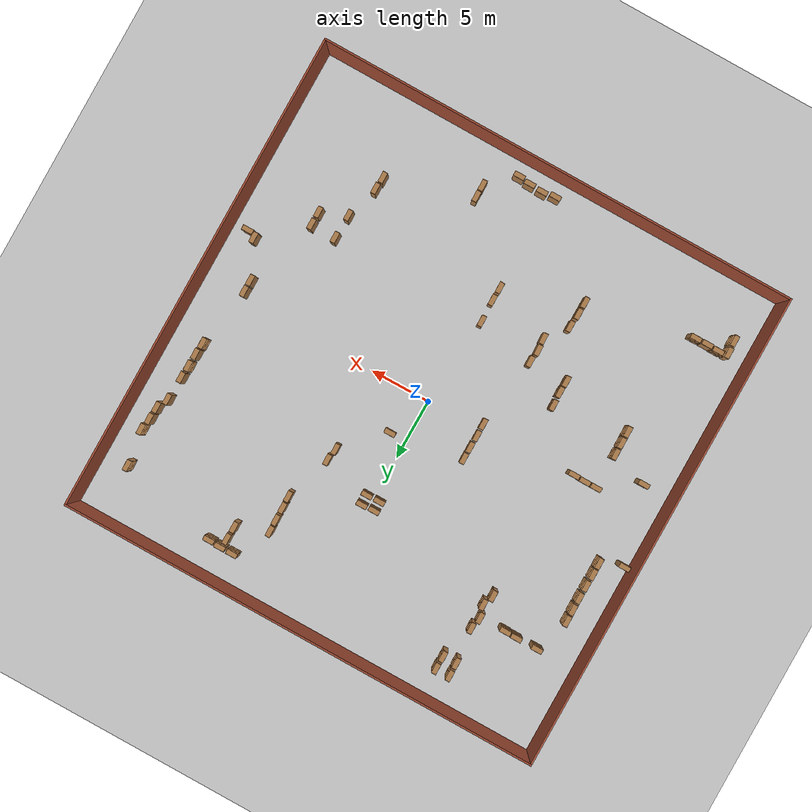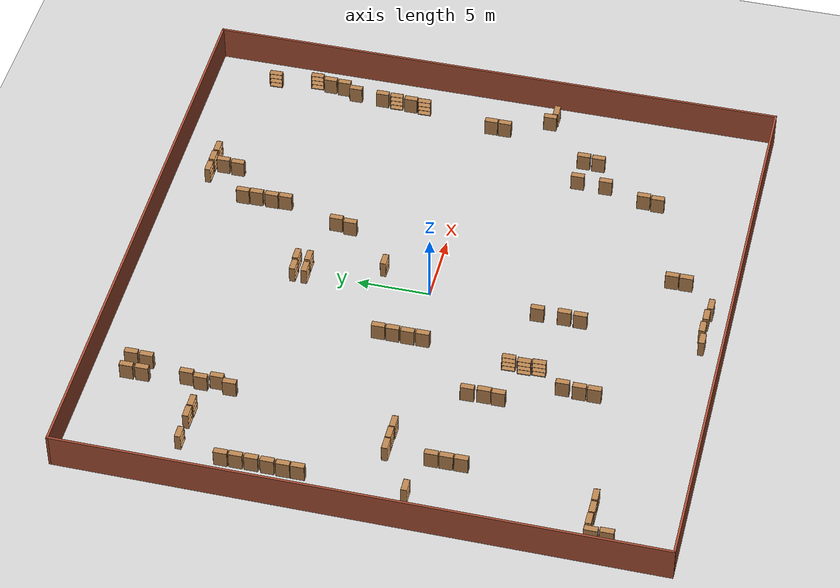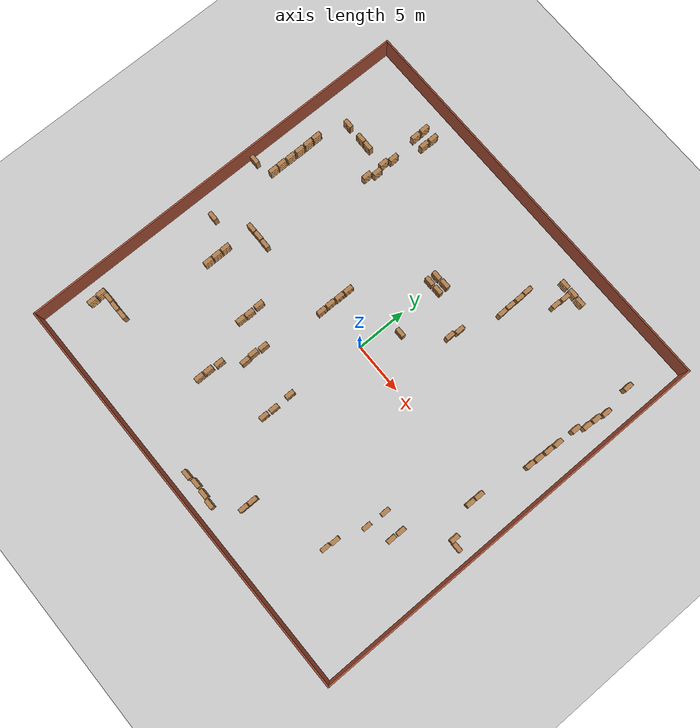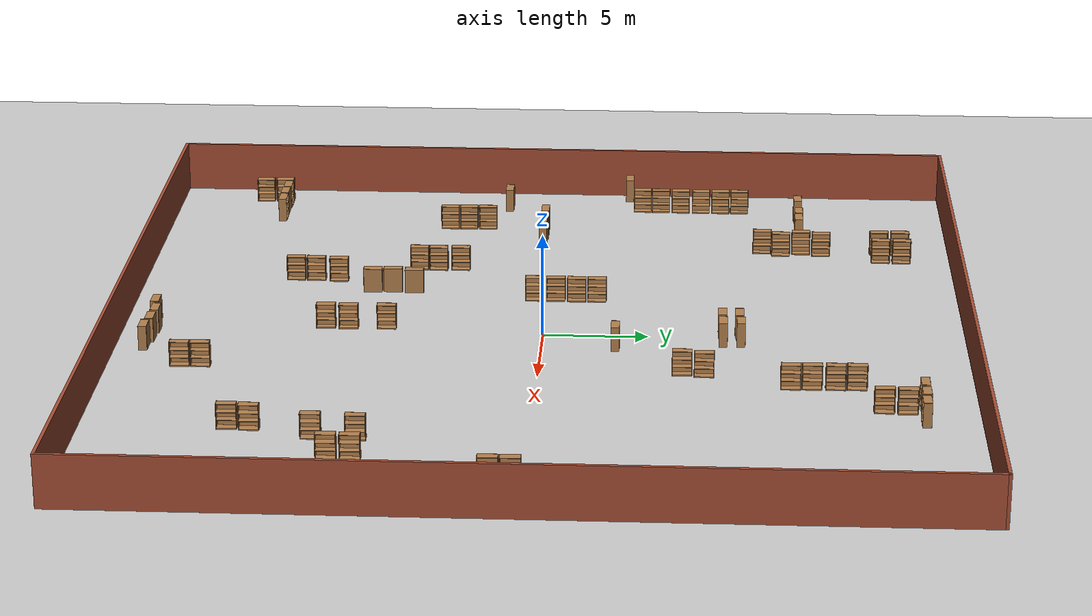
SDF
<sdf version="1.6">
 <world name="default">
  <light name="sun" type="directional">
   <pose>0 0 10 0 -0 0</pose>
   <diffuse>0.8 0.8 0.8 1</diffuse>
   <specular>0.2 0.2 0.2 1</specular>
   <attenuation>
    <range>1000</range>
    <constant>0.9</constant>
    <linear>0.01</linear>
    <quadratic>0.001</quadratic>
   </attenuation>
   <direction>-0.5 0.1 -0.9</direction>
  </light>
  <model name="ground_plane">
   <static>1</static>
   <link name="link">
    <collision name="collision">
     <geometry><plane><normal>0 0 1</normal><size>100 100</size></plane></geometry>
     <surface>
      <contact><collide_bitmask>65535</collide_bitmask></contact>
      <friction><ode><mu>100</mu><mu2>50</mu2></ode></friction>
     </surface>
    </collision>
    <visual name="visual">
     <cast_shadows>0</cast_shadows>
     <geometry><plane><normal>0 0 1</normal><size>100 100</size></plane></geometry>
     <material>
      <script><uri>file://media/materials/scripts/gazebo.material</uri><name>Gazebo/Grey</name></script>
     </material>
    </visual>
   </link>
  </model>
  <gravity>0 0 -9.8</gravity>
  <magnetic_field>6e-06 2.3e-05 -4.2e-05</magnetic_field>
  <atmosphere type="adiabatic"/>
  <physics name="default_physics" default="0" type="ode">
   <max_step_size>0.001</max_step_size>
   <real_time_factor>1</real_time_factor>
   <real_time_update_rate>1000</real_time_update_rate>
  </physics>
  <scene><ambient>0.4 0.4 0.4 1</ambient><background>0.7 0.7 0.7 1</background><shadows>1</shadows></scene>
  <spherical_coordinates>
   <surface_model>EARTH_WGS84</surface_model>
   <latitude_deg>0</latitude_deg>
   <longitude_deg>0</longitude_deg>
   <elevation>0</elevation>
   <heading_deg>0</heading_deg>
  </spherical_coordinates>
  <model name="30x30env"><static>1</static><pose>32.1206 3.39752 0 0 -0 0</pose></model>
  <audio><device>default</device></audio>
  <model name="bookshelf_clone">
   <static>1</static>
   <link name="link">
    <inertial><mass>1</mass></inertial>
    <collision name="back">
     <pose>0 0.005 0.6 0 -0 0</pose>
     <geometry><box><size>0.9 0.01 1.2</size></box></geometry>
    </collision>
    <visual name="visual1">
     <pose>0 0.005 0.6 0 -0 0</pose>
     <geometry><box><size>0.9 0.01 1.2</size></box></geometry>
     <material>
      <script><uri>file://media/materials/scripts/gazebo.material</uri><name>Gazebo/Wood</name></script>
     </material>
    </visual>
    <collision name="left_side">
     <pose>0.45 -0.195 0.6 0 -0 0</pose>
     <geometry><box><size>0.02 0.4 1.2</size></box></geometry>
    </collision>
    <visual name="visual2">
     <pose>0.45 -0.195 0.6 0 -0 0</pose>
     <geometry><box><size>0.02 0.4 1.2</size></box></geometry>
     <material>
      <script><uri>file://media/materials/scripts/gazebo.material</uri><name>Gazebo/Wood</name></script>
     </material>
    </visual>
    <collision name="right_side">
     <pose>-0.45 -0.195 0.6 0 -0 0</pose>
     <geometry><box><size>0.02 0.4 1.2</size></box></geometry>
    </collision>
    <visual name="visual3">
     <pose>-0.45 -0.195 0.6 0 -0 0</pose>
     <geometry><box><size>0.02 0.4 1.2</size></box></geometry>
     <material>
      <script><uri>file://media/materials/scripts/gazebo.material</uri><name>Gazebo/Wood</name></script>
     </material>
    </visual>
    <collision name="bottom">
     <pose>0 -0.195 0.03 0 -0 0</pose>
     <geometry><box><size>0.88 0.4 0.06</size></box></geometry>
    </collision>
    <visual name="visual4">
     <pose>0 -0.195 0.03 0 -0 0</pose>
     <geometry><box><size>0.88 0.4 0.06</size></box></geometry>
     <material>
      <script><uri>file://media/materials/scripts/gazebo.material</uri><name>Gazebo/Wood</name></script>
     </material>
    </visual>
    <collision name="top">
     <pose>0 -0.195 1.19 0 -0 0</pose>
     <geometry><box><size>0.88 0.4 0.02</size></box></geometry>
    </collision>
    <visual name="visual5">
     <pose>0 -0.195 1.19 0 -0 0</pose>
     <geometry><box><size>0.88 0.4 0.02</size></box></geometry>
     <material>
      <script><uri>file://media/materials/scripts/gazebo.material</uri><name>Gazebo/Wood</name></script>
     </material>
    </visual>
    <collision name="low_shelf">
     <pose>0 -0.195 0.43 0 -0 0</pose>
     <geometry><box><size>0.88 0.4 0.02</size></box></geometry>
    </collision>
    <visual name="visual6">
     <pose>0 -0.195 0.43 0 -0 0</pose>
     <geometry><box><size>0.88 0.4 0.02</size></box></geometry>
     <material>
      <script><uri>file://media/materials/scripts/gazebo.material</uri><name>Gazebo/Wood</name></script>
     </material>
    </visual>
    <collision name="high_shelf">
     <pose>0 -0.195 0.8 0 -0 0</pose>
     <geometry><box><size>0.88 0.4 0.02</size></box></geometry>
    </collision>
    <visual name="visual7">
     <pose>0 -0.195 0.8 0 -0 0</pose>
     <geometry><box><size>0.88 0.4 0.02</size></box></geometry>
     <material>
      <script><uri>file://media/materials/scripts/gazebo.material</uri><name>Gazebo/Wood</name></script>
     </material>
    </visual>
   </link>
   <pose>-17.5274 -2.373 0 0 -0 0</pose>
  </model>
  <model name="bookshelf_clone_clone">
   <static>1</static>
   <link name="link">
    <inertial><mass>1</mass></inertial>
    <collision name="back">
     <pose>0 0.005 0.6 0 -0 0</pose>
     <geometry><box><size>0.9 0.01 1.2</size></box></geometry>
    </collision>
    <visual name="visual1">
     <pose>0 0.005 0.6 0 -0 0</pose>
     <geometry><box><size>0.9 0.01 1.2</size></box></geometry>
     <material>
      <script><uri>file://media/materials/scripts/gazebo.material</uri><name>Gazebo/Wood</name></script>
     </material>
    </visual>
    <collision name="left_side">
     <pose>0.45 -0.195 0.6 0 -0 0</pose>
     <geometry><box><size>0.02 0.4 1.2</size></box></geometry>
    </collision>
    <visual name="visual2">
     <pose>0.45 -0.195 0.6 0 -0 0</pose>
     <geometry><box><size>0.02 0.4 1.2</size></box></geometry>
     <material>
      <script><uri>file://media/materials/scripts/gazebo.material</uri><name>Gazebo/Wood</name></script>
     </material>
    </visual>
    <collision name="right_side">
     <pose>-0.45 -0.195 0.6 0 -0 0</pose>
     <geometry><box><size>0.02 0.4 1.2</size></box></geometry>
    </collision>
    <visual name="visual3">
     <pose>-0.45 -0.195 0.6 0 -0 0</pose>
     <geometry><box><size>0.02 0.4 1.2</size></box></geometry>
     <material>
      <script><uri>file://media/materials/scripts/gazebo.material</uri><name>Gazebo/Wood</name></script>
     </material>
    </visual>
    <collision name="bottom">
     <pose>0 -0.195 0.03 0 -0 0</pose>
     <geometry><box><size>0.88 0.4 0.06</size></box></geometry>
    </collision>
    <visual name="visual4">
     <pose>0 -0.195 0.03 0 -0 0</pose>
     <geometry><box><size>0.88 0.4 0.06</size></box></geometry>
     <material>
      <script><uri>file://media/materials/scripts/gazebo.material</uri><name>Gazebo/Wood</name></script>
     </material>
    </visual>
    <collision name="top">
     <pose>0 -0.195 1.19 0 -0 0</pose>
     <geometry><box><size>0.88 0.4 0.02</size></box></geometry>
    </collision>
    <visual name="visual5">
     <pose>0 -0.195 1.19 0 -0 0</pose>
     <geometry><box><size>0.88 0.4 0.02</size></box></geometry>
     <material>
      <script><uri>file://media/materials/scripts/gazebo.material</uri><name>Gazebo/Wood</name></script>
     </material>
    </visual>
    <collision name="low_shelf">
     <pose>0 -0.195 0.43 0 -0 0</pose>
     <geometry><box><size>0.88 0.4 0.02</size></box></geometry>
    </collision>
    <visual name="visual6">
     <pose>0 -0.195 0.43 0 -0 0</pose>
     <geometry><box><size>0.88 0.4 0.02</size></box></geometry>
     <material>
      <script><uri>file://media/materials/scripts/gazebo.material</uri><name>Gazebo/Wood</name></script>
     </material>
    </visual>
    <collision name="high_shelf">
     <pose>0 -0.195 0.8 0 -0 0</pose>
     <geometry><box><size>0.88 0.4 0.02</size></box></geometry>
    </collision>
    <visual name="visual7">
     <pose>0 -0.195 0.8 0 -0 0</pose>
     <geometry><box><size>0.88 0.4 0.02</size></box></geometry>
     <material>
      <script><uri>file://media/materials/scripts/gazebo.material</uri><name>Gazebo/Wood</name></script>
     </material>
    </visual>
   </link>
   <pose>-16.536 12.6596 0 0 -0 0</pose>
  </model>
  <model name="bookshelf_clone_clone_1">
   <static>1</static>
   <link name="link">
    <inertial><mass>1</mass></inertial>
    <collision name="back">
     <pose>0 0.005 0.6 0 -0 0</pose>
     <geometry><box><size>0.9 0.01 1.2</size></box></geometry>
    </collision>
    <visual name="visual1">
     <pose>0 0.005 0.6 0 -0 0</pose>
     <geometry><box><size>0.9 0.01 1.2</size></box></geometry>
     <material>
      <script><uri>file://media/materials/scripts/gazebo.material</uri><name>Gazebo/Wood</name></script>
     </material>
    </visual>
    <collision name="left_side">
     <pose>0.45 -0.195 0.6 0 -0 0</pose>
     <geometry><box><size>0.02 0.4 1.2</size></box></geometry>
    </collision>
    <visual name="visual2">
     <pose>0.45 -0.195 0.6 0 -0 0</pose>
     <geometry><box><size>0.02 0.4 1.2</size></box></geometry>
     <material>
      <script><uri>file://media/materials/scripts/gazebo.material</uri><name>Gazebo/Wood</name></script>
     </material>
    </visual>
    <collision name="right_side">
     <pose>-0.45 -0.195 0.6 0 -0 0</pose>
     <geometry><box><size>0.02 0.4 1.2</size></box></geometry>
    </collision>
    <visual name="visual3">
     <pose>-0.45 -0.195 0.6 0 -0 0</pose>
     <geometry><box><size>0.02 0.4 1.2</size></box></geometry>
     <material>
      <script><uri>file://media/materials/scripts/gazebo.material</uri><name>Gazebo/Wood</name></script>
     </material>
    </visual>
    <collision name="bottom">
     <pose>0 -0.195 0.03 0 -0 0</pose>
     <geometry><box><size>0.88 0.4 0.06</size></box></geometry>
    </collision>
    <visual name="visual4">
     <pose>0 -0.195 0.03 0 -0 0</pose>
     <geometry><box><size>0.88 0.4 0.06</size></box></geometry>
     <material>
      <script><uri>file://media/materials/scripts/gazebo.material</uri><name>Gazebo/Wood</name></script>
     </material>
    </visual>
    <collision name="top">
     <pose>0 -0.195 1.19 0 -0 0</pose>
     <geometry><box><size>0.88 0.4 0.02</size></box></geometry>
    </collision>
    <visual name="visual5">
     <pose>0 -0.195 1.19 0 -0 0</pose>
     <geometry><box><size>0.88 0.4 0.02</size></box></geometry>
     <material>
      <script><uri>file://media/materials/scripts/gazebo.material</uri><name>Gazebo/Wood</name></script>
     </material>
    </visual>
    <collision name="low_shelf">
     <pose>0 -0.195 0.43 0 -0 0</pose>
     <geometry><box><size>0.88 0.4 0.02</size></box></geometry>
    </collision>
    <visual name="visual6">
     <pose>0 -0.195 0.43 0 -0 0</pose>
     <geometry><box><size>0.88 0.4 0.02</size></box></geometry>
     <material>
      <script><uri>file://media/materials/scripts/gazebo.material</uri><name>Gazebo/Wood</name></script>
     </material>
    </visual>
    <collision name="high_shelf">
     <pose>0 -0.195 0.8 0 -0 0</pose>
     <geometry><box><size>0.88 0.4 0.02</size></box></geometry>
    </collision>
    <visual name="visual7">
     <pose>0 -0.195 0.8 0 -0 0</pose>
     <geometry><box><size>0.88 0.4 0.02</size></box></geometry>
     <material>
      <script><uri>file://media/materials/scripts/gazebo.material</uri><name>Gazebo/Wood</name></script>
     </material>
    </visual>
   </link>
   <pose>-14.7265 12.6733 0 0 -0 0</pose>
  </model>
  <model name="bookshelf_clone_clone_2">
   <static>1</static>
   <link name="link">
    <inertial><mass>1</mass></inertial>
    <collision name="back">
     <pose>0 0.005 0.6 0 -0 0</pose>
     <geometry><box><size>0.9 0.01 1.2</size></box></geometry>
    </collision>
    <visual name="visual1">
     <pose>0 0.005 0.6 0 -0 0</pose>
     <geometry><box><size>0.9 0.01 1.2</size></box></geometry>
     <material>
      <script><uri>file://media/materials/scripts/gazebo.material</uri><name>Gazebo/Wood</name></script>
     </material>
    </visual>
    <collision name="left_side">
     <pose>0.45 -0.195 0.6 0 -0 0</pose>
     <geometry><box><size>0.02 0.4 1.2</size></box></geometry>
    </collision>
    <visual name="visual2">
     <pose>0.45 -0.195 0.6 0 -0 0</pose>
     <geometry><box><size>0.02 0.4 1.2</size></box></geometry>
     <material>
      <script><uri>file://media/materials/scripts/gazebo.material</uri><name>Gazebo/Wood</name></script>
     </material>
    </visual>
    <collision name="right_side">
     <pose>-0.45 -0.195 0.6 0 -0 0</pose>
     <geometry><box><size>0.02 0.4 1.2</size></box></geometry>
    </collision>
    <visual name="visual3">
     <pose>-0.45 -0.195 0.6 0 -0 0</pose>
     <geometry><box><size>0.02 0.4 1.2</size></box></geometry>
     <material>
      <script><uri>file://media/materials/scripts/gazebo.material</uri><name>Gazebo/Wood</name></script>
     </material>
    </visual>
    <collision name="bottom">
     <pose>0 -0.195 0.03 0 -0 0</pose>
     <geometry><box><size>0.88 0.4 0.06</size></box></geometry>
    </collision>
    <visual name="visual4">
     <pose>0 -0.195 0.03 0 -0 0</pose>
     <geometry><box><size>0.88 0.4 0.06</size></box></geometry>
     <material>
      <script><uri>file://media/materials/scripts/gazebo.material</uri><name>Gazebo/Wood</name></script>
     </material>
    </visual>
    <collision name="top">
     <pose>0 -0.195 1.19 0 -0 0</pose>
     <geometry><box><size>0.88 0.4 0.02</size></box></geometry>
    </collision>
    <visual name="visual5">
     <pose>0 -0.195 1.19 0 -0 0</pose>
     <geometry><box><size>0.88 0.4 0.02</size></box></geometry>
     <material>
      <script><uri>file://media/materials/scripts/gazebo.material</uri><name>Gazebo/Wood</name></script>
     </material>
    </visual>
    <collision name="low_shelf">
     <pose>0 -0.195 0.43 0 -0 0</pose>
     <geometry><box><size>0.88 0.4 0.02</size></box></geometry>
    </collision>
    <visual name="visual6">
     <pose>0 -0.195 0.43 0 -0 0</pose>
     <geometry><box><size>0.88 0.4 0.02</size></box></geometry>
     <material>
      <script><uri>file://media/materials/scripts/gazebo.material</uri><name>Gazebo/Wood</name></script>
     </material>
    </visual>
    <collision name="high_shelf">
     <pose>0 -0.195 0.8 0 -0 0</pose>
     <geometry><box><size>0.88 0.4 0.02</size></box></geometry>
    </collision>
    <visual name="visual7">
     <pose>0 -0.195 0.8 0 -0 0</pose>
     <geometry><box><size>0.88 0.4 0.02</size></box></geometry>
     <material>
      <script><uri>file://media/materials/scripts/gazebo.material</uri><name>Gazebo/Wood</name></script>
     </material>
    </visual>
   </link>
   <pose>-13.7508 12.6465 0 0 -0 0</pose>
  </model>
  <model name="bookshelf_clone_clone_0_clone_clone">
   <static>1</static>
   <link name="link">
    <inertial><mass>1</mass></inertial>
    <collision name="back">
     <pose>0 0.005 0.6 0 -0 0</pose>
     <geometry><box><size>0.9 0.01 1.2</size></box></geometry>
    </collision>
    <visual name="visual1">
     <pose>0 0.005 0.6 0 -0 0</pose>
     <geometry><box><size>0.9 0.01 1.2</size></box></geometry>
     <material>
      <script><uri>file://media/materials/scripts/gazebo.material</uri><name>Gazebo/Wood</name></script>
     </material>
    </visual>
    <collision name="left_side">
     <pose>0.45 -0.195 0.6 0 -0 0</pose>
     <geometry><box><size>0.02 0.4 1.2</size></box></geometry>
    </collision>
    <visual name="visual2">
     <pose>0.45 -0.195 0.6 0 -0 0</pose>
     <geometry><box><size>0.02 0.4 1.2</size></box></geometry>
     <material>
      <script><uri>file://media/materials/scripts/gazebo.material</uri><name>Gazebo/Wood</name></script>
     </material>
    </visual>
    <collision name="right_side">
     <pose>-0.45 -0.195 0.6 0 -0 0</pose>
     <geometry><box><size>0.02 0.4 1.2</size></box></geometry>
    </collision>
    <visual name="visual3">
     <pose>-0.45 -0.195 0.6 0 -0 0</pose>
     <geometry><box><size>0.02 0.4 1.2</size></box></geometry>
     <material>
      <script><uri>file://media/materials/scripts/gazebo.material</uri><name>Gazebo/Wood</name></script>
     </material>
    </visual>
    <collision name="bottom">
     <pose>0 -0.195 0.03 0 -0 0</pose>
     <geometry><box><size>0.88 0.4 0.06</size></box></geometry>
    </collision>
    <visual name="visual4">
     <pose>0 -0.195 0.03 0 -0 0</pose>
     <geometry><box><size>0.88 0.4 0.06</size></box></geometry>
     <material>
      <script><uri>file://media/materials/scripts/gazebo.material</uri><name>Gazebo/Wood</name></script>
     </material>
    </visual>
    <collision name="top">
     <pose>0 -0.195 1.19 0 -0 0</pose>
     <geometry><box><size>0.88 0.4 0.02</size></box></geometry>
    </collision>
    <visual name="visual5">
     <pose>0 -0.195 1.19 0 -0 0</pose>
     <geometry><box><size>0.88 0.4 0.02</size></box></geometry>
     <material>
      <script><uri>file://media/materials/scripts/gazebo.material</uri><name>Gazebo/Wood</name></script>
     </material>
    </visual>
    <collision name="low_shelf">
     <pose>0 -0.195 0.43 0 -0 0</pose>
     <geometry><box><size>0.88 0.4 0.02</size></box></geometry>
    </collision>
    <visual name="visual6">
     <pose>0 -0.195 0.43 0 -0 0</pose>
     <geometry><box><size>0.88 0.4 0.02</size></box></geometry>
     <material>
      <script><uri>file://media/materials/scripts/gazebo.material</uri><name>Gazebo/Wood</name></script>
     </material>
    </visual>
    <collision name="high_shelf">
     <pose>0 -0.195 0.8 0 -0 0</pose>
     <geometry><box><size>0.88 0.4 0.02</size></box></geometry>
    </collision>
    <visual name="visual7">
     <pose>0 -0.195 0.8 0 -0 0</pose>
     <geometry><box><size>0.88 0.4 0.02</size></box></geometry>
     <material>
      <script><uri>file://media/materials/scripts/gazebo.material</uri><name>Gazebo/Wood</name></script>
     </material>
    </visual>
   </link>
   <pose>-17.7016 5.36171 0 0 -0 1.58018</pose>
  </model>
  <model name="bookshelf_clone_clone_0_clone_clone_0">
   <static>1</static>
   <link name="link">
    <inertial><mass>1</mass></inertial>
    <collision name="back">
     <pose>0 0.005 0.6 0 -0 0</pose>
     <geometry><box><size>0.9 0.01 1.2</size></box></geometry>
    </collision>
    <visual name="visual1">
     <pose>0 0.005 0.6 0 -0 0</pose>
     <geometry><box><size>0.9 0.01 1.2</size></box></geometry>
     <material>
      <script><uri>file://media/materials/scripts/gazebo.material</uri><name>Gazebo/Wood</name></script>
     </material>
    </visual>
    <collision name="left_side">
     <pose>0.45 -0.195 0.6 0 -0 0</pose>
     <geometry><box><size>0.02 0.4 1.2</size></box></geometry>
    </collision>
    <visual name="visual2">
     <pose>0.45 -0.195 0.6 0 -0 0</pose>
     <geometry><box><size>0.02 0.4 1.2</size></box></geometry>
     <material>
      <script><uri>file://media/materials/scripts/gazebo.material</uri><name>Gazebo/Wood</name></script>
     </material>
    </visual>
    <collision name="right_side">
     <pose>-0.45 -0.195 0.6 0 -0 0</pose>
     <geometry><box><size>0.02 0.4 1.2</size></box></geometry>
    </collision>
    <visual name="visual3">
     <pose>-0.45 -0.195 0.6 0 -0 0</pose>
     <geometry><box><size>0.02 0.4 1.2</size></box></geometry>
     <material>
      <script><uri>file://media/materials/scripts/gazebo.material</uri><name>Gazebo/Wood</name></script>
     </material>
    </visual>
    <collision name="bottom">
     <pose>0 -0.195 0.03 0 -0 0</pose>
     <geometry><box><size>0.88 0.4 0.06</size></box></geometry>
    </collision>
    <visual name="visual4">
     <pose>0 -0.195 0.03 0 -0 0</pose>
     <geometry><box><size>0.88 0.4 0.06</size></box></geometry>
     <material>
      <script><uri>file://media/materials/scripts/gazebo.material</uri><name>Gazebo/Wood</name></script>
     </material>
    </visual>
    <collision name="top">
     <pose>0 -0.195 1.19 0 -0 0</pose>
     <geometry><box><size>0.88 0.4 0.02</size></box></geometry>
    </collision>
    <visual name="visual5">
     <pose>0 -0.195 1.19 0 -0 0</pose>
     <geometry><box><size>0.88 0.4 0.02</size></box></geometry>
     <material>
      <script><uri>file://media/materials/scripts/gazebo.material</uri><name>Gazebo/Wood</name></script>
     </material>
    </visual>
    <collision name="low_shelf">
     <pose>0 -0.195 0.43 0 -0 0</pose>
     <geometry><box><size>0.88 0.4 0.02</size></box></geometry>
    </collision>
    <visual name="visual6">
     <pose>0 -0.195 0.43 0 -0 0</pose>
     <geometry><box><size>0.88 0.4 0.02</size></box></geometry>
     <material>
      <script><uri>file://media/materials/scripts/gazebo.material</uri><name>Gazebo/Wood</name></script>
     </material>
    </visual>
    <collision name="high_shelf">
     <pose>0 -0.195 0.8 0 -0 0</pose>
     <geometry><box><size>0.88 0.4 0.02</size></box></geometry>
    </collision>
    <visual name="visual7">
     <pose>0 -0.195 0.8 0 -0 0</pose>
     <geometry><box><size>0.88 0.4 0.02</size></box></geometry>
     <material>
      <script><uri>file://media/materials/scripts/gazebo.material</uri><name>Gazebo/Wood</name></script>
     </material>
    </visual>
   </link>
   <pose>-17.6926 4.40593 0 0 -0 1.58018</pose>
  </model>
  <model name="bookshelf_clone_clone_0_clone_clone_1">
   <static>1</static>
   <link name="link">
    <inertial><mass>1</mass></inertial>
    <collision name="back">
     <pose>0 0.005 0.6 0 -0 0</pose>
     <geometry><box><size>0.9 0.01 1.2</size></box></geometry>
    </collision>
    <visual name="visual1">
     <pose>0 0.005 0.6 0 -0 0</pose>
     <geometry><box><size>0.9 0.01 1.2</size></box></geometry>
     <material>
      <script><uri>file://media/materials/scripts/gazebo.material</uri><name>Gazebo/Wood</name></script>
     </material>
    </visual>
    <collision name="left_side">
     <pose>0.45 -0.195 0.6 0 -0 0</pose>
     <geometry><box><size>0.02 0.4 1.2</size></box></geometry>
    </collision>
    <visual name="visual2">
     <pose>0.45 -0.195 0.6 0 -0 0</pose>
     <geometry><box><size>0.02 0.4 1.2</size></box></geometry>
     <material>
      <script><uri>file://media/materials/scripts/gazebo.material</uri><name>Gazebo/Wood</name></script>
     </material>
    </visual>
    <collision name="right_side">
     <pose>-0.45 -0.195 0.6 0 -0 0</pose>
     <geometry><box><size>0.02 0.4 1.2</size></box></geometry>
    </collision>
    <visual name="visual3">
     <pose>-0.45 -0.195 0.6 0 -0 0</pose>
     <geometry><box><size>0.02 0.4 1.2</size></box></geometry>
     <material>
      <script><uri>file://media/materials/scripts/gazebo.material</uri><name>Gazebo/Wood</name></script>
     </material>
    </visual>
    <collision name="bottom">
     <pose>0 -0.195 0.03 0 -0 0</pose>
     <geometry><box><size>0.88 0.4 0.06</size></box></geometry>
    </collision>
    <visual name="visual4">
     <pose>0 -0.195 0.03 0 -0 0</pose>
     <geometry><box><size>0.88 0.4 0.06</size></box></geometry>
     <material>
      <script><uri>file://media/materials/scripts/gazebo.material</uri><name>Gazebo/Wood</name></script>
     </material>
    </visual>
    <collision name="top">
     <pose>0 -0.195 1.19 0 -0 0</pose>
     <geometry><box><size>0.88 0.4 0.02</size></box></geometry>
    </collision>
    <visual name="visual5">
     <pose>0 -0.195 1.19 0 -0 0</pose>
     <geometry><box><size>0.88 0.4 0.02</size></box></geometry>
     <material>
      <script><uri>file://media/materials/scripts/gazebo.material</uri><name>Gazebo/Wood</name></script>
     </material>
    </visual>
    <collision name="low_shelf">
     <pose>0 -0.195 0.43 0 -0 0</pose>
     <geometry><box><size>0.88 0.4 0.02</size></box></geometry>
    </collision>
    <visual name="visual6">
     <pose>0 -0.195 0.43 0 -0 0</pose>
     <geometry><box><size>0.88 0.4 0.02</size></box></geometry>
     <material>
      <script><uri>file://media/materials/scripts/gazebo.material</uri><name>Gazebo/Wood</name></script>
     </material>
    </visual>
    <collision name="high_shelf">
     <pose>0 -0.195 0.8 0 -0 0</pose>
     <geometry><box><size>0.88 0.4 0.02</size></box></geometry>
    </collision>
    <visual name="visual7">
     <pose>0 -0.195 0.8 0 -0 0</pose>
     <geometry><box><size>0.88 0.4 0.02</size></box></geometry>
     <material>
      <script><uri>file://media/materials/scripts/gazebo.material</uri><name>Gazebo/Wood</name></script>
     </material>
    </visual>
   </link>
   <pose>-17.6741 6.39169 0 0 -0 1.58018</pose>
  </model>
  <model name="bookshelf_clone_clone_0_clone_clone_2">
   <static>1</static>
   <link name="link">
    <inertial><mass>1</mass></inertial>
    <collision name="back">
     <pose>0 0.005 0.6 0 -0 0</pose>
     <geometry><box><size>0.9 0.01 1.2</size></box></geometry>
    </collision>
    <visual name="visual1">
     <pose>0 0.005 0.6 0 -0 0</pose>
     <geometry><box><size>0.9 0.01 1.2</size></box></geometry>
     <material>
      <script><uri>file://media/materials/scripts/gazebo.material</uri><name>Gazebo/Wood</name></script>
     </material>
    </visual>
    <collision name="left_side">
     <pose>0.45 -0.195 0.6 0 -0 0</pose>
     <geometry><box><size>0.02 0.4 1.2</size></box></geometry>
    </collision>
    <visual name="visual2">
     <pose>0.45 -0.195 0.6 0 -0 0</pose>
     <geometry><box><size>0.02 0.4 1.2</size></box></geometry>
     <material>
      <script><uri>file://media/materials/scripts/gazebo.material</uri><name>Gazebo/Wood</name></script>
     </material>
    </visual>
    <collision name="right_side">
     <pose>-0.45 -0.195 0.6 0 -0 0</pose>
     <geometry><box><size>0.02 0.4 1.2</size></box></geometry>
    </collision>
    <visual name="visual3">
     <pose>-0.45 -0.195 0.6 0 -0 0</pose>
     <geometry><box><size>0.02 0.4 1.2</size></box></geometry>
     <material>
      <script><uri>file://media/materials/scripts/gazebo.material</uri><name>Gazebo/Wood</name></script>
     </material>
    </visual>
    <collision name="bottom">
     <pose>0 -0.195 0.03 0 -0 0</pose>
     <geometry><box><size>0.88 0.4 0.06</size></box></geometry>
    </collision>
    <visual name="visual4">
     <pose>0 -0.195 0.03 0 -0 0</pose>
     <geometry><box><size>0.88 0.4 0.06</size></box></geometry>
     <material>
      <script><uri>file://media/materials/scripts/gazebo.material</uri><name>Gazebo/Wood</name></script>
     </material>
    </visual>
    <collision name="top">
     <pose>0 -0.195 1.19 0 -0 0</pose>
     <geometry><box><size>0.88 0.4 0.02</size></box></geometry>
    </collision>
    <visual name="visual5">
     <pose>0 -0.195 1.19 0 -0 0</pose>
     <geometry><box><size>0.88 0.4 0.02</size></box></geometry>
     <material>
      <script><uri>file://media/materials/scripts/gazebo.material</uri><name>Gazebo/Wood</name></script>
     </material>
    </visual>
    <collision name="low_shelf">
     <pose>0 -0.195 0.43 0 -0 0</pose>
     <geometry><box><size>0.88 0.4 0.02</size></box></geometry>
    </collision>
    <visual name="visual6">
     <pose>0 -0.195 0.43 0 -0 0</pose>
     <geometry><box><size>0.88 0.4 0.02</size></box></geometry>
     <material>
      <script><uri>file://media/materials/scripts/gazebo.material</uri><name>Gazebo/Wood</name></script>
     </material>
    </visual>
    <collision name="high_shelf">
     <pose>0 -0.195 0.8 0 -0 0</pose>
     <geometry><box><size>0.88 0.4 0.02</size></box></geometry>
    </collision>
    <visual name="visual7">
     <pose>0 -0.195 0.8 0 -0 0</pose>
     <geometry><box><size>0.88 0.4 0.02</size></box></geometry>
     <material>
      <script><uri>file://media/materials/scripts/gazebo.material</uri><name>Gazebo/Wood</name></script>
     </material>
    </visual>
   </link>
   <pose>-17.6649 7.44946 0 0 -0 1.58018</pose>
  </model>
  <model name="bookshelf_clone_clone_0_clone_clone_3">
   <static>1</static>
   <link name="link">
    <inertial><mass>1</mass></inertial>
    <collision name="back">
     <pose>0 0.005 0.6 0 -0 0</pose>
     <geometry><box><size>0.9 0.01 1.2</size></box></geometry>
    </collision>
    <visual name="visual1">
     <pose>0 0.005 0.6 0 -0 0</pose>
     <geometry><box><size>0.9 0.01 1.2</size></box></geometry>
     <material>
      <script><uri>file://media/materials/scripts/gazebo.material</uri><name>Gazebo/Wood</name></script>
     </material>
    </visual>
    <collision name="left_side">
     <pose>0.45 -0.195 0.6 0 -0 0</pose>
     <geometry><box><size>0.02 0.4 1.2</size></box></geometry>
    </collision>
    <visual name="visual2">
     <pose>0.45 -0.195 0.6 0 -0 0</pose>
     <geometry><box><size>0.02 0.4 1.2</size></box></geometry>
     <material>
      <script><uri>file://media/materials/scripts/gazebo.material</uri><name>Gazebo/Wood</name></script>
     </material>
    </visual>
    <collision name="right_side">
     <pose>-0.45 -0.195 0.6 0 -0 0</pose>
     <geometry><box><size>0.02 0.4 1.2</size></box></geometry>
    </collision>
    <visual name="visual3">
     <pose>-0.45 -0.195 0.6 0 -0 0</pose>
     <geometry><box><size>0.02 0.4 1.2</size></box></geometry>
     <material>
      <script><uri>file://media/materials/scripts/gazebo.material</uri><name>Gazebo/Wood</name></script>
     </material>
    </visual>
    <collision name="bottom">
     <pose>0 -0.195 0.03 0 -0 0</pose>
     <geometry><box><size>0.88 0.4 0.06</size></box></geometry>
    </collision>
    <visual name="visual4">
     <pose>0 -0.195 0.03 0 -0 0</pose>
     <geometry><box><size>0.88 0.4 0.06</size></box></geometry>
     <material>
      <script><uri>file://media/materials/scripts/gazebo.material</uri><name>Gazebo/Wood</name></script>
     </material>
    </visual>
    <collision name="top">
     <pose>0 -0.195 1.19 0 -0 0</pose>
     <geometry><box><size>0.88 0.4 0.02</size></box></geometry>
    </collision>
    <visual name="visual5">
     <pose>0 -0.195 1.19 0 -0 0</pose>
     <geometry><box><size>0.88 0.4 0.02</size></box></geometry>
     <material>
      <script><uri>file://media/materials/scripts/gazebo.material</uri><name>Gazebo/Wood</name></script>
     </material>
    </visual>
    <collision name="low_shelf">
     <pose>0 -0.195 0.43 0 -0 0</pose>
     <geometry><box><size>0.88 0.4 0.02</size></box></geometry>
    </collision>
    <visual name="visual6">
     <pose>0 -0.195 0.43 0 -0 0</pose>
     <geometry><box><size>0.88 0.4 0.02</size></box></geometry>
     <material>
      <script><uri>file://media/materials/scripts/gazebo.material</uri><name>Gazebo/Wood</name></script>
     </material>
    </visual>
    <collision name="high_shelf">
     <pose>0 -0.195 0.8 0 -0 0</pose>
     <geometry><box><size>0.88 0.4 0.02</size></box></geometry>
    </collision>
    <visual name="visual7">
     <pose>0 -0.195 0.8 0 -0 0</pose>
     <geometry><box><size>0.88 0.4 0.02</size></box></geometry>
     <material>
      <script><uri>file://media/materials/scripts/gazebo.material</uri><name>Gazebo/Wood</name></script>
     </material>
    </visual>
   </link>
   <pose>-17.6741 8.4702 0 0 -0 1.58018</pose>
  </model>
  <model name="bookshelf_clone_clone_0_clone_clone_4">
   <static>1</static>
   <link name="link">
    <inertial><mass>1</mass></inertial>
    <collision name="back">
     <pose>0 0.005 0.6 0 -0 0</pose>
     <geometry><box><size>0.9 0.01 1.2</size></box></geometry>
    </collision>
    <visual name="visual1">
     <pose>0 0.005 0.6 0 -0 0</pose>
     <geometry><box><size>0.9 0.01 1.2</size></box></geometry>
     <material>
      <script><uri>file://media/materials/scripts/gazebo.material</uri><name>Gazebo/Wood</name></script>
     </material>
    </visual>
    <collision name="left_side">
     <pose>0.45 -0.195 0.6 0 -0 0</pose>
     <geometry><box><size>0.02 0.4 1.2</size></box></geometry>
    </collision>
    <visual name="visual2">
     <pose>0.45 -0.195 0.6 0 -0 0</pose>
     <geometry><box><size>0.02 0.4 1.2</size></box></geometry>
     <material>
      <script><uri>file://media/materials/scripts/gazebo.material</uri><name>Gazebo/Wood</name></script>
     </material>
    </visual>
    <collision name="right_side">
     <pose>-0.45 -0.195 0.6 0 -0 0</pose>
     <geometry><box><size>0.02 0.4 1.2</size></box></geometry>
    </collision>
    <visual name="visual3">
     <pose>-0.45 -0.195 0.6 0 -0 0</pose>
     <geometry><box><size>0.02 0.4 1.2</size></box></geometry>
     <material>
      <script><uri>file://media/materials/scripts/gazebo.material</uri><name>Gazebo/Wood</name></script>
     </material>
    </visual>
    <collision name="bottom">
     <pose>0 -0.195 0.03 0 -0 0</pose>
     <geometry><box><size>0.88 0.4 0.06</size></box></geometry>
    </collision>
    <visual name="visual4">
     <pose>0 -0.195 0.03 0 -0 0</pose>
     <geometry><box><size>0.88 0.4 0.06</size></box></geometry>
     <material>
      <script><uri>file://media/materials/scripts/gazebo.material</uri><name>Gazebo/Wood</name></script>
     </material>
    </visual>
    <collision name="top">
     <pose>0 -0.195 1.19 0 -0 0</pose>
     <geometry><box><size>0.88 0.4 0.02</size></box></geometry>
    </collision>
    <visual name="visual5">
     <pose>0 -0.195 1.19 0 -0 0</pose>
     <geometry><box><size>0.88 0.4 0.02</size></box></geometry>
     <material>
      <script><uri>file://media/materials/scripts/gazebo.material</uri><name>Gazebo/Wood</name></script>
     </material>
    </visual>
    <collision name="low_shelf">
     <pose>0 -0.195 0.43 0 -0 0</pose>
     <geometry><box><size>0.88 0.4 0.02</size></box></geometry>
    </collision>
    <visual name="visual6">
     <pose>0 -0.195 0.43 0 -0 0</pose>
     <geometry><box><size>0.88 0.4 0.02</size></box></geometry>
     <material>
      <script><uri>file://media/materials/scripts/gazebo.material</uri><name>Gazebo/Wood</name></script>
     </material>
    </visual>
    <collision name="high_shelf">
     <pose>0 -0.195 0.8 0 -0 0</pose>
     <geometry><box><size>0.88 0.4 0.02</size></box></geometry>
    </collision>
    <visual name="visual7">
     <pose>0 -0.195 0.8 0 -0 0</pose>
     <geometry><box><size>0.88 0.4 0.02</size></box></geometry>
     <material>
      <script><uri>file://media/materials/scripts/gazebo.material</uri><name>Gazebo/Wood</name></script>
     </material>
    </visual>
   </link>
   <pose>-17.6956 9.45552 0 0 -0 1.58018</pose>
  </model>
  <model name="bookshelf_clone_clone_3">
   <static>1</static>
   <link name="link">
    <inertial><mass>1</mass></inertial>
    <collision name="back">
     <pose>0 0.005 0.6 0 -0 0</pose>
     <geometry><box><size>0.9 0.01 1.2</size></box></geometry>
    </collision>
    <visual name="visual1">
     <pose>0 0.005 0.6 0 -0 0</pose>
     <geometry><box><size>0.9 0.01 1.2</size></box></geometry>
     <material>
      <script><uri>file://media/materials/scripts/gazebo.material</uri><name>Gazebo/Wood</name></script>
     </material>
    </visual>
    <collision name="left_side">
     <pose>0.45 -0.195 0.6 0 -0 0</pose>
     <geometry><box><size>0.02 0.4 1.2</size></box></geometry>
    </collision>
    <visual name="visual2">
     <pose>0.45 -0.195 0.6 0 -0 0</pose>
     <geometry><box><size>0.02 0.4 1.2</size></box></geometry>
     <material>
      <script><uri>file://media/materials/scripts/gazebo.material</uri><name>Gazebo/Wood</name></script>
     </material>
    </visual>
    <collision name="right_side">
     <pose>-0.45 -0.195 0.6 0 -0 0</pose>
     <geometry><box><size>0.02 0.4 1.2</size></box></geometry>
    </collision>
    <visual name="visual3">
     <pose>-0.45 -0.195 0.6 0 -0 0</pose>
     <geometry><box><size>0.02 0.4 1.2</size></box></geometry>
     <material>
      <script><uri>file://media/materials/scripts/gazebo.material</uri><name>Gazebo/Wood</name></script>
     </material>
    </visual>
    <collision name="bottom">
     <pose>0 -0.195 0.03 0 -0 0</pose>
     <geometry><box><size>0.88 0.4 0.06</size></box></geometry>
    </collision>
    <visual name="visual4">
     <pose>0 -0.195 0.03 0 -0 0</pose>
     <geometry><box><size>0.88 0.4 0.06</size></box></geometry>
     <material>
      <script><uri>file://media/materials/scripts/gazebo.material</uri><name>Gazebo/Wood</name></script>
     </material>
    </visual>
    <collision name="top">
     <pose>0 -0.195 1.19 0 -0 0</pose>
     <geometry><box><size>0.88 0.4 0.02</size></box></geometry>
    </collision>
    <visual name="visual5">
     <pose>0 -0.195 1.19 0 -0 0</pose>
     <geometry><box><size>0.88 0.4 0.02</size></box></geometry>
     <material>
      <script><uri>file://media/materials/scripts/gazebo.material</uri><name>Gazebo/Wood</name></script>
     </material>
    </visual>
    <collision name="low_shelf">
     <pose>0 -0.195 0.43 0 -0 0</pose>
     <geometry><box><size>0.88 0.4 0.02</size></box></geometry>
    </collision>
    <visual name="visual6">
     <pose>0 -0.195 0.43 0 -0 0</pose>
     <geometry><box><size>0.88 0.4 0.02</size></box></geometry>
     <material>
      <script><uri>file://media/materials/scripts/gazebo.material</uri><name>Gazebo/Wood</name></script>
     </material>
    </visual>
    <collision name="high_shelf">
     <pose>0 -0.195 0.8 0 -0 0</pose>
     <geometry><box><size>0.88 0.4 0.02</size></box></geometry>
    </collision>
    <visual name="visual7">
     <pose>0 -0.195 0.8 0 -0 0</pose>
     <geometry><box><size>0.88 0.4 0.02</size></box></geometry>
     <material>
      <script><uri>file://media/materials/scripts/gazebo.material</uri><name>Gazebo/Wood</name></script>
     </material>
    </visual>
   </link>
   <pose>-19.329 3.89641 0 0 -0 0</pose>
  </model>
  <model name="bookshelf_clone_clone_0_clone_clone_0_clone">
   <static>1</static>
   <link name="link">
    <inertial><mass>1</mass></inertial>
    <collision name="back">
     <pose>0 0.005 0.6 0 -0 0</pose>
     <geometry><box><size>0.9 0.01 1.2</size></box></geometry>
    </collision>
    <visual name="visual1">
     <pose>0 0.005 0.6 0 -0 0</pose>
     <geometry><box><size>0.9 0.01 1.2</size></box></geometry>
     <material>
      <script><uri>file://media/materials/scripts/gazebo.material</uri><name>Gazebo/Wood</name></script>
     </material>
    </visual>
    <collision name="left_side">
     <pose>0.45 -0.195 0.6 0 -0 0</pose>
     <geometry><box><size>0.02 0.4 1.2</size></box></geometry>
    </collision>
    <visual name="visual2">
     <pose>0.45 -0.195 0.6 0 -0 0</pose>
     <geometry><box><size>0.02 0.4 1.2</size></box></geometry>
     <material>
      <script><uri>file://media/materials/scripts/gazebo.material</uri><name>Gazebo/Wood</name></script>
     </material>
    </visual>
    <collision name="right_side">
     <pose>-0.45 -0.195 0.6 0 -0 0</pose>
     <geometry><box><size>0.02 0.4 1.2</size></box></geometry>
    </collision>
    <visual name="visual3">
     <pose>-0.45 -0.195 0.6 0 -0 0</pose>
     <geometry><box><size>0.02 0.4 1.2</size></box></geometry>
     <material>
      <script><uri>file://media/materials/scripts/gazebo.material</uri><name>Gazebo/Wood</name></script>
     </material>
    </visual>
    <collision name="bottom">
     <pose>0 -0.195 0.03 0 -0 0</pose>
     <geometry><box><size>0.88 0.4 0.06</size></box></geometry>
    </collision>
    <visual name="visual4">
     <pose>0 -0.195 0.03 0 -0 0</pose>
     <geometry><box><size>0.88 0.4 0.06</size></box></geometry>
     <material>
      <script><uri>file://media/materials/scripts/gazebo.material</uri><name>Gazebo/Wood</name></script>
     </material>
    </visual>
    <collision name="top">
     <pose>0 -0.195 1.19 0 -0 0</pose>
     <geometry><box><size>0.88 0.4 0.02</size></box></geometry>
    </collision>
    <visual name="visual5">
     <pose>0 -0.195 1.19 0 -0 0</pose>
     <geometry><box><size>0.88 0.4 0.02</size></box></geometry>
     <material>
      <script><uri>file://media/materials/scripts/gazebo.material</uri><name>Gazebo/Wood</name></script>
     </material>
    </visual>
    <collision name="low_shelf">
     <pose>0 -0.195 0.43 0 -0 0</pose>
     <geometry><box><size>0.88 0.4 0.02</size></box></geometry>
    </collision>
    <visual name="visual6">
     <pose>0 -0.195 0.43 0 -0 0</pose>
     <geometry><box><size>0.88 0.4 0.02</size></box></geometry>
     <material>
      <script><uri>file://media/materials/scripts/gazebo.material</uri><name>Gazebo/Wood</name></script>
     </material>
    </visual>
    <collision name="high_shelf">
     <pose>0 -0.195 0.8 0 -0 0</pose>
     <geometry><box><size>0.88 0.4 0.02</size></box></geometry>
    </collision>
    <visual name="visual7">
     <pose>0 -0.195 0.8 0 -0 0</pose>
     <geometry><box><size>0.88 0.4 0.02</size></box></geometry>
     <material>
      <script><uri>file://media/materials/scripts/gazebo.material</uri><name>Gazebo/Wood</name></script>
     </material>
    </visual>
   </link>
   <pose>-14.7167 -3.5316 0 0 -0 1.58018</pose>
  </model>
  <model name="bookshelf_clone_clone_0_clone_clone_0_clone_0">
   <static>1</static>
   <link name="link">
    <inertial><mass>1</mass></inertial>
    <collision name="back">
     <pose>0 0.005 0.6 0 -0 0</pose>
     <geometry><box><size>0.9 0.01 1.2</size></box></geometry>
    </collision>
    <visual name="visual1">
     <pose>0 0.005 0.6 0 -0 0</pose>
     <geometry><box><size>0.9 0.01 1.2</size></box></geometry>
     <material>
      <script><uri>file://media/materials/scripts/gazebo.material</uri><name>Gazebo/Wood</name></script>
     </material>
    </visual>
    <collision name="left_side">
     <pose>0.45 -0.195 0.6 0 -0 0</pose>
     <geometry><box><size>0.02 0.4 1.2</size></box></geometry>
    </collision>
    <visual name="visual2">
     <pose>0.45 -0.195 0.6 0 -0 0</pose>
     <geometry><box><size>0.02 0.4 1.2</size></box></geometry>
     <material>
      <script><uri>file://media/materials/scripts/gazebo.material</uri><name>Gazebo/Wood</name></script>
     </material>
    </visual>
    <collision name="right_side">
     <pose>-0.45 -0.195 0.6 0 -0 0</pose>
     <geometry><box><size>0.02 0.4 1.2</size></box></geometry>
    </collision>
    <visual name="visual3">
     <pose>-0.45 -0.195 0.6 0 -0 0</pose>
     <geometry><box><size>0.02 0.4 1.2</size></box></geometry>
     <material>
      <script><uri>file://media/materials/scripts/gazebo.material</uri><name>Gazebo/Wood</name></script>
     </material>
    </visual>
    <collision name="bottom">
     <pose>0 -0.195 0.03 0 -0 0</pose>
     <geometry><box><size>0.88 0.4 0.06</size></box></geometry>
    </collision>
    <visual name="visual4">
     <pose>0 -0.195 0.03 0 -0 0</pose>
     <geometry><box><size>0.88 0.4 0.06</size></box></geometry>
     <material>
      <script><uri>file://media/materials/scripts/gazebo.material</uri><name>Gazebo/Wood</name></script>
     </material>
    </visual>
    <collision name="top">
     <pose>0 -0.195 1.19 0 -0 0</pose>
     <geometry><box><size>0.88 0.4 0.02</size></box></geometry>
    </collision>
    <visual name="visual5">
     <pose>0 -0.195 1.19 0 -0 0</pose>
     <geometry><box><size>0.88 0.4 0.02</size></box></geometry>
     <material>
      <script><uri>file://media/materials/scripts/gazebo.material</uri><name>Gazebo/Wood</name></script>
     </material>
    </visual>
    <collision name="low_shelf">
     <pose>0 -0.195 0.43 0 -0 0</pose>
     <geometry><box><size>0.88 0.4 0.02</size></box></geometry>
    </collision>
    <visual name="visual6">
     <pose>0 -0.195 0.43 0 -0 0</pose>
     <geometry><box><size>0.88 0.4 0.02</size></box></geometry>
     <material>
      <script><uri>file://media/materials/scripts/gazebo.material</uri><name>Gazebo/Wood</name></script>
     </material>
    </visual>
    <collision name="high_shelf">
     <pose>0 -0.195 0.8 0 -0 0</pose>
     <geometry><box><size>0.88 0.4 0.02</size></box></geometry>
    </collision>
    <visual name="visual7">
     <pose>0 -0.195 0.8 0 -0 0</pose>
     <geometry><box><size>0.88 0.4 0.02</size></box></geometry>
     <material>
      <script><uri>file://media/materials/scripts/gazebo.material</uri><name>Gazebo/Wood</name></script>
     </material>
    </visual>
   </link>
   <pose>-14.7086 -4.5102 0 0 -0 1.58018</pose>
  </model>
  <model name="bookshelf_clone_clone_0_clone_clone_0_clone_1">
   <static>1</static>
   <link name="link">
    <inertial><mass>1</mass></inertial>
    <collision name="back">
     <pose>0 0.005 0.6 0 -0 0</pose>
     <geometry><box><size>0.9 0.01 1.2</size></box></geometry>
    </collision>
    <visual name="visual1">
     <pose>0 0.005 0.6 0 -0 0</pose>
     <geometry><box><size>0.9 0.01 1.2</size></box></geometry>
     <material>
      <script><uri>file://media/materials/scripts/gazebo.material</uri><name>Gazebo/Wood</name></script>
     </material>
    </visual>
    <collision name="left_side">
     <pose>0.45 -0.195 0.6 0 -0 0</pose>
     <geometry><box><size>0.02 0.4 1.2</size></box></geometry>
    </collision>
    <visual name="visual2">
     <pose>0.45 -0.195 0.6 0 -0 0</pose>
     <geometry><box><size>0.02 0.4 1.2</size></box></geometry>
     <material>
      <script><uri>file://media/materials/scripts/gazebo.material</uri><name>Gazebo/Wood</name></script>
     </material>
    </visual>
    <collision name="right_side">
     <pose>-0.45 -0.195 0.6 0 -0 0</pose>
     <geometry><box><size>0.02 0.4 1.2</size></box></geometry>
    </collision>
    <visual name="visual3">
     <pose>-0.45 -0.195 0.6 0 -0 0</pose>
     <geometry><box><size>0.02 0.4 1.2</size></box></geometry>
     <material>
      <script><uri>file://media/materials/scripts/gazebo.material</uri><name>Gazebo/Wood</name></script>
     </material>
    </visual>
    <collision name="bottom">
     <pose>0 -0.195 0.03 0 -0 0</pose>
     <geometry><box><size>0.88 0.4 0.06</size></box></geometry>
    </collision>
    <visual name="visual4">
     <pose>0 -0.195 0.03 0 -0 0</pose>
     <geometry><box><size>0.88 0.4 0.06</size></box></geometry>
     <material>
      <script><uri>file://media/materials/scripts/gazebo.material</uri><name>Gazebo/Wood</name></script>
     </material>
    </visual>
    <collision name="top">
     <pose>0 -0.195 1.19 0 -0 0</pose>
     <geometry><box><size>0.88 0.4 0.02</size></box></geometry>
    </collision>
    <visual name="visual5">
     <pose>0 -0.195 1.19 0 -0 0</pose>
     <geometry><box><size>0.88 0.4 0.02</size></box></geometry>
     <material>
      <script><uri>file://media/materials/scripts/gazebo.material</uri><name>Gazebo/Wood</name></script>
     </material>
    </visual>
    <collision name="low_shelf">
     <pose>0 -0.195 0.43 0 -0 0</pose>
     <geometry><box><size>0.88 0.4 0.02</size></box></geometry>
    </collision>
    <visual name="visual6">
     <pose>0 -0.195 0.43 0 -0 0</pose>
     <geometry><box><size>0.88 0.4 0.02</size></box></geometry>
     <material>
      <script><uri>file://media/materials/scripts/gazebo.material</uri><name>Gazebo/Wood</name></script>
     </material>
    </visual>
    <collision name="high_shelf">
     <pose>0 -0.195 0.8 0 -0 0</pose>
     <geometry><box><size>0.88 0.4 0.02</size></box></geometry>
    </collision>
    <visual name="visual7">
     <pose>0 -0.195 0.8 0 -0 0</pose>
     <geometry><box><size>0.88 0.4 0.02</size></box></geometry>
     <material>
      <script><uri>file://media/materials/scripts/gazebo.material</uri><name>Gazebo/Wood</name></script>
     </material>
    </visual>
   </link>
   <pose>-14.6943 -5.48506 0 0 -0 1.58018</pose>
  </model>
  <model name="bookshelf_clone_clone_0_clone_clone_0_clone_1_clone">
   <static>1</static>
   <link name="link">
    <inertial><mass>1</mass></inertial>
    <collision name="back">
     <pose>0 0.005 0.6 0 -0 0</pose>
     <geometry><box><size>0.9 0.01 1.2</size></box></geometry>
    </collision>
    <visual name="visual1">
     <pose>0 0.005 0.6 0 -0 0</pose>
     <geometry><box><size>0.9 0.01 1.2</size></box></geometry>
     <material>
      <script><uri>file://media/materials/scripts/gazebo.material</uri><name>Gazebo/Wood</name></script>
     </material>
    </visual>
    <collision name="left_side">
     <pose>0.45 -0.195 0.6 0 -0 0</pose>
     <geometry><box><size>0.02 0.4 1.2</size></box></geometry>
    </collision>
    <visual name="visual2">
     <pose>0.45 -0.195 0.6 0 -0 0</pose>
     <geometry><box><size>0.02 0.4 1.2</size></box></geometry>
     <material>
      <script><uri>file://media/materials/scripts/gazebo.material</uri><name>Gazebo/Wood</name></script>
     </material>
    </visual>
    <collision name="right_side">
     <pose>-0.45 -0.195 0.6 0 -0 0</pose>
     <geometry><box><size>0.02 0.4 1.2</size></box></geometry>
    </collision>
    <visual name="visual3">
     <pose>-0.45 -0.195 0.6 0 -0 0</pose>
     <geometry><box><size>0.02 0.4 1.2</size></box></geometry>
     <material>
      <script><uri>file://media/materials/scripts/gazebo.material</uri><name>Gazebo/Wood</name></script>
     </material>
    </visual>
    <collision name="bottom">
     <pose>0 -0.195 0.03 0 -0 0</pose>
     <geometry><box><size>0.88 0.4 0.06</size></box></geometry>
    </collision>
    <visual name="visual4">
     <pose>0 -0.195 0.03 0 -0 0</pose>
     <geometry><box><size>0.88 0.4 0.06</size></box></geometry>
     <material>
      <script><uri>file://media/materials/scripts/gazebo.material</uri><name>Gazebo/Wood</name></script>
     </material>
    </visual>
    <collision name="top">
     <pose>0 -0.195 1.19 0 -0 0</pose>
     <geometry><box><size>0.88 0.4 0.02</size></box></geometry>
    </collision>
    <visual name="visual5">
     <pose>0 -0.195 1.19 0 -0 0</pose>
     <geometry><box><size>0.88 0.4 0.02</size></box></geometry>
     <material>
      <script><uri>file://media/materials/scripts/gazebo.material</uri><name>Gazebo/Wood</name></script>
     </material>
    </visual>
    <collision name="low_shelf">
     <pose>0 -0.195 0.43 0 -0 0</pose>
     <geometry><box><size>0.88 0.4 0.02</size></box></geometry>
    </collision>
    <visual name="visual6">
     <pose>0 -0.195 0.43 0 -0 0</pose>
     <geometry><box><size>0.88 0.4 0.02</size></box></geometry>
     <material>
      <script><uri>file://media/materials/scripts/gazebo.material</uri><name>Gazebo/Wood</name></script>
     </material>
    </visual>
    <collision name="high_shelf">
     <pose>0 -0.195 0.8 0 -0 0</pose>
     <geometry><box><size>0.88 0.4 0.02</size></box></geometry>
    </collision>
    <visual name="visual7">
     <pose>0 -0.195 0.8 0 -0 0</pose>
     <geometry><box><size>0.88 0.4 0.02</size></box></geometry>
     <material>
      <script><uri>file://media/materials/scripts/gazebo.material</uri><name>Gazebo/Wood</name></script>
     </material>
    </visual>
   </link>
   <pose>-18.4949 -14.5467 0 0 -0 1.58018</pose>
  </model>
  <model name="bookshelf_clone_clone_0_clone_clone_0_clone_1_clone_0">
   <static>1</static>
   <link name="link">
    <inertial><mass>1</mass></inertial>
    <collision name="back">
     <pose>0 0.005 0.6 0 -0 0</pose>
     <geometry><box><size>0.9 0.01 1.2</size></box></geometry>
    </collision>
    <visual name="visual1">
     <pose>0 0.005 0.6 0 -0 0</pose>
     <geometry><box><size>0.9 0.01 1.2</size></box></geometry>
     <material>
      <script><uri>file://media/materials/scripts/gazebo.material</uri><name>Gazebo/Wood</name></script>
     </material>
    </visual>
    <collision name="left_side">
     <pose>0.45 -0.195 0.6 0 -0 0</pose>
     <geometry><box><size>0.02 0.4 1.2</size></box></geometry>
    </collision>
    <visual name="visual2">
     <pose>0.45 -0.195 0.6 0 -0 0</pose>
     <geometry><box><size>0.02 0.4 1.2</size></box></geometry>
     <material>
      <script><uri>file://media/materials/scripts/gazebo.material</uri><name>Gazebo/Wood</name></script>
     </material>
    </visual>
    <collision name="right_side">
     <pose>-0.45 -0.195 0.6 0 -0 0</pose>
     <geometry><box><size>0.02 0.4 1.2</size></box></geometry>
    </collision>
    <visual name="visual3">
     <pose>-0.45 -0.195 0.6 0 -0 0</pose>
     <geometry><box><size>0.02 0.4 1.2</size></box></geometry>
     <material>
      <script><uri>file://media/materials/scripts/gazebo.material</uri><name>Gazebo/Wood</name></script>
     </material>
    </visual>
    <collision name="bottom">
     <pose>0 -0.195 0.03 0 -0 0</pose>
     <geometry><box><size>0.88 0.4 0.06</size></box></geometry>
    </collision>
    <visual name="visual4">
     <pose>0 -0.195 0.03 0 -0 0</pose>
     <geometry><box><size>0.88 0.4 0.06</size></box></geometry>
     <material>
      <script><uri>file://media/materials/scripts/gazebo.material</uri><name>Gazebo/Wood</name></script>
     </material>
    </visual>
    <collision name="top">
     <pose>0 -0.195 1.19 0 -0 0</pose>
     <geometry><box><size>0.88 0.4 0.02</size></box></geometry>
    </collision>
    <visual name="visual5">
     <pose>0 -0.195 1.19 0 -0 0</pose>
     <geometry><box><size>0.88 0.4 0.02</size></box></geometry>
     <material>
      <script><uri>file://media/materials/scripts/gazebo.material</uri><name>Gazebo/Wood</name></script>
     </material>
    </visual>
    <collision name="low_shelf">
     <pose>0 -0.195 0.43 0 -0 0</pose>
     <geometry><box><size>0.88 0.4 0.02</size></box></geometry>
    </collision>
    <visual name="visual6">
     <pose>0 -0.195 0.43 0 -0 0</pose>
     <geometry><box><size>0.88 0.4 0.02</size></box></geometry>
     <material>
      <script><uri>file://media/materials/scripts/gazebo.material</uri><name>Gazebo/Wood</name></script>
     </material>
    </visual>
    <collision name="high_shelf">
     <pose>0 -0.195 0.8 0 -0 0</pose>
     <geometry><box><size>0.88 0.4 0.02</size></box></geometry>
    </collision>
    <visual name="visual7">
     <pose>0 -0.195 0.8 0 -0 0</pose>
     <geometry><box><size>0.88 0.4 0.02</size></box></geometry>
     <material>
      <script><uri>file://media/materials/scripts/gazebo.material</uri><name>Gazebo/Wood</name></script>
     </material>
    </visual>
   </link>
   <pose>-18.4316 -15.5537 0 0 -0 1.58018</pose>
  </model>
  <model name="bookshelf_clone_clone_2_clone">
   <static>1</static>
   <link name="link">
    <inertial><mass>1</mass></inertial>
    <collision name="back">
     <pose>0 0.005 0.6 0 -0 0</pose>
     <geometry><box><size>0.9 0.01 1.2</size></box></geometry>
    </collision>
    <visual name="visual1">
     <pose>0 0.005 0.6 0 -0 0</pose>
     <geometry><box><size>0.9 0.01 1.2</size></box></geometry>
     <material>
      <script><uri>file://media/materials/scripts/gazebo.material</uri><name>Gazebo/Wood</name></script>
     </material>
    </visual>
    <collision name="left_side">
     <pose>0.45 -0.195 0.6 0 -0 0</pose>
     <geometry><box><size>0.02 0.4 1.2</size></box></geometry>
    </collision>
    <visual name="visual2">
     <pose>0.45 -0.195 0.6 0 -0 0</pose>
     <geometry><box><size>0.02 0.4 1.2</size></box></geometry>
     <material>
      <script><uri>file://media/materials/scripts/gazebo.material</uri><name>Gazebo/Wood</name></script>
     </material>
    </visual>
    <collision name="right_side">
     <pose>-0.45 -0.195 0.6 0 -0 0</pose>
     <geometry><box><size>0.02 0.4 1.2</size></box></geometry>
    </collision>
    <visual name="visual3">
     <pose>-0.45 -0.195 0.6 0 -0 0</pose>
     <geometry><box><size>0.02 0.4 1.2</size></box></geometry>
     <material>
      <script><uri>file://media/materials/scripts/gazebo.material</uri><name>Gazebo/Wood</name></script>
     </material>
    </visual>
    <collision name="bottom">
     <pose>0 -0.195 0.03 0 -0 0</pose>
     <geometry><box><size>0.88 0.4 0.06</size></box></geometry>
    </collision>
    <visual name="visual4">
     <pose>0 -0.195 0.03 0 -0 0</pose>
     <geometry><box><size>0.88 0.4 0.06</size></box></geometry>
     <material>
      <script><uri>file://media/materials/scripts/gazebo.material</uri><name>Gazebo/Wood</name></script>
     </material>
    </visual>
    <collision name="top">
     <pose>0 -0.195 1.19 0 -0 0</pose>
     <geometry><box><size>0.88 0.4 0.02</size></box></geometry>
    </collision>
    <visual name="visual5">
     <pose>0 -0.195 1.19 0 -0 0</pose>
     <geometry><box><size>0.88 0.4 0.02</size></box></geometry>
     <material>
      <script><uri>file://media/materials/scripts/gazebo.material</uri><name>Gazebo/Wood</name></script>
     </material>
    </visual>
    <collision name="low_shelf">
     <pose>0 -0.195 0.43 0 -0 0</pose>
     <geometry><box><size>0.88 0.4 0.02</size></box></geometry>
    </collision>
    <visual name="visual6">
     <pose>0 -0.195 0.43 0 -0 0</pose>
     <geometry><box><size>0.88 0.4 0.02</size></box></geometry>
     <material>
      <script><uri>file://media/materials/scripts/gazebo.material</uri><name>Gazebo/Wood</name></script>
     </material>
    </visual>
    <collision name="high_shelf">
     <pose>0 -0.195 0.8 0 -0 0</pose>
     <geometry><box><size>0.88 0.4 0.02</size></box></geometry>
    </collision>
    <visual name="visual7">
     <pose>0 -0.195 0.8 0 -0 0</pose>
     <geometry><box><size>0.88 0.4 0.02</size></box></geometry>
     <material>
      <script><uri>file://media/materials/scripts/gazebo.material</uri><name>Gazebo/Wood</name></script>
     </material>
    </visual>
   </link>
   <pose>-14.4458 -0.359166 0 0 -0 0</pose>
  </model>
  <model name="bookshelf_clone_clone_2_clone_0">
   <static>1</static>
   <link name="link">
    <inertial><mass>1</mass></inertial>
    <collision name="back">
     <pose>0 0.005 0.6 0 -0 0</pose>
     <geometry><box><size>0.9 0.01 1.2</size></box></geometry>
    </collision>
    <visual name="visual1">
     <pose>0 0.005 0.6 0 -0 0</pose>
     <geometry><box><size>0.9 0.01 1.2</size></box></geometry>
     <material>
      <script><uri>file://media/materials/scripts/gazebo.material</uri><name>Gazebo/Wood</name></script>
     </material>
    </visual>
    <collision name="left_side">
     <pose>0.45 -0.195 0.6 0 -0 0</pose>
     <geometry><box><size>0.02 0.4 1.2</size></box></geometry>
    </collision>
    <visual name="visual2">
     <pose>0.45 -0.195 0.6 0 -0 0</pose>
     <geometry><box><size>0.02 0.4 1.2</size></box></geometry>
     <material>
      <script><uri>file://media/materials/scripts/gazebo.material</uri><name>Gazebo/Wood</name></script>
     </material>
    </visual>
    <collision name="right_side">
     <pose>-0.45 -0.195 0.6 0 -0 0</pose>
     <geometry><box><size>0.02 0.4 1.2</size></box></geometry>
    </collision>
    <visual name="visual3">
     <pose>-0.45 -0.195 0.6 0 -0 0</pose>
     <geometry><box><size>0.02 0.4 1.2</size></box></geometry>
     <material>
      <script><uri>file://media/materials/scripts/gazebo.material</uri><name>Gazebo/Wood</name></script>
     </material>
    </visual>
    <collision name="bottom">
     <pose>0 -0.195 0.03 0 -0 0</pose>
     <geometry><box><size>0.88 0.4 0.06</size></box></geometry>
    </collision>
    <visual name="visual4">
     <pose>0 -0.195 0.03 0 -0 0</pose>
     <geometry><box><size>0.88 0.4 0.06</size></box></geometry>
     <material>
      <script><uri>file://media/materials/scripts/gazebo.material</uri><name>Gazebo/Wood</name></script>
     </material>
    </visual>
    <collision name="top">
     <pose>0 -0.195 1.19 0 -0 0</pose>
     <geometry><box><size>0.88 0.4 0.02</size></box></geometry>
    </collision>
    <visual name="visual5">
     <pose>0 -0.195 1.19 0 -0 0</pose>
     <geometry><box><size>0.88 0.4 0.02</size></box></geometry>
     <material>
      <script><uri>file://media/materials/scripts/gazebo.material</uri><name>Gazebo/Wood</name></script>
     </material>
    </visual>
    <collision name="low_shelf">
     <pose>0 -0.195 0.43 0 -0 0</pose>
     <geometry><box><size>0.88 0.4 0.02</size></box></geometry>
    </collision>
    <visual name="visual6">
     <pose>0 -0.195 0.43 0 -0 0</pose>
     <geometry><box><size>0.88 0.4 0.02</size></box></geometry>
     <material>
      <script><uri>file://media/materials/scripts/gazebo.material</uri><name>Gazebo/Wood</name></script>
     </material>
    </visual>
    <collision name="high_shelf">
     <pose>0 -0.195 0.8 0 -0 0</pose>
     <geometry><box><size>0.88 0.4 0.02</size></box></geometry>
    </collision>
    <visual name="visual7">
     <pose>0 -0.195 0.8 0 -0 0</pose>
     <geometry><box><size>0.88 0.4 0.02</size></box></geometry>
     <material>
      <script><uri>file://media/materials/scripts/gazebo.material</uri><name>Gazebo/Wood</name></script>
     </material>
    </visual>
   </link>
   <pose>-13.4772 -0.35819 0 0 -0 0</pose>
  </model>
  <model name="bookshelf_clone_clone_2_clone_1">
   <static>1</static>
   <link name="link">
    <inertial><mass>1</mass></inertial>
    <collision name="back">
     <pose>0 0.005 0.6 0 -0 0</pose>
     <geometry><box><size>0.9 0.01 1.2</size></box></geometry>
    </collision>
    <visual name="visual1">
     <pose>0 0.005 0.6 0 -0 0</pose>
     <geometry><box><size>0.9 0.01 1.2</size></box></geometry>
     <material>
      <script><uri>file://media/materials/scripts/gazebo.material</uri><name>Gazebo/Wood</name></script>
     </material>
    </visual>
    <collision name="left_side">
     <pose>0.45 -0.195 0.6 0 -0 0</pose>
     <geometry><box><size>0.02 0.4 1.2</size></box></geometry>
    </collision>
    <visual name="visual2">
     <pose>0.45 -0.195 0.6 0 -0 0</pose>
     <geometry><box><size>0.02 0.4 1.2</size></box></geometry>
     <material>
      <script><uri>file://media/materials/scripts/gazebo.material</uri><name>Gazebo/Wood</name></script>
     </material>
    </visual>
    <collision name="right_side">
     <pose>-0.45 -0.195 0.6 0 -0 0</pose>
     <geometry><box><size>0.02 0.4 1.2</size></box></geometry>
    </collision>
    <visual name="visual3">
     <pose>-0.45 -0.195 0.6 0 -0 0</pose>
     <geometry><box><size>0.02 0.4 1.2</size></box></geometry>
     <material>
      <script><uri>file://media/materials/scripts/gazebo.material</uri><name>Gazebo/Wood</name></script>
     </material>
    </visual>
    <collision name="bottom">
     <pose>0 -0.195 0.03 0 -0 0</pose>
     <geometry><box><size>0.88 0.4 0.06</size></box></geometry>
    </collision>
    <visual name="visual4">
     <pose>0 -0.195 0.03 0 -0 0</pose>
     <geometry><box><size>0.88 0.4 0.06</size></box></geometry>
     <material>
      <script><uri>file://media/materials/scripts/gazebo.material</uri><name>Gazebo/Wood</name></script>
     </material>
    </visual>
    <collision name="top">
     <pose>0 -0.195 1.19 0 -0 0</pose>
     <geometry><box><size>0.88 0.4 0.02</size></box></geometry>
    </collision>
    <visual name="visual5">
     <pose>0 -0.195 1.19 0 -0 0</pose>
     <geometry><box><size>0.88 0.4 0.02</size></box></geometry>
     <material>
      <script><uri>file://media/materials/scripts/gazebo.material</uri><name>Gazebo/Wood</name></script>
     </material>
    </visual>
    <collision name="low_shelf">
     <pose>0 -0.195 0.43 0 -0 0</pose>
     <geometry><box><size>0.88 0.4 0.02</size></box></geometry>
    </collision>
    <visual name="visual6">
     <pose>0 -0.195 0.43 0 -0 0</pose>
     <geometry><box><size>0.88 0.4 0.02</size></box></geometry>
     <material>
      <script><uri>file://media/materials/scripts/gazebo.material</uri><name>Gazebo/Wood</name></script>
     </material>
    </visual>
    <collision name="high_shelf">
     <pose>0 -0.195 0.8 0 -0 0</pose>
     <geometry><box><size>0.88 0.4 0.02</size></box></geometry>
    </collision>
    <visual name="visual7">
     <pose>0 -0.195 0.8 0 -0 0</pose>
     <geometry><box><size>0.88 0.4 0.02</size></box></geometry>
     <material>
      <script><uri>file://media/materials/scripts/gazebo.material</uri><name>Gazebo/Wood</name></script>
     </material>
    </visual>
   </link>
   <pose>-12.5139 -0.395559 0 0 -0 0</pose>
  </model>
  <model name="bookshelf_clone_clone_0_clone_clone_0_clone_2">
   <static>1</static>
   <link name="link">
    <inertial><mass>1</mass></inertial>
    <collision name="back">
     <pose>0 0.005 0.6 0 -0 0</pose>
     <geometry><box><size>0.9 0.01 1.2</size></box></geometry>
    </collision>
    <visual name="visual1">
     <pose>0 0.005 0.6 0 -0 0</pose>
     <geometry><box><size>0.9 0.01 1.2</size></box></geometry>
     <material>
      <script><uri>file://media/materials/scripts/gazebo.material</uri><name>Gazebo/Wood</name></script>
     </material>
    </visual>
    <collision name="left_side">
     <pose>0.45 -0.195 0.6 0 -0 0</pose>
     <geometry><box><size>0.02 0.4 1.2</size></box></geometry>
    </collision>
    <visual name="visual2">
     <pose>0.45 -0.195 0.6 0 -0 0</pose>
     <geometry><box><size>0.02 0.4 1.2</size></box></geometry>
     <material>
      <script><uri>file://media/materials/scripts/gazebo.material</uri><name>Gazebo/Wood</name></script>
     </material>
    </visual>
    <collision name="right_side">
     <pose>-0.45 -0.195 0.6 0 -0 0</pose>
     <geometry><box><size>0.02 0.4 1.2</size></box></geometry>
    </collision>
    <visual name="visual3">
     <pose>-0.45 -0.195 0.6 0 -0 0</pose>
     <geometry><box><size>0.02 0.4 1.2</size></box></geometry>
     <material>
      <script><uri>file://media/materials/scripts/gazebo.material</uri><name>Gazebo/Wood</name></script>
     </material>
    </visual>
    <collision name="bottom">
     <pose>0 -0.195 0.03 0 -0 0</pose>
     <geometry><box><size>0.88 0.4 0.06</size></box></geometry>
    </collision>
    <visual name="visual4">
     <pose>0 -0.195 0.03 0 -0 0</pose>
     <geometry><box><size>0.88 0.4 0.06</size></box></geometry>
     <material>
      <script><uri>file://media/materials/scripts/gazebo.material</uri><name>Gazebo/Wood</name></script>
     </material>
    </visual>
    <collision name="top">
     <pose>0 -0.195 1.19 0 -0 0</pose>
     <geometry><box><size>0.88 0.4 0.02</size></box></geometry>
    </collision>
    <visual name="visual5">
     <pose>0 -0.195 1.19 0 -0 0</pose>
     <geometry><box><size>0.88 0.4 0.02</size></box></geometry>
     <material>
      <script><uri>file://media/materials/scripts/gazebo.material</uri><name>Gazebo/Wood</name></script>
     </material>
    </visual>
    <collision name="low_shelf">
     <pose>0 -0.195 0.43 0 -0 0</pose>
     <geometry><box><size>0.88 0.4 0.02</size></box></geometry>
    </collision>
    <visual name="visual6">
     <pose>0 -0.195 0.43 0 -0 0</pose>
     <geometry><box><size>0.88 0.4 0.02</size></box></geometry>
     <material>
      <script><uri>file://media/materials/scripts/gazebo.material</uri><name>Gazebo/Wood</name></script>
     </material>
    </visual>
    <collision name="high_shelf">
     <pose>0 -0.195 0.8 0 -0 0</pose>
     <geometry><box><size>0.88 0.4 0.02</size></box></geometry>
    </collision>
    <visual name="visual7">
     <pose>0 -0.195 0.8 0 -0 0</pose>
     <geometry><box><size>0.88 0.4 0.02</size></box></geometry>
     <material>
      <script><uri>file://media/materials/scripts/gazebo.material</uri><name>Gazebo/Wood</name></script>
     </material>
    </visual>
   </link>
   <pose>-4.71181 2.42279 0 0 -0 1.58018</pose>
  </model>
  <model name="bookshelf_clone_clone_0_clone_clone_0_clone_3">
   <static>1</static>
   <link name="link">
    <inertial><mass>1</mass></inertial>
    <collision name="back">
     <pose>0 0.005 0.6 0 -0 0</pose>
     <geometry><box><size>0.9 0.01 1.2</size></box></geometry>
    </collision>
    <visual name="visual1">
     <pose>0 0.005 0.6 0 -0 0</pose>
     <geometry><box><size>0.9 0.01 1.2</size></box></geometry>
     <material>
      <script><uri>file://media/materials/scripts/gazebo.material</uri><name>Gazebo/Wood</name></script>
     </material>
    </visual>
    <collision name="left_side">
     <pose>0.45 -0.195 0.6 0 -0 0</pose>
     <geometry><box><size>0.02 0.4 1.2</size></box></geometry>
    </collision>
    <visual name="visual2">
     <pose>0.45 -0.195 0.6 0 -0 0</pose>
     <geometry><box><size>0.02 0.4 1.2</size></box></geometry>
     <material>
      <script><uri>file://media/materials/scripts/gazebo.material</uri><name>Gazebo/Wood</name></script>
     </material>
    </visual>
    <collision name="right_side">
     <pose>-0.45 -0.195 0.6 0 -0 0</pose>
     <geometry><box><size>0.02 0.4 1.2</size></box></geometry>
    </collision>
    <visual name="visual3">
     <pose>-0.45 -0.195 0.6 0 -0 0</pose>
     <geometry><box><size>0.02 0.4 1.2</size></box></geometry>
     <material>
      <script><uri>file://media/materials/scripts/gazebo.material</uri><name>Gazebo/Wood</name></script>
     </material>
    </visual>
    <collision name="bottom">
     <pose>0 -0.195 0.03 0 -0 0</pose>
     <geometry><box><size>0.88 0.4 0.06</size></box></geometry>
    </collision>
    <visual name="visual4">
     <pose>0 -0.195 0.03 0 -0 0</pose>
     <geometry><box><size>0.88 0.4 0.06</size></box></geometry>
     <material>
      <script><uri>file://media/materials/scripts/gazebo.material</uri><name>Gazebo/Wood</name></script>
     </material>
    </visual>
    <collision name="top">
     <pose>0 -0.195 1.19 0 -0 0</pose>
     <geometry><box><size>0.88 0.4 0.02</size></box></geometry>
    </collision>
    <visual name="visual5">
     <pose>0 -0.195 1.19 0 -0 0</pose>
     <geometry><box><size>0.88 0.4 0.02</size></box></geometry>
     <material>
      <script><uri>file://media/materials/scripts/gazebo.material</uri><name>Gazebo/Wood</name></script>
     </material>
    </visual>
    <collision name="low_shelf">
     <pose>0 -0.195 0.43 0 -0 0</pose>
     <geometry><box><size>0.88 0.4 0.02</size></box></geometry>
    </collision>
    <visual name="visual6">
     <pose>0 -0.195 0.43 0 -0 0</pose>
     <geometry><box><size>0.88 0.4 0.02</size></box></geometry>
     <material>
      <script><uri>file://media/materials/scripts/gazebo.material</uri><name>Gazebo/Wood</name></script>
     </material>
    </visual>
    <collision name="high_shelf">
     <pose>0 -0.195 0.8 0 -0 0</pose>
     <geometry><box><size>0.88 0.4 0.02</size></box></geometry>
    </collision>
    <visual name="visual7">
     <pose>0 -0.195 0.8 0 -0 0</pose>
     <geometry><box><size>0.88 0.4 0.02</size></box></geometry>
     <material>
      <script><uri>file://media/materials/scripts/gazebo.material</uri><name>Gazebo/Wood</name></script>
     </material>
    </visual>
   </link>
   <pose>-4.71568 1.4428 0 0 -0 1.58018</pose>
  </model>
  <model name="bookshelf_clone_clone_0_clone_clone_0_clone_4">
   <static>1</static>
   <link name="link">
    <inertial><mass>1</mass></inertial>
    <collision name="back">
     <pose>0 0.005 0.6 0 -0 0</pose>
     <geometry><box><size>0.9 0.01 1.2</size></box></geometry>
    </collision>
    <visual name="visual1">
     <pose>0 0.005 0.6 0 -0 0</pose>
     <geometry><box><size>0.9 0.01 1.2</size></box></geometry>
     <material>
      <script><uri>file://media/materials/scripts/gazebo.material</uri><name>Gazebo/Wood</name></script>
     </material>
    </visual>
    <collision name="left_side">
     <pose>0.45 -0.195 0.6 0 -0 0</pose>
     <geometry><box><size>0.02 0.4 1.2</size></box></geometry>
    </collision>
    <visual name="visual2">
     <pose>0.45 -0.195 0.6 0 -0 0</pose>
     <geometry><box><size>0.02 0.4 1.2</size></box></geometry>
     <material>
      <script><uri>file://media/materials/scripts/gazebo.material</uri><name>Gazebo/Wood</name></script>
     </material>
    </visual>
    <collision name="right_side">
     <pose>-0.45 -0.195 0.6 0 -0 0</pose>
     <geometry><box><size>0.02 0.4 1.2</size></box></geometry>
    </collision>
    <visual name="visual3">
     <pose>-0.45 -0.195 0.6 0 -0 0</pose>
     <geometry><box><size>0.02 0.4 1.2</size></box></geometry>
     <material>
      <script><uri>file://media/materials/scripts/gazebo.material</uri><name>Gazebo/Wood</name></script>
     </material>
    </visual>
    <collision name="bottom">
     <pose>0 -0.195 0.03 0 -0 0</pose>
     <geometry><box><size>0.88 0.4 0.06</size></box></geometry>
    </collision>
    <visual name="visual4">
     <pose>0 -0.195 0.03 0 -0 0</pose>
     <geometry><box><size>0.88 0.4 0.06</size></box></geometry>
     <material>
      <script><uri>file://media/materials/scripts/gazebo.material</uri><name>Gazebo/Wood</name></script>
     </material>
    </visual>
    <collision name="top">
     <pose>0 -0.195 1.19 0 -0 0</pose>
     <geometry><box><size>0.88 0.4 0.02</size></box></geometry>
    </collision>
    <visual name="visual5">
     <pose>0 -0.195 1.19 0 -0 0</pose>
     <geometry><box><size>0.88 0.4 0.02</size></box></geometry>
     <material>
      <script><uri>file://media/materials/scripts/gazebo.material</uri><name>Gazebo/Wood</name></script>
     </material>
    </visual>
    <collision name="low_shelf">
     <pose>0 -0.195 0.43 0 -0 0</pose>
     <geometry><box><size>0.88 0.4 0.02</size></box></geometry>
    </collision>
    <visual name="visual6">
     <pose>0 -0.195 0.43 0 -0 0</pose>
     <geometry><box><size>0.88 0.4 0.02</size></box></geometry>
     <material>
      <script><uri>file://media/materials/scripts/gazebo.material</uri><name>Gazebo/Wood</name></script>
     </material>
    </visual>
    <collision name="high_shelf">
     <pose>0 -0.195 0.8 0 -0 0</pose>
     <geometry><box><size>0.88 0.4 0.02</size></box></geometry>
    </collision>
    <visual name="visual7">
     <pose>0 -0.195 0.8 0 -0 0</pose>
     <geometry><box><size>0.88 0.4 0.02</size></box></geometry>
     <material>
      <script><uri>file://media/materials/scripts/gazebo.material</uri><name>Gazebo/Wood</name></script>
     </material>
    </visual>
   </link>
   <pose>-4.73977 0.422899 0 0 -0 1.58018</pose>
  </model>
  <model name="bookshelf_clone_clone_0_clone_clone_0_clone_5">
   <static>1</static>
   <link name="link">
    <inertial><mass>1</mass></inertial>
    <collision name="back">
     <pose>0 0.005 0.6 0 -0 0</pose>
     <geometry><box><size>0.9 0.01 1.2</size></box></geometry>
    </collision>
    <visual name="visual1">
     <pose>0 0.005 0.6 0 -0 0</pose>
     <geometry><box><size>0.9 0.01 1.2</size></box></geometry>
     <material>
      <script><uri>file://media/materials/scripts/gazebo.material</uri><name>Gazebo/Wood</name></script>
     </material>
    </visual>
    <collision name="left_side">
     <pose>0.45 -0.195 0.6 0 -0 0</pose>
     <geometry><box><size>0.02 0.4 1.2</size></box></geometry>
    </collision>
    <visual name="visual2">
     <pose>0.45 -0.195 0.6 0 -0 0</pose>
     <geometry><box><size>0.02 0.4 1.2</size></box></geometry>
     <material>
      <script><uri>file://media/materials/scripts/gazebo.material</uri><name>Gazebo/Wood</name></script>
     </material>
    </visual>
    <collision name="right_side">
     <pose>-0.45 -0.195 0.6 0 -0 0</pose>
     <geometry><box><size>0.02 0.4 1.2</size></box></geometry>
    </collision>
    <visual name="visual3">
     <pose>-0.45 -0.195 0.6 0 -0 0</pose>
     <geometry><box><size>0.02 0.4 1.2</size></box></geometry>
     <material>
      <script><uri>file://media/materials/scripts/gazebo.material</uri><name>Gazebo/Wood</name></script>
     </material>
    </visual>
    <collision name="bottom">
     <pose>0 -0.195 0.03 0 -0 0</pose>
     <geometry><box><size>0.88 0.4 0.06</size></box></geometry>
    </collision>
    <visual name="visual4">
     <pose>0 -0.195 0.03 0 -0 0</pose>
     <geometry><box><size>0.88 0.4 0.06</size></box></geometry>
     <material>
      <script><uri>file://media/materials/scripts/gazebo.material</uri><name>Gazebo/Wood</name></script>
     </material>
    </visual>
    <collision name="top">
     <pose>0 -0.195 1.19 0 -0 0</pose>
     <geometry><box><size>0.88 0.4 0.02</size></box></geometry>
    </collision>
    <visual name="visual5">
     <pose>0 -0.195 1.19 0 -0 0</pose>
     <geometry><box><size>0.88 0.4 0.02</size></box></geometry>
     <material>
      <script><uri>file://media/materials/scripts/gazebo.material</uri><name>Gazebo/Wood</name></script>
     </material>
    </visual>
    <collision name="low_shelf">
     <pose>0 -0.195 0.43 0 -0 0</pose>
     <geometry><box><size>0.88 0.4 0.02</size></box></geometry>
    </collision>
    <visual name="visual6">
     <pose>0 -0.195 0.43 0 -0 0</pose>
     <geometry><box><size>0.88 0.4 0.02</size></box></geometry>
     <material>
      <script><uri>file://media/materials/scripts/gazebo.material</uri><name>Gazebo/Wood</name></script>
     </material>
    </visual>
    <collision name="high_shelf">
     <pose>0 -0.195 0.8 0 -0 0</pose>
     <geometry><box><size>0.88 0.4 0.02</size></box></geometry>
    </collision>
    <visual name="visual7">
     <pose>0 -0.195 0.8 0 -0 0</pose>
     <geometry><box><size>0.88 0.4 0.02</size></box></geometry>
     <material>
      <script><uri>file://media/materials/scripts/gazebo.material</uri><name>Gazebo/Wood</name></script>
     </material>
    </visual>
   </link>
   <pose>-4.72376 -0.597134 0 0 -0 1.58018</pose>
  </model>
  <model name="bookshelf_clone_clone_0_clone_clone_4_clone">
   <static>1</static>
   <link name="link">
    <inertial><mass>1</mass></inertial>
    <collision name="back">
     <pose>0 0.005 0.6 0 -0 0</pose>
     <geometry><box><size>0.9 0.01 1.2</size></box></geometry>
    </collision>
    <visual name="visual1">
     <pose>0 0.005 0.6 0 -0 0</pose>
     <geometry><box><size>0.9 0.01 1.2</size></box></geometry>
     <material>
      <script><uri>file://media/materials/scripts/gazebo.material</uri><name>Gazebo/Wood</name></script>
     </material>
    </visual>
    <collision name="left_side">
     <pose>0.45 -0.195 0.6 0 -0 0</pose>
     <geometry><box><size>0.02 0.4 1.2</size></box></geometry>
    </collision>
    <visual name="visual2">
     <pose>0.45 -0.195 0.6 0 -0 0</pose>
     <geometry><box><size>0.02 0.4 1.2</size></box></geometry>
     <material>
      <script><uri>file://media/materials/scripts/gazebo.material</uri><name>Gazebo/Wood</name></script>
     </material>
    </visual>
    <collision name="right_side">
     <pose>-0.45 -0.195 0.6 0 -0 0</pose>
     <geometry><box><size>0.02 0.4 1.2</size></box></geometry>
    </collision>
    <visual name="visual3">
     <pose>-0.45 -0.195 0.6 0 -0 0</pose>
     <geometry><box><size>0.02 0.4 1.2</size></box></geometry>
     <material>
      <script><uri>file://media/materials/scripts/gazebo.material</uri><name>Gazebo/Wood</name></script>
     </material>
    </visual>
    <collision name="bottom">
     <pose>0 -0.195 0.03 0 -0 0</pose>
     <geometry><box><size>0.88 0.4 0.06</size></box></geometry>
    </collision>
    <visual name="visual4">
     <pose>0 -0.195 0.03 0 -0 0</pose>
     <geometry><box><size>0.88 0.4 0.06</size></box></geometry>
     <material>
      <script><uri>file://media/materials/scripts/gazebo.material</uri><name>Gazebo/Wood</name></script>
     </material>
    </visual>
    <collision name="top">
     <pose>0 -0.195 1.19 0 -0 0</pose>
     <geometry><box><size>0.88 0.4 0.02</size></box></geometry>
    </collision>
    <visual name="visual5">
     <pose>0 -0.195 1.19 0 -0 0</pose>
     <geometry><box><size>0.88 0.4 0.02</size></box></geometry>
     <material>
      <script><uri>file://media/materials/scripts/gazebo.material</uri><name>Gazebo/Wood</name></script>
     </material>
    </visual>
    <collision name="low_shelf">
     <pose>0 -0.195 0.43 0 -0 0</pose>
     <geometry><box><size>0.88 0.4 0.02</size></box></geometry>
    </collision>
    <visual name="visual6">
     <pose>0 -0.195 0.43 0 -0 0</pose>
     <geometry><box><size>0.88 0.4 0.02</size></box></geometry>
     <material>
      <script><uri>file://media/materials/scripts/gazebo.material</uri><name>Gazebo/Wood</name></script>
     </material>
    </visual>
    <collision name="high_shelf">
     <pose>0 -0.195 0.8 0 -0 0</pose>
     <geometry><box><size>0.88 0.4 0.02</size></box></geometry>
    </collision>
    <visual name="visual7">
     <pose>0 -0.195 0.8 0 -0 0</pose>
     <geometry><box><size>0.88 0.4 0.02</size></box></geometry>
     <material>
      <script><uri>file://media/materials/scripts/gazebo.material</uri><name>Gazebo/Wood</name></script>
     </material>
    </visual>
   </link>
   <pose>-11.5559 13.501 0 0 -0 1.58018</pose>
  </model>
  <model name="bookshelf_clone_clone_0_clone_clone_4_clone_0">
   <static>1</static>
   <link name="link">
    <inertial><mass>1</mass></inertial>
    <collision name="back">
     <pose>0 0.005 0.6 0 -0 0</pose>
     <geometry><box><size>0.9 0.01 1.2</size></box></geometry>
    </collision>
    <visual name="visual1">
     <pose>0 0.005 0.6 0 -0 0</pose>
     <geometry><box><size>0.9 0.01 1.2</size></box></geometry>
     <material>
      <script><uri>file://media/materials/scripts/gazebo.material</uri><name>Gazebo/Wood</name></script>
     </material>
    </visual>
    <collision name="left_side">
     <pose>0.45 -0.195 0.6 0 -0 0</pose>
     <geometry><box><size>0.02 0.4 1.2</size></box></geometry>
    </collision>
    <visual name="visual2">
     <pose>0.45 -0.195 0.6 0 -0 0</pose>
     <geometry><box><size>0.02 0.4 1.2</size></box></geometry>
     <material>
      <script><uri>file://media/materials/scripts/gazebo.material</uri><name>Gazebo/Wood</name></script>
     </material>
    </visual>
    <collision name="right_side">
     <pose>-0.45 -0.195 0.6 0 -0 0</pose>
     <geometry><box><size>0.02 0.4 1.2</size></box></geometry>
    </collision>
    <visual name="visual3">
     <pose>-0.45 -0.195 0.6 0 -0 0</pose>
     <geometry><box><size>0.02 0.4 1.2</size></box></geometry>
     <material>
      <script><uri>file://media/materials/scripts/gazebo.material</uri><name>Gazebo/Wood</name></script>
     </material>
    </visual>
    <collision name="bottom">
     <pose>0 -0.195 0.03 0 -0 0</pose>
     <geometry><box><size>0.88 0.4 0.06</size></box></geometry>
    </collision>
    <visual name="visual4">
     <pose>0 -0.195 0.03 0 -0 0</pose>
     <geometry><box><size>0.88 0.4 0.06</size></box></geometry>
     <material>
      <script><uri>file://media/materials/scripts/gazebo.material</uri><name>Gazebo/Wood</name></script>
     </material>
    </visual>
    <collision name="top">
     <pose>0 -0.195 1.19 0 -0 0</pose>
     <geometry><box><size>0.88 0.4 0.02</size></box></geometry>
    </collision>
    <visual name="visual5">
     <pose>0 -0.195 1.19 0 -0 0</pose>
     <geometry><box><size>0.88 0.4 0.02</size></box></geometry>
     <material>
      <script><uri>file://media/materials/scripts/gazebo.material</uri><name>Gazebo/Wood</name></script>
     </material>
    </visual>
    <collision name="low_shelf">
     <pose>0 -0.195 0.43 0 -0 0</pose>
     <geometry><box><size>0.88 0.4 0.02</size></box></geometry>
    </collision>
    <visual name="visual6">
     <pose>0 -0.195 0.43 0 -0 0</pose>
     <geometry><box><size>0.88 0.4 0.02</size></box></geometry>
     <material>
      <script><uri>file://media/materials/scripts/gazebo.material</uri><name>Gazebo/Wood</name></script>
     </material>
    </visual>
    <collision name="high_shelf">
     <pose>0 -0.195 0.8 0 -0 0</pose>
     <geometry><box><size>0.88 0.4 0.02</size></box></geometry>
    </collision>
    <visual name="visual7">
     <pose>0 -0.195 0.8 0 -0 0</pose>
     <geometry><box><size>0.88 0.4 0.02</size></box></geometry>
     <material>
      <script><uri>file://media/materials/scripts/gazebo.material</uri><name>Gazebo/Wood</name></script>
     </material>
    </visual>
   </link>
   <pose>-11.7668 12.4979 0 0 -0 1.58018</pose>
  </model>
  <model name="bookshelf_clone_clone_0_clone_clone_4_clone_1">
   <static>1</static>
   <link name="link">
    <inertial><mass>1</mass></inertial>
    <collision name="back">
     <pose>0 0.005 0.6 0 -0 0</pose>
     <geometry><box><size>0.9 0.01 1.2</size></box></geometry>
    </collision>
    <visual name="visual1">
     <pose>0 0.005 0.6 0 -0 0</pose>
     <geometry><box><size>0.9 0.01 1.2</size></box></geometry>
     <material>
      <script><uri>file://media/materials/scripts/gazebo.material</uri><name>Gazebo/Wood</name></script>
     </material>
    </visual>
    <collision name="left_side">
     <pose>0.45 -0.195 0.6 0 -0 0</pose>
     <geometry><box><size>0.02 0.4 1.2</size></box></geometry>
    </collision>
    <visual name="visual2">
     <pose>0.45 -0.195 0.6 0 -0 0</pose>
     <geometry><box><size>0.02 0.4 1.2</size></box></geometry>
     <material>
      <script><uri>file://media/materials/scripts/gazebo.material</uri><name>Gazebo/Wood</name></script>
     </material>
    </visual>
    <collision name="right_side">
     <pose>-0.45 -0.195 0.6 0 -0 0</pose>
     <geometry><box><size>0.02 0.4 1.2</size></box></geometry>
    </collision>
    <visual name="visual3">
     <pose>-0.45 -0.195 0.6 0 -0 0</pose>
     <geometry><box><size>0.02 0.4 1.2</size></box></geometry>
     <material>
      <script><uri>file://media/materials/scripts/gazebo.material</uri><name>Gazebo/Wood</name></script>
     </material>
    </visual>
    <collision name="bottom">
     <pose>0 -0.195 0.03 0 -0 0</pose>
     <geometry><box><size>0.88 0.4 0.06</size></box></geometry>
    </collision>
    <visual name="visual4">
     <pose>0 -0.195 0.03 0 -0 0</pose>
     <geometry><box><size>0.88 0.4 0.06</size></box></geometry>
     <material>
      <script><uri>file://media/materials/scripts/gazebo.material</uri><name>Gazebo/Wood</name></script>
     </material>
    </visual>
    <collision name="top">
     <pose>0 -0.195 1.19 0 -0 0</pose>
     <geometry><box><size>0.88 0.4 0.02</size></box></geometry>
    </collision>
    <visual name="visual5">
     <pose>0 -0.195 1.19 0 -0 0</pose>
     <geometry><box><size>0.88 0.4 0.02</size></box></geometry>
     <material>
      <script><uri>file://media/materials/scripts/gazebo.material</uri><name>Gazebo/Wood</name></script>
     </material>
    </visual>
    <collision name="low_shelf">
     <pose>0 -0.195 0.43 0 -0 0</pose>
     <geometry><box><size>0.88 0.4 0.02</size></box></geometry>
    </collision>
    <visual name="visual6">
     <pose>0 -0.195 0.43 0 -0 0</pose>
     <geometry><box><size>0.88 0.4 0.02</size></box></geometry>
     <material>
      <script><uri>file://media/materials/scripts/gazebo.material</uri><name>Gazebo/Wood</name></script>
     </material>
    </visual>
    <collision name="high_shelf">
     <pose>0 -0.195 0.8 0 -0 0</pose>
     <geometry><box><size>0.88 0.4 0.02</size></box></geometry>
    </collision>
    <visual name="visual7">
     <pose>0 -0.195 0.8 0 -0 0</pose>
     <geometry><box><size>0.88 0.4 0.02</size></box></geometry>
     <material>
      <script><uri>file://media/materials/scripts/gazebo.material</uri><name>Gazebo/Wood</name></script>
     </material>
    </visual>
   </link>
   <pose>-11.4727 11.4806 0 0 -0 1.58018</pose>
  </model>
  <model name="bookshelf_clone_clone_0_clone_clone_4_clone_2">
   <static>1</static>
   <link name="link">
    <inertial><mass>1</mass></inertial>
    <collision name="back">
     <pose>0 0.005 0.6 0 -0 0</pose>
     <geometry><box><size>0.9 0.01 1.2</size></box></geometry>
    </collision>
    <visual name="visual1">
     <pose>0 0.005 0.6 0 -0 0</pose>
     <geometry><box><size>0.9 0.01 1.2</size></box></geometry>
     <material>
      <script><uri>file://media/materials/scripts/gazebo.material</uri><name>Gazebo/Wood</name></script>
     </material>
    </visual>
    <collision name="left_side">
     <pose>0.45 -0.195 0.6 0 -0 0</pose>
     <geometry><box><size>0.02 0.4 1.2</size></box></geometry>
    </collision>
    <visual name="visual2">
     <pose>0.45 -0.195 0.6 0 -0 0</pose>
     <geometry><box><size>0.02 0.4 1.2</size></box></geometry>
     <material>
      <script><uri>file://media/materials/scripts/gazebo.material</uri><name>Gazebo/Wood</name></script>
     </material>
    </visual>
    <collision name="right_side">
     <pose>-0.45 -0.195 0.6 0 -0 0</pose>
     <geometry><box><size>0.02 0.4 1.2</size></box></geometry>
    </collision>
    <visual name="visual3">
     <pose>-0.45 -0.195 0.6 0 -0 0</pose>
     <geometry><box><size>0.02 0.4 1.2</size></box></geometry>
     <material>
      <script><uri>file://media/materials/scripts/gazebo.material</uri><name>Gazebo/Wood</name></script>
     </material>
    </visual>
    <collision name="bottom">
     <pose>0 -0.195 0.03 0 -0 0</pose>
     <geometry><box><size>0.88 0.4 0.06</size></box></geometry>
    </collision>
    <visual name="visual4">
     <pose>0 -0.195 0.03 0 -0 0</pose>
     <geometry><box><size>0.88 0.4 0.06</size></box></geometry>
     <material>
      <script><uri>file://media/materials/scripts/gazebo.material</uri><name>Gazebo/Wood</name></script>
     </material>
    </visual>
    <collision name="top">
     <pose>0 -0.195 1.19 0 -0 0</pose>
     <geometry><box><size>0.88 0.4 0.02</size></box></geometry>
    </collision>
    <visual name="visual5">
     <pose>0 -0.195 1.19 0 -0 0</pose>
     <geometry><box><size>0.88 0.4 0.02</size></box></geometry>
     <material>
      <script><uri>file://media/materials/scripts/gazebo.material</uri><name>Gazebo/Wood</name></script>
     </material>
    </visual>
    <collision name="low_shelf">
     <pose>0 -0.195 0.43 0 -0 0</pose>
     <geometry><box><size>0.88 0.4 0.02</size></box></geometry>
    </collision>
    <visual name="visual6">
     <pose>0 -0.195 0.43 0 -0 0</pose>
     <geometry><box><size>0.88 0.4 0.02</size></box></geometry>
     <material>
      <script><uri>file://media/materials/scripts/gazebo.material</uri><name>Gazebo/Wood</name></script>
     </material>
    </visual>
    <collision name="high_shelf">
     <pose>0 -0.195 0.8 0 -0 0</pose>
     <geometry><box><size>0.88 0.4 0.02</size></box></geometry>
    </collision>
    <visual name="visual7">
     <pose>0 -0.195 0.8 0 -0 0</pose>
     <geometry><box><size>0.88 0.4 0.02</size></box></geometry>
     <material>
      <script><uri>file://media/materials/scripts/gazebo.material</uri><name>Gazebo/Wood</name></script>
     </material>
    </visual>
   </link>
   <pose>-11.8111 10.5449 0 0 -0 1.58018</pose>
  </model>
  <model name="bookshelf_clone_clone_0_clone_clone_0_clone_2_clone">
   <static>1</static>
   <link name="link">
    <inertial><mass>1</mass></inertial>
    <collision name="back">
     <pose>0 0.005 0.6 0 -0 0</pose>
     <geometry><box><size>0.9 0.01 1.2</size></box></geometry>
    </collision>
    <visual name="visual1">
     <pose>0 0.005 0.6 0 -0 0</pose>
     <geometry><box><size>0.9 0.01 1.2</size></box></geometry>
     <material>
      <script><uri>file://media/materials/scripts/gazebo.material</uri><name>Gazebo/Wood</name></script>
     </material>
    </visual>
    <collision name="left_side">
     <pose>0.45 -0.195 0.6 0 -0 0</pose>
     <geometry><box><size>0.02 0.4 1.2</size></box></geometry>
    </collision>
    <visual name="visual2">
     <pose>0.45 -0.195 0.6 0 -0 0</pose>
     <geometry><box><size>0.02 0.4 1.2</size></box></geometry>
     <material>
      <script><uri>file://media/materials/scripts/gazebo.material</uri><name>Gazebo/Wood</name></script>
     </material>
    </visual>
    <collision name="right_side">
     <pose>-0.45 -0.195 0.6 0 -0 0</pose>
     <geometry><box><size>0.02 0.4 1.2</size></box></geometry>
    </collision>
    <visual name="visual3">
     <pose>-0.45 -0.195 0.6 0 -0 0</pose>
     <geometry><box><size>0.02 0.4 1.2</size></box></geometry>
     <material>
      <script><uri>file://media/materials/scripts/gazebo.material</uri><name>Gazebo/Wood</name></script>
     </material>
    </visual>
    <collision name="bottom">
     <pose>0 -0.195 0.03 0 -0 0</pose>
     <geometry><box><size>0.88 0.4 0.06</size></box></geometry>
    </collision>
    <visual name="visual4">
     <pose>0 -0.195 0.03 0 -0 0</pose>
     <geometry><box><size>0.88 0.4 0.06</size></box></geometry>
     <material>
      <script><uri>file://media/materials/scripts/gazebo.material</uri><name>Gazebo/Wood</name></script>
     </material>
    </visual>
    <collision name="top">
     <pose>0 -0.195 1.19 0 -0 0</pose>
     <geometry><box><size>0.88 0.4 0.02</size></box></geometry>
    </collision>
    <visual name="visual5">
     <pose>0 -0.195 1.19 0 -0 0</pose>
     <geometry><box><size>0.88 0.4 0.02</size></box></geometry>
     <material>
      <script><uri>file://media/materials/scripts/gazebo.material</uri><name>Gazebo/Wood</name></script>
     </material>
    </visual>
    <collision name="low_shelf">
     <pose>0 -0.195 0.43 0 -0 0</pose>
     <geometry><box><size>0.88 0.4 0.02</size></box></geometry>
    </collision>
    <visual name="visual6">
     <pose>0 -0.195 0.43 0 -0 0</pose>
     <geometry><box><size>0.88 0.4 0.02</size></box></geometry>
     <material>
      <script><uri>file://media/materials/scripts/gazebo.material</uri><name>Gazebo/Wood</name></script>
     </material>
    </visual>
    <collision name="high_shelf">
     <pose>0 -0.195 0.8 0 -0 0</pose>
     <geometry><box><size>0.88 0.4 0.02</size></box></geometry>
    </collision>
    <visual name="visual7">
     <pose>0 -0.195 0.8 0 -0 0</pose>
     <geometry><box><size>0.88 0.4 0.02</size></box></geometry>
     <material>
      <script><uri>file://media/materials/scripts/gazebo.material</uri><name>Gazebo/Wood</name></script>
     </material>
    </visual>
   </link>
   <pose>4.39037 7.62283 0 0 -0 1.58018</pose>
  </model>
  <model name="bookshelf_clone_clone_0_clone_clone_0_clone_2_clone_0">
   <static>1</static>
   <link name="link">
    <inertial><mass>1</mass></inertial>
    <collision name="back">
     <pose>0 0.005 0.6 0 -0 0</pose>
     <geometry><box><size>0.9 0.01 1.2</size></box></geometry>
    </collision>
    <visual name="visual1">
     <pose>0 0.005 0.6 0 -0 0</pose>
     <geometry><box><size>0.9 0.01 1.2</size></box></geometry>
     <material>
      <script><uri>file://media/materials/scripts/gazebo.material</uri><name>Gazebo/Wood</name></script>
     </material>
    </visual>
    <collision name="left_side">
     <pose>0.45 -0.195 0.6 0 -0 0</pose>
     <geometry><box><size>0.02 0.4 1.2</size></box></geometry>
    </collision>
    <visual name="visual2">
     <pose>0.45 -0.195 0.6 0 -0 0</pose>
     <geometry><box><size>0.02 0.4 1.2</size></box></geometry>
     <material>
      <script><uri>file://media/materials/scripts/gazebo.material</uri><name>Gazebo/Wood</name></script>
     </material>
    </visual>
    <collision name="right_side">
     <pose>-0.45 -0.195 0.6 0 -0 0</pose>
     <geometry><box><size>0.02 0.4 1.2</size></box></geometry>
    </collision>
    <visual name="visual3">
     <pose>-0.45 -0.195 0.6 0 -0 0</pose>
     <geometry><box><size>0.02 0.4 1.2</size></box></geometry>
     <material>
      <script><uri>file://media/materials/scripts/gazebo.material</uri><name>Gazebo/Wood</name></script>
     </material>
    </visual>
    <collision name="bottom">
     <pose>0 -0.195 0.03 0 -0 0</pose>
     <geometry><box><size>0.88 0.4 0.06</size></box></geometry>
    </collision>
    <visual name="visual4">
     <pose>0 -0.195 0.03 0 -0 0</pose>
     <geometry><box><size>0.88 0.4 0.06</size></box></geometry>
     <material>
      <script><uri>file://media/materials/scripts/gazebo.material</uri><name>Gazebo/Wood</name></script>
     </material>
    </visual>
    <collision name="top">
     <pose>0 -0.195 1.19 0 -0 0</pose>
     <geometry><box><size>0.88 0.4 0.02</size></box></geometry>
    </collision>
    <visual name="visual5">
     <pose>0 -0.195 1.19 0 -0 0</pose>
     <geometry><box><size>0.88 0.4 0.02</size></box></geometry>
     <material>
      <script><uri>file://media/materials/scripts/gazebo.material</uri><name>Gazebo/Wood</name></script>
     </material>
    </visual>
    <collision name="low_shelf">
     <pose>0 -0.195 0.43 0 -0 0</pose>
     <geometry><box><size>0.88 0.4 0.02</size></box></geometry>
    </collision>
    <visual name="visual6">
     <pose>0 -0.195 0.43 0 -0 0</pose>
     <geometry><box><size>0.88 0.4 0.02</size></box></geometry>
     <material>
      <script><uri>file://media/materials/scripts/gazebo.material</uri><name>Gazebo/Wood</name></script>
     </material>
    </visual>
    <collision name="high_shelf">
     <pose>0 -0.195 0.8 0 -0 0</pose>
     <geometry><box><size>0.88 0.4 0.02</size></box></geometry>
    </collision>
    <visual name="visual7">
     <pose>0 -0.195 0.8 0 -0 0</pose>
     <geometry><box><size>0.88 0.4 0.02</size></box></geometry>
     <material>
      <script><uri>file://media/materials/scripts/gazebo.material</uri><name>Gazebo/Wood</name></script>
     </material>
    </visual>
   </link>
   <pose>4.23583 6.61207 0 0 -0 1.58018</pose>
  </model>
  <model name="bookshelf_clone_clone_0_clone_clone_0_clone_5_clone">
   <static>1</static>
   <link name="link">
    <inertial><mass>1</mass></inertial>
    <collision name="back">
     <pose>0 0.005 0.6 0 -0 0</pose>
     <geometry><box><size>0.9 0.01 1.2</size></box></geometry>
    </collision>
    <visual name="visual1">
     <pose>0 0.005 0.6 0 -0 0</pose>
     <geometry><box><size>0.9 0.01 1.2</size></box></geometry>
     <material>
      <script><uri>file://media/materials/scripts/gazebo.material</uri><name>Gazebo/Wood</name></script>
     </material>
    </visual>
    <collision name="left_side">
     <pose>0.45 -0.195 0.6 0 -0 0</pose>
     <geometry><box><size>0.02 0.4 1.2</size></box></geometry>
    </collision>
    <visual name="visual2">
     <pose>0.45 -0.195 0.6 0 -0 0</pose>
     <geometry><box><size>0.02 0.4 1.2</size></box></geometry>
     <material>
      <script><uri>file://media/materials/scripts/gazebo.material</uri><name>Gazebo/Wood</name></script>
     </material>
    </visual>
    <collision name="right_side">
     <pose>-0.45 -0.195 0.6 0 -0 0</pose>
     <geometry><box><size>0.02 0.4 1.2</size></box></geometry>
    </collision>
    <visual name="visual3">
     <pose>-0.45 -0.195 0.6 0 -0 0</pose>
     <geometry><box><size>0.02 0.4 1.2</size></box></geometry>
     <material>
      <script><uri>file://media/materials/scripts/gazebo.material</uri><name>Gazebo/Wood</name></script>
     </material>
    </visual>
    <collision name="bottom">
     <pose>0 -0.195 0.03 0 -0 0</pose>
     <geometry><box><size>0.88 0.4 0.06</size></box></geometry>
    </collision>
    <visual name="visual4">
     <pose>0 -0.195 0.03 0 -0 0</pose>
     <geometry><box><size>0.88 0.4 0.06</size></box></geometry>
     <material>
      <script><uri>file://media/materials/scripts/gazebo.material</uri><name>Gazebo/Wood</name></script>
     </material>
    </visual>
    <collision name="top">
     <pose>0 -0.195 1.19 0 -0 0</pose>
     <geometry><box><size>0.88 0.4 0.02</size></box></geometry>
    </collision>
    <visual name="visual5">
     <pose>0 -0.195 1.19 0 -0 0</pose>
     <geometry><box><size>0.88 0.4 0.02</size></box></geometry>
     <material>
      <script><uri>file://media/materials/scripts/gazebo.material</uri><name>Gazebo/Wood</name></script>
     </material>
    </visual>
    <collision name="low_shelf">
     <pose>0 -0.195 0.43 0 -0 0</pose>
     <geometry><box><size>0.88 0.4 0.02</size></box></geometry>
    </collision>
    <visual name="visual6">
     <pose>0 -0.195 0.43 0 -0 0</pose>
     <geometry><box><size>0.88 0.4 0.02</size></box></geometry>
     <material>
      <script><uri>file://media/materials/scripts/gazebo.material</uri><name>Gazebo/Wood</name></script>
     </material>
    </visual>
    <collision name="high_shelf">
     <pose>0 -0.195 0.8 0 -0 0</pose>
     <geometry><box><size>0.88 0.4 0.02</size></box></geometry>
    </collision>
    <visual name="visual7">
     <pose>0 -0.195 0.8 0 -0 0</pose>
     <geometry><box><size>0.88 0.4 0.02</size></box></geometry>
     <material>
      <script><uri>file://media/materials/scripts/gazebo.material</uri><name>Gazebo/Wood</name></script>
     </material>
    </visual>
   </link>
   <pose>-8.72005 -4.497 0 0 -0 1.58018</pose>
  </model>
  <model name="bookshelf_clone_clone_0_clone_clone_0_clone_5_clone_0">
   <static>1</static>
   <link name="link">
    <inertial><mass>1</mass></inertial>
    <collision name="back">
     <pose>0 0.005 0.6 0 -0 0</pose>
     <geometry><box><size>0.9 0.01 1.2</size></box></geometry>
    </collision>
    <visual name="visual1">
     <pose>0 0.005 0.6 0 -0 0</pose>
     <geometry><box><size>0.9 0.01 1.2</size></box></geometry>
     <material>
      <script><uri>file://media/materials/scripts/gazebo.material</uri><name>Gazebo/Wood</name></script>
     </material>
    </visual>
    <collision name="left_side">
     <pose>0.45 -0.195 0.6 0 -0 0</pose>
     <geometry><box><size>0.02 0.4 1.2</size></box></geometry>
    </collision>
    <visual name="visual2">
     <pose>0.45 -0.195 0.6 0 -0 0</pose>
     <geometry><box><size>0.02 0.4 1.2</size></box></geometry>
     <material>
      <script><uri>file://media/materials/scripts/gazebo.material</uri><name>Gazebo/Wood</name></script>
     </material>
    </visual>
    <collision name="right_side">
     <pose>-0.45 -0.195 0.6 0 -0 0</pose>
     <geometry><box><size>0.02 0.4 1.2</size></box></geometry>
    </collision>
    <visual name="visual3">
     <pose>-0.45 -0.195 0.6 0 -0 0</pose>
     <geometry><box><size>0.02 0.4 1.2</size></box></geometry>
     <material>
      <script><uri>file://media/materials/scripts/gazebo.material</uri><name>Gazebo/Wood</name></script>
     </material>
    </visual>
    <collision name="bottom">
     <pose>0 -0.195 0.03 0 -0 0</pose>
     <geometry><box><size>0.88 0.4 0.06</size></box></geometry>
    </collision>
    <visual name="visual4">
     <pose>0 -0.195 0.03 0 -0 0</pose>
     <geometry><box><size>0.88 0.4 0.06</size></box></geometry>
     <material>
      <script><uri>file://media/materials/scripts/gazebo.material</uri><name>Gazebo/Wood</name></script>
     </material>
    </visual>
    <collision name="top">
     <pose>0 -0.195 1.19 0 -0 0</pose>
     <geometry><box><size>0.88 0.4 0.02</size></box></geometry>
    </collision>
    <visual name="visual5">
     <pose>0 -0.195 1.19 0 -0 0</pose>
     <geometry><box><size>0.88 0.4 0.02</size></box></geometry>
     <material>
      <script><uri>file://media/materials/scripts/gazebo.material</uri><name>Gazebo/Wood</name></script>
     </material>
    </visual>
    <collision name="low_shelf">
     <pose>0 -0.195 0.43 0 -0 0</pose>
     <geometry><box><size>0.88 0.4 0.02</size></box></geometry>
    </collision>
    <visual name="visual6">
     <pose>0 -0.195 0.43 0 -0 0</pose>
     <geometry><box><size>0.88 0.4 0.02</size></box></geometry>
     <material>
      <script><uri>file://media/materials/scripts/gazebo.material</uri><name>Gazebo/Wood</name></script>
     </material>
    </visual>
    <collision name="high_shelf">
     <pose>0 -0.195 0.8 0 -0 0</pose>
     <geometry><box><size>0.88 0.4 0.02</size></box></geometry>
    </collision>
    <visual name="visual7">
     <pose>0 -0.195 0.8 0 -0 0</pose>
     <geometry><box><size>0.88 0.4 0.02</size></box></geometry>
     <material>
      <script><uri>file://media/materials/scripts/gazebo.material</uri><name>Gazebo/Wood</name></script>
     </material>
    </visual>
   </link>
   <pose>-8.66421 -5.59645 0 0 -0 1.58018</pose>
  </model>
  <model name="bookshelf_clone_clone_0_clone_clone_0_clone_5_clone_1">
   <static>1</static>
   <link name="link">
    <inertial><mass>1</mass></inertial>
    <collision name="back">
     <pose>0 0.005 0.6 0 -0 0</pose>
     <geometry><box><size>0.9 0.01 1.2</size></box></geometry>
    </collision>
    <visual name="visual1">
     <pose>0 0.005 0.6 0 -0 0</pose>
     <geometry><box><size>0.9 0.01 1.2</size></box></geometry>
     <material>
      <script><uri>file://media/materials/scripts/gazebo.material</uri><name>Gazebo/Wood</name></script>
     </material>
    </visual>
    <collision name="left_side">
     <pose>0.45 -0.195 0.6 0 -0 0</pose>
     <geometry><box><size>0.02 0.4 1.2</size></box></geometry>
    </collision>
    <visual name="visual2">
     <pose>0.45 -0.195 0.6 0 -0 0</pose>
     <geometry><box><size>0.02 0.4 1.2</size></box></geometry>
     <material>
      <script><uri>file://media/materials/scripts/gazebo.material</uri><name>Gazebo/Wood</name></script>
     </material>
    </visual>
    <collision name="right_side">
     <pose>-0.45 -0.195 0.6 0 -0 0</pose>
     <geometry><box><size>0.02 0.4 1.2</size></box></geometry>
    </collision>
    <visual name="visual3">
     <pose>-0.45 -0.195 0.6 0 -0 0</pose>
     <geometry><box><size>0.02 0.4 1.2</size></box></geometry>
     <material>
      <script><uri>file://media/materials/scripts/gazebo.material</uri><name>Gazebo/Wood</name></script>
     </material>
    </visual>
    <collision name="bottom">
     <pose>0 -0.195 0.03 0 -0 0</pose>
     <geometry><box><size>0.88 0.4 0.06</size></box></geometry>
    </collision>
    <visual name="visual4">
     <pose>0 -0.195 0.03 0 -0 0</pose>
     <geometry><box><size>0.88 0.4 0.06</size></box></geometry>
     <material>
      <script><uri>file://media/materials/scripts/gazebo.material</uri><name>Gazebo/Wood</name></script>
     </material>
    </visual>
    <collision name="top">
     <pose>0 -0.195 1.19 0 -0 0</pose>
     <geometry><box><size>0.88 0.4 0.02</size></box></geometry>
    </collision>
    <visual name="visual5">
     <pose>0 -0.195 1.19 0 -0 0</pose>
     <geometry><box><size>0.88 0.4 0.02</size></box></geometry>
     <material>
      <script><uri>file://media/materials/scripts/gazebo.material</uri><name>Gazebo/Wood</name></script>
     </material>
    </visual>
    <collision name="low_shelf">
     <pose>0 -0.195 0.43 0 -0 0</pose>
     <geometry><box><size>0.88 0.4 0.02</size></box></geometry>
    </collision>
    <visual name="visual6">
     <pose>0 -0.195 0.43 0 -0 0</pose>
     <geometry><box><size>0.88 0.4 0.02</size></box></geometry>
     <material>
      <script><uri>file://media/materials/scripts/gazebo.material</uri><name>Gazebo/Wood</name></script>
     </material>
    </visual>
    <collision name="high_shelf">
     <pose>0 -0.195 0.8 0 -0 0</pose>
     <geometry><box><size>0.88 0.4 0.02</size></box></geometry>
    </collision>
    <visual name="visual7">
     <pose>0 -0.195 0.8 0 -0 0</pose>
     <geometry><box><size>0.88 0.4 0.02</size></box></geometry>
     <material>
      <script><uri>file://media/materials/scripts/gazebo.material</uri><name>Gazebo/Wood</name></script>
     </material>
    </visual>
   </link>
   <pose>-8.69131 -6.55375 0 0 -0 1.58018</pose>
  </model>
  <model name="bookshelf_clone_clone_0_clone_clone_0_clone_5_clone_clone">
   <static>1</static>
   <link name="link">
    <inertial><mass>1</mass></inertial>
    <collision name="back">
     <pose>0 0.005 0.6 0 -0 0</pose>
     <geometry><box><size>0.9 0.01 1.2</size></box></geometry>
    </collision>
    <visual name="visual1">
     <pose>0 0.005 0.6 0 -0 0</pose>
     <geometry><box><size>0.9 0.01 1.2</size></box></geometry>
     <material>
      <script><uri>file://media/materials/scripts/gazebo.material</uri><name>Gazebo/Wood</name></script>
     </material>
    </visual>
    <collision name="left_side">
     <pose>0.45 -0.195 0.6 0 -0 0</pose>
     <geometry><box><size>0.02 0.4 1.2</size></box></geometry>
    </collision>
    <visual name="visual2">
     <pose>0.45 -0.195 0.6 0 -0 0</pose>
     <geometry><box><size>0.02 0.4 1.2</size></box></geometry>
     <material>
      <script><uri>file://media/materials/scripts/gazebo.material</uri><name>Gazebo/Wood</name></script>
     </material>
    </visual>
    <collision name="right_side">
     <pose>-0.45 -0.195 0.6 0 -0 0</pose>
     <geometry><box><size>0.02 0.4 1.2</size></box></geometry>
    </collision>
    <visual name="visual3">
     <pose>-0.45 -0.195 0.6 0 -0 0</pose>
     <geometry><box><size>0.02 0.4 1.2</size></box></geometry>
     <material>
      <script><uri>file://media/materials/scripts/gazebo.material</uri><name>Gazebo/Wood</name></script>
     </material>
    </visual>
    <collision name="bottom">
     <pose>0 -0.195 0.03 0 -0 0</pose>
     <geometry><box><size>0.88 0.4 0.06</size></box></geometry>
    </collision>
    <visual name="visual4">
     <pose>0 -0.195 0.03 0 -0 0</pose>
     <geometry><box><size>0.88 0.4 0.06</size></box></geometry>
     <material>
      <script><uri>file://media/materials/scripts/gazebo.material</uri><name>Gazebo/Wood</name></script>
     </material>
    </visual>
    <collision name="top">
     <pose>0 -0.195 1.19 0 -0 0</pose>
     <geometry><box><size>0.88 0.4 0.02</size></box></geometry>
    </collision>
    <visual name="visual5">
     <pose>0 -0.195 1.19 0 -0 0</pose>
     <geometry><box><size>0.88 0.4 0.02</size></box></geometry>
     <material>
      <script><uri>file://media/materials/scripts/gazebo.material</uri><name>Gazebo/Wood</name></script>
     </material>
    </visual>
    <collision name="low_shelf">
     <pose>0 -0.195 0.43 0 -0 0</pose>
     <geometry><box><size>0.88 0.4 0.02</size></box></geometry>
    </collision>
    <visual name="visual6">
     <pose>0 -0.195 0.43 0 -0 0</pose>
     <geometry><box><size>0.88 0.4 0.02</size></box></geometry>
     <material>
      <script><uri>file://media/materials/scripts/gazebo.material</uri><name>Gazebo/Wood</name></script>
     </material>
    </visual>
    <collision name="high_shelf">
     <pose>0 -0.195 0.8 0 -0 0</pose>
     <geometry><box><size>0.88 0.4 0.02</size></box></geometry>
    </collision>
    <visual name="visual7">
     <pose>0 -0.195 0.8 0 -0 0</pose>
     <geometry><box><size>0.88 0.4 0.02</size></box></geometry>
     <material>
      <script><uri>file://media/materials/scripts/gazebo.material</uri><name>Gazebo/Wood</name></script>
     </material>
    </visual>
   </link>
   <pose>11.3122 -12.3383 0 0 -0 1.58018</pose>
  </model>
  <model name="bookshelf_clone_clone_0_clone_clone_0_clone_5_clone_clone_0">
   <static>1</static>
   <link name="link">
    <inertial><mass>1</mass></inertial>
    <collision name="back">
     <pose>0 0.005 0.6 0 -0 0</pose>
     <geometry><box><size>0.9 0.01 1.2</size></box></geometry>
    </collision>
    <visual name="visual1">
     <pose>0 0.005 0.6 0 -0 0</pose>
     <geometry><box><size>0.9 0.01 1.2</size></box></geometry>
     <material>
      <script><uri>file://media/materials/scripts/gazebo.material</uri><name>Gazebo/Wood</name></script>
     </material>
    </visual>
    <collision name="left_side">
     <pose>0.45 -0.195 0.6 0 -0 0</pose>
     <geometry><box><size>0.02 0.4 1.2</size></box></geometry>
    </collision>
    <visual name="visual2">
     <pose>0.45 -0.195 0.6 0 -0 0</pose>
     <geometry><box><size>0.02 0.4 1.2</size></box></geometry>
     <material>
      <script><uri>file://media/materials/scripts/gazebo.material</uri><name>Gazebo/Wood</name></script>
     </material>
    </visual>
    <collision name="right_side">
     <pose>-0.45 -0.195 0.6 0 -0 0</pose>
     <geometry><box><size>0.02 0.4 1.2</size></box></geometry>
    </collision>
    <visual name="visual3">
     <pose>-0.45 -0.195 0.6 0 -0 0</pose>
     <geometry><box><size>0.02 0.4 1.2</size></box></geometry>
     <material>
      <script><uri>file://media/materials/scripts/gazebo.material</uri><name>Gazebo/Wood</name></script>
     </material>
    </visual>
    <collision name="bottom">
     <pose>0 -0.195 0.03 0 -0 0</pose>
     <geometry><box><size>0.88 0.4 0.06</size></box></geometry>
    </collision>
    <visual name="visual4">
     <pose>0 -0.195 0.03 0 -0 0</pose>
     <geometry><box><size>0.88 0.4 0.06</size></box></geometry>
     <material>
      <script><uri>file://media/materials/scripts/gazebo.material</uri><name>Gazebo/Wood</name></script>
     </material>
    </visual>
    <collision name="top">
     <pose>0 -0.195 1.19 0 -0 0</pose>
     <geometry><box><size>0.88 0.4 0.02</size></box></geometry>
    </collision>
    <visual name="visual5">
     <pose>0 -0.195 1.19 0 -0 0</pose>
     <geometry><box><size>0.88 0.4 0.02</size></box></geometry>
     <material>
      <script><uri>file://media/materials/scripts/gazebo.material</uri><name>Gazebo/Wood</name></script>
     </material>
    </visual>
    <collision name="low_shelf">
     <pose>0 -0.195 0.43 0 -0 0</pose>
     <geometry><box><size>0.88 0.4 0.02</size></box></geometry>
    </collision>
    <visual name="visual6">
     <pose>0 -0.195 0.43 0 -0 0</pose>
     <geometry><box><size>0.88 0.4 0.02</size></box></geometry>
     <material>
      <script><uri>file://media/materials/scripts/gazebo.material</uri><name>Gazebo/Wood</name></script>
     </material>
    </visual>
    <collision name="high_shelf">
     <pose>0 -0.195 0.8 0 -0 0</pose>
     <geometry><box><size>0.88 0.4 0.02</size></box></geometry>
    </collision>
    <visual name="visual7">
     <pose>0 -0.195 0.8 0 -0 0</pose>
     <geometry><box><size>0.88 0.4 0.02</size></box></geometry>
     <material>
      <script><uri>file://media/materials/scripts/gazebo.material</uri><name>Gazebo/Wood</name></script>
     </material>
    </visual>
   </link>
   <pose>11.2316 -13.3299 0 0 -0 1.58018</pose>
  </model>
  <model name="bookshelf_clone_clone_2_clone_3">
   <static>1</static>
   <link name="link">
    <inertial><mass>1</mass></inertial>
    <collision name="back">
     <pose>0 0.005 0.6 0 -0 0</pose>
     <geometry><box><size>0.9 0.01 1.2</size></box></geometry>
    </collision>
    <visual name="visual1">
     <pose>0 0.005 0.6 0 -0 0</pose>
     <geometry><box><size>0.9 0.01 1.2</size></box></geometry>
     <material>
      <script><uri>file://media/materials/scripts/gazebo.material</uri><name>Gazebo/Wood</name></script>
     </material>
    </visual>
    <collision name="left_side">
     <pose>0.45 -0.195 0.6 0 -0 0</pose>
     <geometry><box><size>0.02 0.4 1.2</size></box></geometry>
    </collision>
    <visual name="visual2">
     <pose>0.45 -0.195 0.6 0 -0 0</pose>
     <geometry><box><size>0.02 0.4 1.2</size></box></geometry>
     <material>
      <script><uri>file://media/materials/scripts/gazebo.material</uri><name>Gazebo/Wood</name></script>
     </material>
    </visual>
    <collision name="right_side">
     <pose>-0.45 -0.195 0.6 0 -0 0</pose>
     <geometry><box><size>0.02 0.4 1.2</size></box></geometry>
    </collision>
    <visual name="visual3">
     <pose>-0.45 -0.195 0.6 0 -0 0</pose>
     <geometry><box><size>0.02 0.4 1.2</size></box></geometry>
     <material>
      <script><uri>file://media/materials/scripts/gazebo.material</uri><name>Gazebo/Wood</name></script>
     </material>
    </visual>
    <collision name="bottom">
     <pose>0 -0.195 0.03 0 -0 0</pose>
     <geometry><box><size>0.88 0.4 0.06</size></box></geometry>
    </collision>
    <visual name="visual4">
     <pose>0 -0.195 0.03 0 -0 0</pose>
     <geometry><box><size>0.88 0.4 0.06</size></box></geometry>
     <material>
      <script><uri>file://media/materials/scripts/gazebo.material</uri><name>Gazebo/Wood</name></script>
     </material>
    </visual>
    <collision name="top">
     <pose>0 -0.195 1.19 0 -0 0</pose>
     <geometry><box><size>0.88 0.4 0.02</size></box></geometry>
    </collision>
    <visual name="visual5">
     <pose>0 -0.195 1.19 0 -0 0</pose>
     <geometry><box><size>0.88 0.4 0.02</size></box></geometry>
     <material>
      <script><uri>file://media/materials/scripts/gazebo.material</uri><name>Gazebo/Wood</name></script>
     </material>
    </visual>
    <collision name="low_shelf">
     <pose>0 -0.195 0.43 0 -0 0</pose>
     <geometry><box><size>0.88 0.4 0.02</size></box></geometry>
    </collision>
    <visual name="visual6">
     <pose>0 -0.195 0.43 0 -0 0</pose>
     <geometry><box><size>0.88 0.4 0.02</size></box></geometry>
     <material>
      <script><uri>file://media/materials/scripts/gazebo.material</uri><name>Gazebo/Wood</name></script>
     </material>
    </visual>
    <collision name="high_shelf">
     <pose>0 -0.195 0.8 0 -0 0</pose>
     <geometry><box><size>0.88 0.4 0.02</size></box></geometry>
    </collision>
    <visual name="visual7">
     <pose>0 -0.195 0.8 0 -0 0</pose>
     <geometry><box><size>0.88 0.4 0.02</size></box></geometry>
     <material>
      <script><uri>file://media/materials/scripts/gazebo.material</uri><name>Gazebo/Wood</name></script>
     </material>
    </visual>
   </link>
   <pose>8.52427 17.6746 0 0 -0 0</pose>
  </model>
  <model name="bookshelf_clone_clone_2_clone_4">
   <static>1</static>
   <link name="link">
    <inertial><mass>1</mass></inertial>
    <collision name="back">
     <pose>0 0.005 0.6 0 -0 0</pose>
     <geometry><box><size>0.9 0.01 1.2</size></box></geometry>
    </collision>
    <visual name="visual1">
     <pose>0 0.005 0.6 0 -0 0</pose>
     <geometry><box><size>0.9 0.01 1.2</size></box></geometry>
     <material>
      <script><uri>file://media/materials/scripts/gazebo.material</uri><name>Gazebo/Wood</name></script>
     </material>
    </visual>
    <collision name="left_side">
     <pose>0.45 -0.195 0.6 0 -0 0</pose>
     <geometry><box><size>0.02 0.4 1.2</size></box></geometry>
    </collision>
    <visual name="visual2">
     <pose>0.45 -0.195 0.6 0 -0 0</pose>
     <geometry><box><size>0.02 0.4 1.2</size></box></geometry>
     <material>
      <script><uri>file://media/materials/scripts/gazebo.material</uri><name>Gazebo/Wood</name></script>
     </material>
    </visual>
    <collision name="right_side">
     <pose>-0.45 -0.195 0.6 0 -0 0</pose>
     <geometry><box><size>0.02 0.4 1.2</size></box></geometry>
    </collision>
    <visual name="visual3">
     <pose>-0.45 -0.195 0.6 0 -0 0</pose>
     <geometry><box><size>0.02 0.4 1.2</size></box></geometry>
     <material>
      <script><uri>file://media/materials/scripts/gazebo.material</uri><name>Gazebo/Wood</name></script>
     </material>
    </visual>
    <collision name="bottom">
     <pose>0 -0.195 0.03 0 -0 0</pose>
     <geometry><box><size>0.88 0.4 0.06</size></box></geometry>
    </collision>
    <visual name="visual4">
     <pose>0 -0.195 0.03 0 -0 0</pose>
     <geometry><box><size>0.88 0.4 0.06</size></box></geometry>
     <material>
      <script><uri>file://media/materials/scripts/gazebo.material</uri><name>Gazebo/Wood</name></script>
     </material>
    </visual>
    <collision name="top">
     <pose>0 -0.195 1.19 0 -0 0</pose>
     <geometry><box><size>0.88 0.4 0.02</size></box></geometry>
    </collision>
    <visual name="visual5">
     <pose>0 -0.195 1.19 0 -0 0</pose>
     <geometry><box><size>0.88 0.4 0.02</size></box></geometry>
     <material>
      <script><uri>file://media/materials/scripts/gazebo.material</uri><name>Gazebo/Wood</name></script>
     </material>
    </visual>
    <collision name="low_shelf">
     <pose>0 -0.195 0.43 0 -0 0</pose>
     <geometry><box><size>0.88 0.4 0.02</size></box></geometry>
    </collision>
    <visual name="visual6">
     <pose>0 -0.195 0.43 0 -0 0</pose>
     <geometry><box><size>0.88 0.4 0.02</size></box></geometry>
     <material>
      <script><uri>file://media/materials/scripts/gazebo.material</uri><name>Gazebo/Wood</name></script>
     </material>
    </visual>
    <collision name="high_shelf">
     <pose>0 -0.195 0.8 0 -0 0</pose>
     <geometry><box><size>0.88 0.4 0.02</size></box></geometry>
    </collision>
    <visual name="visual7">
     <pose>0 -0.195 0.8 0 -0 0</pose>
     <geometry><box><size>0.88 0.4 0.02</size></box></geometry>
     <material>
      <script><uri>file://media/materials/scripts/gazebo.material</uri><name>Gazebo/Wood</name></script>
     </material>
    </visual>
   </link>
   <pose>9.51696 17.6229 0 0 -0 0</pose>
  </model>
  <model name="bookshelf_clone_clone_2_clone_5">
   <static>1</static>
   <link name="link">
    <inertial><mass>1</mass></inertial>
    <collision name="back">
     <pose>0 0.005 0.6 0 -0 0</pose>
     <geometry><box><size>0.9 0.01 1.2</size></box></geometry>
    </collision>
    <visual name="visual1">
     <pose>0 0.005 0.6 0 -0 0</pose>
     <geometry><box><size>0.9 0.01 1.2</size></box></geometry>
     <material>
      <script><uri>file://media/materials/scripts/gazebo.material</uri><name>Gazebo/Wood</name></script>
     </material>
    </visual>
    <collision name="left_side">
     <pose>0.45 -0.195 0.6 0 -0 0</pose>
     <geometry><box><size>0.02 0.4 1.2</size></box></geometry>
    </collision>
    <visual name="visual2">
     <pose>0.45 -0.195 0.6 0 -0 0</pose>
     <geometry><box><size>0.02 0.4 1.2</size></box></geometry>
     <material>
      <script><uri>file://media/materials/scripts/gazebo.material</uri><name>Gazebo/Wood</name></script>
     </material>
    </visual>
    <collision name="right_side">
     <pose>-0.45 -0.195 0.6 0 -0 0</pose>
     <geometry><box><size>0.02 0.4 1.2</size></box></geometry>
    </collision>
    <visual name="visual3">
     <pose>-0.45 -0.195 0.6 0 -0 0</pose>
     <geometry><box><size>0.02 0.4 1.2</size></box></geometry>
     <material>
      <script><uri>file://media/materials/scripts/gazebo.material</uri><name>Gazebo/Wood</name></script>
     </material>
    </visual>
    <collision name="bottom">
     <pose>0 -0.195 0.03 0 -0 0</pose>
     <geometry><box><size>0.88 0.4 0.06</size></box></geometry>
    </collision>
    <visual name="visual4">
     <pose>0 -0.195 0.03 0 -0 0</pose>
     <geometry><box><size>0.88 0.4 0.06</size></box></geometry>
     <material>
      <script><uri>file://media/materials/scripts/gazebo.material</uri><name>Gazebo/Wood</name></script>
     </material>
    </visual>
    <collision name="top">
     <pose>0 -0.195 1.19 0 -0 0</pose>
     <geometry><box><size>0.88 0.4 0.02</size></box></geometry>
    </collision>
    <visual name="visual5">
     <pose>0 -0.195 1.19 0 -0 0</pose>
     <geometry><box><size>0.88 0.4 0.02</size></box></geometry>
     <material>
      <script><uri>file://media/materials/scripts/gazebo.material</uri><name>Gazebo/Wood</name></script>
     </material>
    </visual>
    <collision name="low_shelf">
     <pose>0 -0.195 0.43 0 -0 0</pose>
     <geometry><box><size>0.88 0.4 0.02</size></box></geometry>
    </collision>
    <visual name="visual6">
     <pose>0 -0.195 0.43 0 -0 0</pose>
     <geometry><box><size>0.88 0.4 0.02</size></box></geometry>
     <material>
      <script><uri>file://media/materials/scripts/gazebo.material</uri><name>Gazebo/Wood</name></script>
     </material>
    </visual>
    <collision name="high_shelf">
     <pose>0 -0.195 0.8 0 -0 0</pose>
     <geometry><box><size>0.88 0.4 0.02</size></box></geometry>
    </collision>
    <visual name="visual7">
     <pose>0 -0.195 0.8 0 -0 0</pose>
     <geometry><box><size>0.88 0.4 0.02</size></box></geometry>
     <material>
      <script><uri>file://media/materials/scripts/gazebo.material</uri><name>Gazebo/Wood</name></script>
     </material>
    </visual>
   </link>
   <pose>-0.849758 -18.3133 0 0 -0 0</pose>
  </model>
  <model name="bookshelf_clone_clone_2_clone_7">
   <static>1</static>
   <link name="link">
    <inertial><mass>1</mass></inertial>
    <collision name="back">
     <pose>0 0.005 0.6 0 -0 0</pose>
     <geometry><box><size>0.9 0.01 1.2</size></box></geometry>
    </collision>
    <visual name="visual1">
     <pose>0 0.005 0.6 0 -0 0</pose>
     <geometry><box><size>0.9 0.01 1.2</size></box></geometry>
     <material>
      <script><uri>file://media/materials/scripts/gazebo.material</uri><name>Gazebo/Wood</name></script>
     </material>
    </visual>
    <collision name="left_side">
     <pose>0.45 -0.195 0.6 0 -0 0</pose>
     <geometry><box><size>0.02 0.4 1.2</size></box></geometry>
    </collision>
    <visual name="visual2">
     <pose>0.45 -0.195 0.6 0 -0 0</pose>
     <geometry><box><size>0.02 0.4 1.2</size></box></geometry>
     <material>
      <script><uri>file://media/materials/scripts/gazebo.material</uri><name>Gazebo/Wood</name></script>
     </material>
    </visual>
    <collision name="right_side">
     <pose>-0.45 -0.195 0.6 0 -0 0</pose>
     <geometry><box><size>0.02 0.4 1.2</size></box></geometry>
    </collision>
    <visual name="visual3">
     <pose>-0.45 -0.195 0.6 0 -0 0</pose>
     <geometry><box><size>0.02 0.4 1.2</size></box></geometry>
     <material>
      <script><uri>file://media/materials/scripts/gazebo.material</uri><name>Gazebo/Wood</name></script>
     </material>
    </visual>
    <collision name="bottom">
     <pose>0 -0.195 0.03 0 -0 0</pose>
     <geometry><box><size>0.88 0.4 0.06</size></box></geometry>
    </collision>
    <visual name="visual4">
     <pose>0 -0.195 0.03 0 -0 0</pose>
     <geometry><box><size>0.88 0.4 0.06</size></box></geometry>
     <material>
      <script><uri>file://media/materials/scripts/gazebo.material</uri><name>Gazebo/Wood</name></script>
     </material>
    </visual>
    <collision name="top">
     <pose>0 -0.195 1.19 0 -0 0</pose>
     <geometry><box><size>0.88 0.4 0.02</size></box></geometry>
    </collision>
    <visual name="visual5">
     <pose>0 -0.195 1.19 0 -0 0</pose>
     <geometry><box><size>0.88 0.4 0.02</size></box></geometry>
     <material>
      <script><uri>file://media/materials/scripts/gazebo.material</uri><name>Gazebo/Wood</name></script>
     </material>
    </visual>
    <collision name="low_shelf">
     <pose>0 -0.195 0.43 0 -0 0</pose>
     <geometry><box><size>0.88 0.4 0.02</size></box></geometry>
    </collision>
    <visual name="visual6">
     <pose>0 -0.195 0.43 0 -0 0</pose>
     <geometry><box><size>0.88 0.4 0.02</size></box></geometry>
     <material>
      <script><uri>file://media/materials/scripts/gazebo.material</uri><name>Gazebo/Wood</name></script>
     </material>
    </visual>
    <collision name="high_shelf">
     <pose>0 -0.195 0.8 0 -0 0</pose>
     <geometry><box><size>0.88 0.4 0.02</size></box></geometry>
    </collision>
    <visual name="visual7">
     <pose>0 -0.195 0.8 0 -0 0</pose>
     <geometry><box><size>0.88 0.4 0.02</size></box></geometry>
     <material>
      <script><uri>file://media/materials/scripts/gazebo.material</uri><name>Gazebo/Wood</name></script>
     </material>
    </visual>
   </link>
   <pose>1.3377 -18.2189 0 0 -0 0</pose>
  </model>
  <model name="bookshelf_clone_clone_2_clone_8">
   <static>1</static>
   <link name="link">
    <inertial><mass>1</mass></inertial>
    <collision name="back">
     <pose>0 0.005 0.6 0 -0 0</pose>
     <geometry><box><size>0.9 0.01 1.2</size></box></geometry>
    </collision>
    <visual name="visual1">
     <pose>0 0.005 0.6 0 -0 0</pose>
     <geometry><box><size>0.9 0.01 1.2</size></box></geometry>
     <material>
      <script><uri>file://media/materials/scripts/gazebo.material</uri><name>Gazebo/Wood</name></script>
     </material>
    </visual>
    <collision name="left_side">
     <pose>0.45 -0.195 0.6 0 -0 0</pose>
     <geometry><box><size>0.02 0.4 1.2</size></box></geometry>
    </collision>
    <visual name="visual2">
     <pose>0.45 -0.195 0.6 0 -0 0</pose>
     <geometry><box><size>0.02 0.4 1.2</size></box></geometry>
     <material>
      <script><uri>file://media/materials/scripts/gazebo.material</uri><name>Gazebo/Wood</name></script>
     </material>
    </visual>
    <collision name="right_side">
     <pose>-0.45 -0.195 0.6 0 -0 0</pose>
     <geometry><box><size>0.02 0.4 1.2</size></box></geometry>
    </collision>
    <visual name="visual3">
     <pose>-0.45 -0.195 0.6 0 -0 0</pose>
     <geometry><box><size>0.02 0.4 1.2</size></box></geometry>
     <material>
      <script><uri>file://media/materials/scripts/gazebo.material</uri><name>Gazebo/Wood</name></script>
     </material>
    </visual>
    <collision name="bottom">
     <pose>0 -0.195 0.03 0 -0 0</pose>
     <geometry><box><size>0.88 0.4 0.06</size></box></geometry>
    </collision>
    <visual name="visual4">
     <pose>0 -0.195 0.03 0 -0 0</pose>
     <geometry><box><size>0.88 0.4 0.06</size></box></geometry>
     <material>
      <script><uri>file://media/materials/scripts/gazebo.material</uri><name>Gazebo/Wood</name></script>
     </material>
    </visual>
    <collision name="top">
     <pose>0 -0.195 1.19 0 -0 0</pose>
     <geometry><box><size>0.88 0.4 0.02</size></box></geometry>
    </collision>
    <visual name="visual5">
     <pose>0 -0.195 1.19 0 -0 0</pose>
     <geometry><box><size>0.88 0.4 0.02</size></box></geometry>
     <material>
      <script><uri>file://media/materials/scripts/gazebo.material</uri><name>Gazebo/Wood</name></script>
     </material>
    </visual>
    <collision name="low_shelf">
     <pose>0 -0.195 0.43 0 -0 0</pose>
     <geometry><box><size>0.88 0.4 0.02</size></box></geometry>
    </collision>
    <visual name="visual6">
     <pose>0 -0.195 0.43 0 -0 0</pose>
     <geometry><box><size>0.88 0.4 0.02</size></box></geometry>
     <material>
      <script><uri>file://media/materials/scripts/gazebo.material</uri><name>Gazebo/Wood</name></script>
     </material>
    </visual>
    <collision name="high_shelf">
     <pose>0 -0.195 0.8 0 -0 0</pose>
     <geometry><box><size>0.88 0.4 0.02</size></box></geometry>
    </collision>
    <visual name="visual7">
     <pose>0 -0.195 0.8 0 -0 0</pose>
     <geometry><box><size>0.88 0.4 0.02</size></box></geometry>
     <material>
      <script><uri>file://media/materials/scripts/gazebo.material</uri><name>Gazebo/Wood</name></script>
     </material>
    </visual>
   </link>
   <pose>2.34071 -18.3606 0 0 -0 0</pose>
  </model>
  <model name="bookshelf_clone_clone_2_clone_6">
   <static>1</static>
   <link name="link">
    <inertial><mass>1</mass></inertial>
    <collision name="back">
     <pose>0 0.005 0.6 0 -0 0</pose>
     <geometry><box><size>0.9 0.01 1.2</size></box></geometry>
    </collision>
    <visual name="visual1">
     <pose>0 0.005 0.6 0 -0 0</pose>
     <geometry><box><size>0.9 0.01 1.2</size></box></geometry>
     <material>
      <script><uri>file://media/materials/scripts/gazebo.material</uri><name>Gazebo/Wood</name></script>
     </material>
    </visual>
    <collision name="left_side">
     <pose>0.45 -0.195 0.6 0 -0 0</pose>
     <geometry><box><size>0.02 0.4 1.2</size></box></geometry>
    </collision>
    <visual name="visual2">
     <pose>0.45 -0.195 0.6 0 -0 0</pose>
     <geometry><box><size>0.02 0.4 1.2</size></box></geometry>
     <material>
      <script><uri>file://media/materials/scripts/gazebo.material</uri><name>Gazebo/Wood</name></script>
     </material>
    </visual>
    <collision name="right_side">
     <pose>-0.45 -0.195 0.6 0 -0 0</pose>
     <geometry><box><size>0.02 0.4 1.2</size></box></geometry>
    </collision>
    <visual name="visual3">
     <pose>-0.45 -0.195 0.6 0 -0 0</pose>
     <geometry><box><size>0.02 0.4 1.2</size></box></geometry>
     <material>
      <script><uri>file://media/materials/scripts/gazebo.material</uri><name>Gazebo/Wood</name></script>
     </material>
    </visual>
    <collision name="bottom">
     <pose>0 -0.195 0.03 0 -0 0</pose>
     <geometry><box><size>0.88 0.4 0.06</size></box></geometry>
    </collision>
    <visual name="visual4">
     <pose>0 -0.195 0.03 0 -0 0</pose>
     <geometry><box><size>0.88 0.4 0.06</size></box></geometry>
     <material>
      <script><uri>file://media/materials/scripts/gazebo.material</uri><name>Gazebo/Wood</name></script>
     </material>
    </visual>
    <collision name="top">
     <pose>0 -0.195 1.19 0 -0 0</pose>
     <geometry><box><size>0.88 0.4 0.02</size></box></geometry>
    </collision>
    <visual name="visual5">
     <pose>0 -0.195 1.19 0 -0 0</pose>
     <geometry><box><size>0.88 0.4 0.02</size></box></geometry>
     <material>
      <script><uri>file://media/materials/scripts/gazebo.material</uri><name>Gazebo/Wood</name></script>
     </material>
    </visual>
    <collision name="low_shelf">
     <pose>0 -0.195 0.43 0 -0 0</pose>
     <geometry><box><size>0.88 0.4 0.02</size></box></geometry>
    </collision>
    <visual name="visual6">
     <pose>0 -0.195 0.43 0 -0 0</pose>
     <geometry><box><size>0.88 0.4 0.02</size></box></geometry>
     <material>
      <script><uri>file://media/materials/scripts/gazebo.material</uri><name>Gazebo/Wood</name></script>
     </material>
    </visual>
    <collision name="high_shelf">
     <pose>0 -0.195 0.8 0 -0 0</pose>
     <geometry><box><size>0.88 0.4 0.02</size></box></geometry>
    </collision>
    <visual name="visual7">
     <pose>0 -0.195 0.8 0 -0 0</pose>
     <geometry><box><size>0.88 0.4 0.02</size></box></geometry>
     <material>
      <script><uri>file://media/materials/scripts/gazebo.material</uri><name>Gazebo/Wood</name></script>
     </material>
    </visual>
   </link>
   <pose>0.22417 -18.1546 0 0 -0 0</pose>
  </model>
  <model name="bookshelf_clone_clone_0_clone_clone_0_clone_5_clone_clone_clone">
   <static>1</static>
   <link name="link">
    <inertial><mass>1</mass></inertial>
    <collision name="back">
     <pose>0 0.005 0.6 0 -0 0</pose>
     <geometry><box><size>0.9 0.01 1.2</size></box></geometry>
    </collision>
    <visual name="visual1">
     <pose>0 0.005 0.6 0 -0 0</pose>
     <geometry><box><size>0.9 0.01 1.2</size></box></geometry>
     <material>
      <script><uri>file://media/materials/scripts/gazebo.material</uri><name>Gazebo/Wood</name></script>
     </material>
    </visual>
    <collision name="left_side">
     <pose>0.45 -0.195 0.6 0 -0 0</pose>
     <geometry><box><size>0.02 0.4 1.2</size></box></geometry>
    </collision>
    <visual name="visual2">
     <pose>0.45 -0.195 0.6 0 -0 0</pose>
     <geometry><box><size>0.02 0.4 1.2</size></box></geometry>
     <material>
      <script><uri>file://media/materials/scripts/gazebo.material</uri><name>Gazebo/Wood</name></script>
     </material>
    </visual>
    <collision name="right_side">
     <pose>-0.45 -0.195 0.6 0 -0 0</pose>
     <geometry><box><size>0.02 0.4 1.2</size></box></geometry>
    </collision>
    <visual name="visual3">
     <pose>-0.45 -0.195 0.6 0 -0 0</pose>
     <geometry><box><size>0.02 0.4 1.2</size></box></geometry>
     <material>
      <script><uri>file://media/materials/scripts/gazebo.material</uri><name>Gazebo/Wood</name></script>
     </material>
    </visual>
    <collision name="bottom">
     <pose>0 -0.195 0.03 0 -0 0</pose>
     <geometry><box><size>0.88 0.4 0.06</size></box></geometry>
    </collision>
    <visual name="visual4">
     <pose>0 -0.195 0.03 0 -0 0</pose>
     <geometry><box><size>0.88 0.4 0.06</size></box></geometry>
     <material>
      <script><uri>file://media/materials/scripts/gazebo.material</uri><name>Gazebo/Wood</name></script>
     </material>
    </visual>
    <collision name="top">
     <pose>0 -0.195 1.19 0 -0 0</pose>
     <geometry><box><size>0.88 0.4 0.02</size></box></geometry>
    </collision>
    <visual name="visual5">
     <pose>0 -0.195 1.19 0 -0 0</pose>
     <geometry><box><size>0.88 0.4 0.02</size></box></geometry>
     <material>
      <script><uri>file://media/materials/scripts/gazebo.material</uri><name>Gazebo/Wood</name></script>
     </material>
    </visual>
    <collision name="low_shelf">
     <pose>0 -0.195 0.43 0 -0 0</pose>
     <geometry><box><size>0.88 0.4 0.02</size></box></geometry>
    </collision>
    <visual name="visual6">
     <pose>0 -0.195 0.43 0 -0 0</pose>
     <geometry><box><size>0.88 0.4 0.02</size></box></geometry>
     <material>
      <script><uri>file://media/materials/scripts/gazebo.material</uri><name>Gazebo/Wood</name></script>
     </material>
    </visual>
    <collision name="high_shelf">
     <pose>0 -0.195 0.8 0 -0 0</pose>
     <geometry><box><size>0.88 0.4 0.02</size></box></geometry>
    </collision>
    <visual name="visual7">
     <pose>0 -0.195 0.8 0 -0 0</pose>
     <geometry><box><size>0.88 0.4 0.02</size></box></geometry>
     <material>
      <script><uri>file://media/materials/scripts/gazebo.material</uri><name>Gazebo/Wood</name></script>
     </material>
    </visual>
   </link>
   <pose>14.27 -7.56067 0 0 -0 1.58018</pose>
  </model>
  <model name="bookshelf_clone_clone_0_clone_clone_0_clone_5_clone_clone_clone_0">
   <static>1</static>
   <link name="link">
    <inertial><mass>1</mass></inertial>
    <collision name="back">
     <pose>0 0.005 0.6 0 -0 0</pose>
     <geometry><box><size>0.9 0.01 1.2</size></box></geometry>
    </collision>
    <visual name="visual1">
     <pose>0 0.005 0.6 0 -0 0</pose>
     <geometry><box><size>0.9 0.01 1.2</size></box></geometry>
     <material>
      <script><uri>file://media/materials/scripts/gazebo.material</uri><name>Gazebo/Wood</name></script>
     </material>
    </visual>
    <collision name="left_side">
     <pose>0.45 -0.195 0.6 0 -0 0</pose>
     <geometry><box><size>0.02 0.4 1.2</size></box></geometry>
    </collision>
    <visual name="visual2">
     <pose>0.45 -0.195 0.6 0 -0 0</pose>
     <geometry><box><size>0.02 0.4 1.2</size></box></geometry>
     <material>
      <script><uri>file://media/materials/scripts/gazebo.material</uri><name>Gazebo/Wood</name></script>
     </material>
    </visual>
    <collision name="right_side">
     <pose>-0.45 -0.195 0.6 0 -0 0</pose>
     <geometry><box><size>0.02 0.4 1.2</size></box></geometry>
    </collision>
    <visual name="visual3">
     <pose>-0.45 -0.195 0.6 0 -0 0</pose>
     <geometry><box><size>0.02 0.4 1.2</size></box></geometry>
     <material>
      <script><uri>file://media/materials/scripts/gazebo.material</uri><name>Gazebo/Wood</name></script>
     </material>
    </visual>
    <collision name="bottom">
     <pose>0 -0.195 0.03 0 -0 0</pose>
     <geometry><box><size>0.88 0.4 0.06</size></box></geometry>
    </collision>
    <visual name="visual4">
     <pose>0 -0.195 0.03 0 -0 0</pose>
     <geometry><box><size>0.88 0.4 0.06</size></box></geometry>
     <material>
      <script><uri>file://media/materials/scripts/gazebo.material</uri><name>Gazebo/Wood</name></script>
     </material>
    </visual>
    <collision name="top">
     <pose>0 -0.195 1.19 0 -0 0</pose>
     <geometry><box><size>0.88 0.4 0.02</size></box></geometry>
    </collision>
    <visual name="visual5">
     <pose>0 -0.195 1.19 0 -0 0</pose>
     <geometry><box><size>0.88 0.4 0.02</size></box></geometry>
     <material>
      <script><uri>file://media/materials/scripts/gazebo.material</uri><name>Gazebo/Wood</name></script>
     </material>
    </visual>
    <collision name="low_shelf">
     <pose>0 -0.195 0.43 0 -0 0</pose>
     <geometry><box><size>0.88 0.4 0.02</size></box></geometry>
    </collision>
    <visual name="visual6">
     <pose>0 -0.195 0.43 0 -0 0</pose>
     <geometry><box><size>0.88 0.4 0.02</size></box></geometry>
     <material>
      <script><uri>file://media/materials/scripts/gazebo.material</uri><name>Gazebo/Wood</name></script>
     </material>
    </visual>
    <collision name="high_shelf">
     <pose>0 -0.195 0.8 0 -0 0</pose>
     <geometry><box><size>0.88 0.4 0.02</size></box></geometry>
    </collision>
    <visual name="visual7">
     <pose>0 -0.195 0.8 0 -0 0</pose>
     <geometry><box><size>0.88 0.4 0.02</size></box></geometry>
     <material>
      <script><uri>file://media/materials/scripts/gazebo.material</uri><name>Gazebo/Wood</name></script>
     </material>
    </visual>
   </link>
   <pose>14.2552 -8.60884 0 0 -0 1.58018</pose>
  </model>
  <model name="bookshelf_clone_clone_2_clone_9">
   <static>1</static>
   <link name="link">
    <inertial><mass>1</mass></inertial>
    <collision name="back">
     <pose>0 0.005 0.6 0 -0 0</pose>
     <geometry><box><size>0.9 0.01 1.2</size></box></geometry>
    </collision>
    <visual name="visual1">
     <pose>0 0.005 0.6 0 -0 0</pose>
     <geometry><box><size>0.9 0.01 1.2</size></box></geometry>
     <material>
      <script><uri>file://media/materials/scripts/gazebo.material</uri><name>Gazebo/Wood</name></script>
     </material>
    </visual>
    <collision name="left_side">
     <pose>0.45 -0.195 0.6 0 -0 0</pose>
     <geometry><box><size>0.02 0.4 1.2</size></box></geometry>
    </collision>
    <visual name="visual2">
     <pose>0.45 -0.195 0.6 0 -0 0</pose>
     <geometry><box><size>0.02 0.4 1.2</size></box></geometry>
     <material>
      <script><uri>file://media/materials/scripts/gazebo.material</uri><name>Gazebo/Wood</name></script>
     </material>
    </visual>
    <collision name="right_side">
     <pose>-0.45 -0.195 0.6 0 -0 0</pose>
     <geometry><box><size>0.02 0.4 1.2</size></box></geometry>
    </collision>
    <visual name="visual3">
     <pose>-0.45 -0.195 0.6 0 -0 0</pose>
     <geometry><box><size>0.02 0.4 1.2</size></box></geometry>
     <material>
      <script><uri>file://media/materials/scripts/gazebo.material</uri><name>Gazebo/Wood</name></script>
     </material>
    </visual>
    <collision name="bottom">
     <pose>0 -0.195 0.03 0 -0 0</pose>
     <geometry><box><size>0.88 0.4 0.06</size></box></geometry>
    </collision>
    <visual name="visual4">
     <pose>0 -0.195 0.03 0 -0 0</pose>
     <geometry><box><size>0.88 0.4 0.06</size></box></geometry>
     <material>
      <script><uri>file://media/materials/scripts/gazebo.material</uri><name>Gazebo/Wood</name></script>
     </material>
    </visual>
    <collision name="top">
     <pose>0 -0.195 1.19 0 -0 0</pose>
     <geometry><box><size>0.88 0.4 0.02</size></box></geometry>
    </collision>
    <visual name="visual5">
     <pose>0 -0.195 1.19 0 -0 0</pose>
     <geometry><box><size>0.88 0.4 0.02</size></box></geometry>
     <material>
      <script><uri>file://media/materials/scripts/gazebo.material</uri><name>Gazebo/Wood</name></script>
     </material>
    </visual>
    <collision name="low_shelf">
     <pose>0 -0.195 0.43 0 -0 0</pose>
     <geometry><box><size>0.88 0.4 0.02</size></box></geometry>
    </collision>
    <visual name="visual6">
     <pose>0 -0.195 0.43 0 -0 0</pose>
     <geometry><box><size>0.88 0.4 0.02</size></box></geometry>
     <material>
      <script><uri>file://media/materials/scripts/gazebo.material</uri><name>Gazebo/Wood</name></script>
     </material>
    </visual>
    <collision name="high_shelf">
     <pose>0 -0.195 0.8 0 -0 0</pose>
     <geometry><box><size>0.88 0.4 0.02</size></box></geometry>
    </collision>
    <visual name="visual7">
     <pose>0 -0.195 0.8 0 -0 0</pose>
     <geometry><box><size>0.88 0.4 0.02</size></box></geometry>
     <material>
      <script><uri>file://media/materials/scripts/gazebo.material</uri><name>Gazebo/Wood</name></script>
     </material>
    </visual>
   </link>
   <pose>18.5176 -4.59749 0 0 -0 0</pose>
  </model>
  <model name="bookshelf_clone_clone_0_clone_clone_0_clone_5_clone_clone_clone_clone">
   <static>1</static>
   <link name="link">
    <inertial><mass>1</mass></inertial>
    <collision name="back">
     <pose>0 0.005 0.6 0 -0 0</pose>
     <geometry><box><size>0.9 0.01 1.2</size></box></geometry>
    </collision>
    <visual name="visual1">
     <pose>0 0.005 0.6 0 -0 0</pose>
     <geometry><box><size>0.9 0.01 1.2</size></box></geometry>
     <material>
      <script><uri>file://media/materials/scripts/gazebo.material</uri><name>Gazebo/Wood</name></script>
     </material>
    </visual>
    <collision name="left_side">
     <pose>0.45 -0.195 0.6 0 -0 0</pose>
     <geometry><box><size>0.02 0.4 1.2</size></box></geometry>
    </collision>
    <visual name="visual2">
     <pose>0.45 -0.195 0.6 0 -0 0</pose>
     <geometry><box><size>0.02 0.4 1.2</size></box></geometry>
     <material>
      <script><uri>file://media/materials/scripts/gazebo.material</uri><name>Gazebo/Wood</name></script>
     </material>
    </visual>
    <collision name="right_side">
     <pose>-0.45 -0.195 0.6 0 -0 0</pose>
     <geometry><box><size>0.02 0.4 1.2</size></box></geometry>
    </collision>
    <visual name="visual3">
     <pose>-0.45 -0.195 0.6 0 -0 0</pose>
     <geometry><box><size>0.02 0.4 1.2</size></box></geometry>
     <material>
      <script><uri>file://media/materials/scripts/gazebo.material</uri><name>Gazebo/Wood</name></script>
     </material>
    </visual>
    <collision name="bottom">
     <pose>0 -0.195 0.03 0 -0 0</pose>
     <geometry><box><size>0.88 0.4 0.06</size></box></geometry>
    </collision>
    <visual name="visual4">
     <pose>0 -0.195 0.03 0 -0 0</pose>
     <geometry><box><size>0.88 0.4 0.06</size></box></geometry>
     <material>
      <script><uri>file://media/materials/scripts/gazebo.material</uri><name>Gazebo/Wood</name></script>
     </material>
    </visual>
    <collision name="top">
     <pose>0 -0.195 1.19 0 -0 0</pose>
     <geometry><box><size>0.88 0.4 0.02</size></box></geometry>
    </collision>
    <visual name="visual5">
     <pose>0 -0.195 1.19 0 -0 0</pose>
     <geometry><box><size>0.88 0.4 0.02</size></box></geometry>
     <material>
      <script><uri>file://media/materials/scripts/gazebo.material</uri><name>Gazebo/Wood</name></script>
     </material>
    </visual>
    <collision name="low_shelf">
     <pose>0 -0.195 0.43 0 -0 0</pose>
     <geometry><box><size>0.88 0.4 0.02</size></box></geometry>
    </collision>
    <visual name="visual6">
     <pose>0 -0.195 0.43 0 -0 0</pose>
     <geometry><box><size>0.88 0.4 0.02</size></box></geometry>
     <material>
      <script><uri>file://media/materials/scripts/gazebo.material</uri><name>Gazebo/Wood</name></script>
     </material>
    </visual>
    <collision name="high_shelf">
     <pose>0 -0.195 0.8 0 -0 0</pose>
     <geometry><box><size>0.88 0.4 0.02</size></box></geometry>
    </collision>
    <visual name="visual7">
     <pose>0 -0.195 0.8 0 -0 0</pose>
     <geometry><box><size>0.88 0.4 0.02</size></box></geometry>
     <material>
      <script><uri>file://media/materials/scripts/gazebo.material</uri><name>Gazebo/Wood</name></script>
     </material>
    </visual>
   </link>
   <pose>17.6346 -4.48585 0 0 -0 1.58018</pose>
  </model>
  <model name="bookshelf_clone_clone_0_clone_clone_0_clone_5_clone_clone_clone_0_clone_0">
   <static>1</static>
   <link name="link">
    <inertial><mass>1</mass></inertial>
    <collision name="back">
     <pose>0 0.005 0.6 0 -0 0</pose>
     <geometry><box><size>0.9 0.01 1.2</size></box></geometry>
    </collision>
    <visual name="visual1">
     <pose>0 0.005 0.6 0 -0 0</pose>
     <geometry><box><size>0.9 0.01 1.2</size></box></geometry>
     <material>
      <script><uri>file://media/materials/scripts/gazebo.material</uri><name>Gazebo/Wood</name></script>
     </material>
    </visual>
    <collision name="left_side">
     <pose>0.45 -0.195 0.6 0 -0 0</pose>
     <geometry><box><size>0.02 0.4 1.2</size></box></geometry>
    </collision>
    <visual name="visual2">
     <pose>0.45 -0.195 0.6 0 -0 0</pose>
     <geometry><box><size>0.02 0.4 1.2</size></box></geometry>
     <material>
      <script><uri>file://media/materials/scripts/gazebo.material</uri><name>Gazebo/Wood</name></script>
     </material>
    </visual>
    <collision name="right_side">
     <pose>-0.45 -0.195 0.6 0 -0 0</pose>
     <geometry><box><size>0.02 0.4 1.2</size></box></geometry>
    </collision>
    <visual name="visual3">
     <pose>-0.45 -0.195 0.6 0 -0 0</pose>
     <geometry><box><size>0.02 0.4 1.2</size></box></geometry>
     <material>
      <script><uri>file://media/materials/scripts/gazebo.material</uri><name>Gazebo/Wood</name></script>
     </material>
    </visual>
    <collision name="bottom">
     <pose>0 -0.195 0.03 0 -0 0</pose>
     <geometry><box><size>0.88 0.4 0.06</size></box></geometry>
    </collision>
    <visual name="visual4">
     <pose>0 -0.195 0.03 0 -0 0</pose>
     <geometry><box><size>0.88 0.4 0.06</size></box></geometry>
     <material>
      <script><uri>file://media/materials/scripts/gazebo.material</uri><name>Gazebo/Wood</name></script>
     </material>
    </visual>
    <collision name="top">
     <pose>0 -0.195 1.19 0 -0 0</pose>
     <geometry><box><size>0.88 0.4 0.02</size></box></geometry>
    </collision>
    <visual name="visual5">
     <pose>0 -0.195 1.19 0 -0 0</pose>
     <geometry><box><size>0.88 0.4 0.02</size></box></geometry>
     <material>
      <script><uri>file://media/materials/scripts/gazebo.material</uri><name>Gazebo/Wood</name></script>
     </material>
    </visual>
    <collision name="low_shelf">
     <pose>0 -0.195 0.43 0 -0 0</pose>
     <geometry><box><size>0.88 0.4 0.02</size></box></geometry>
    </collision>
    <visual name="visual6">
     <pose>0 -0.195 0.43 0 -0 0</pose>
     <geometry><box><size>0.88 0.4 0.02</size></box></geometry>
     <material>
      <script><uri>file://media/materials/scripts/gazebo.material</uri><name>Gazebo/Wood</name></script>
     </material>
    </visual>
    <collision name="high_shelf">
     <pose>0 -0.195 0.8 0 -0 0</pose>
     <geometry><box><size>0.88 0.4 0.02</size></box></geometry>
    </collision>
    <visual name="visual7">
     <pose>0 -0.195 0.8 0 -0 0</pose>
     <geometry><box><size>0.88 0.4 0.02</size></box></geometry>
     <material>
      <script><uri>file://media/materials/scripts/gazebo.material</uri><name>Gazebo/Wood</name></script>
     </material>
    </visual>
   </link>
   <pose>12.1992 -7.5447 0 0 -0 1.58018</pose>
  </model>
  <model name="bookshelf_clone_clone_0_clone_clone_0_clone_5_clone_clone_clone_0_clone_2">
   <static>1</static>
   <link name="link">
    <inertial><mass>1</mass></inertial>
    <collision name="back">
     <pose>0 0.005 0.6 0 -0 0</pose>
     <geometry><box><size>0.9 0.01 1.2</size></box></geometry>
    </collision>
    <visual name="visual1">
     <pose>0 0.005 0.6 0 -0 0</pose>
     <geometry><box><size>0.9 0.01 1.2</size></box></geometry>
     <material>
      <script><uri>file://media/materials/scripts/gazebo.material</uri><name>Gazebo/Wood</name></script>
     </material>
    </visual>
    <collision name="left_side">
     <pose>0.45 -0.195 0.6 0 -0 0</pose>
     <geometry><box><size>0.02 0.4 1.2</size></box></geometry>
    </collision>
    <visual name="visual2">
     <pose>0.45 -0.195 0.6 0 -0 0</pose>
     <geometry><box><size>0.02 0.4 1.2</size></box></geometry>
     <material>
      <script><uri>file://media/materials/scripts/gazebo.material</uri><name>Gazebo/Wood</name></script>
     </material>
    </visual>
    <collision name="right_side">
     <pose>-0.45 -0.195 0.6 0 -0 0</pose>
     <geometry><box><size>0.02 0.4 1.2</size></box></geometry>
    </collision>
    <visual name="visual3">
     <pose>-0.45 -0.195 0.6 0 -0 0</pose>
     <geometry><box><size>0.02 0.4 1.2</size></box></geometry>
     <material>
      <script><uri>file://media/materials/scripts/gazebo.material</uri><name>Gazebo/Wood</name></script>
     </material>
    </visual>
    <collision name="bottom">
     <pose>0 -0.195 0.03 0 -0 0</pose>
     <geometry><box><size>0.88 0.4 0.06</size></box></geometry>
    </collision>
    <visual name="visual4">
     <pose>0 -0.195 0.03 0 -0 0</pose>
     <geometry><box><size>0.88 0.4 0.06</size></box></geometry>
     <material>
      <script><uri>file://media/materials/scripts/gazebo.material</uri><name>Gazebo/Wood</name></script>
     </material>
    </visual>
    <collision name="top">
     <pose>0 -0.195 1.19 0 -0 0</pose>
     <geometry><box><size>0.88 0.4 0.02</size></box></geometry>
    </collision>
    <visual name="visual5">
     <pose>0 -0.195 1.19 0 -0 0</pose>
     <geometry><box><size>0.88 0.4 0.02</size></box></geometry>
     <material>
      <script><uri>file://media/materials/scripts/gazebo.material</uri><name>Gazebo/Wood</name></script>
     </material>
    </visual>
    <collision name="low_shelf">
     <pose>0 -0.195 0.43 0 -0 0</pose>
     <geometry><box><size>0.88 0.4 0.02</size></box></geometry>
    </collision>
    <visual name="visual6">
     <pose>0 -0.195 0.43 0 -0 0</pose>
     <geometry><box><size>0.88 0.4 0.02</size></box></geometry>
     <material>
      <script><uri>file://media/materials/scripts/gazebo.material</uri><name>Gazebo/Wood</name></script>
     </material>
    </visual>
    <collision name="high_shelf">
     <pose>0 -0.195 0.8 0 -0 0</pose>
     <geometry><box><size>0.88 0.4 0.02</size></box></geometry>
    </collision>
    <visual name="visual7">
     <pose>0 -0.195 0.8 0 -0 0</pose>
     <geometry><box><size>0.88 0.4 0.02</size></box></geometry>
     <material>
      <script><uri>file://media/materials/scripts/gazebo.material</uri><name>Gazebo/Wood</name></script>
     </material>
    </visual>
   </link>
   <pose>12.1268 -9.5251 0 0 -0 1.58018</pose>
  </model>
  <model name="bookshelf_clone_clone_0_clone_clone_0_clone_5_clone_clone_0_clone">
   <static>1</static>
   <link name="link">
    <inertial><mass>1</mass></inertial>
    <collision name="back">
     <pose>0 0.005 0.6 0 -0 0</pose>
     <geometry><box><size>0.9 0.01 1.2</size></box></geometry>
    </collision>
    <visual name="visual1">
     <pose>0 0.005 0.6 0 -0 0</pose>
     <geometry><box><size>0.9 0.01 1.2</size></box></geometry>
     <material>
      <script><uri>file://media/materials/scripts/gazebo.material</uri><name>Gazebo/Wood</name></script>
     </material>
    </visual>
    <collision name="left_side">
     <pose>0.45 -0.195 0.6 0 -0 0</pose>
     <geometry><box><size>0.02 0.4 1.2</size></box></geometry>
    </collision>
    <visual name="visual2">
     <pose>0.45 -0.195 0.6 0 -0 0</pose>
     <geometry><box><size>0.02 0.4 1.2</size></box></geometry>
     <material>
      <script><uri>file://media/materials/scripts/gazebo.material</uri><name>Gazebo/Wood</name></script>
     </material>
    </visual>
    <collision name="right_side">
     <pose>-0.45 -0.195 0.6 0 -0 0</pose>
     <geometry><box><size>0.02 0.4 1.2</size></box></geometry>
    </collision>
    <visual name="visual3">
     <pose>-0.45 -0.195 0.6 0 -0 0</pose>
     <geometry><box><size>0.02 0.4 1.2</size></box></geometry>
     <material>
      <script><uri>file://media/materials/scripts/gazebo.material</uri><name>Gazebo/Wood</name></script>
     </material>
    </visual>
    <collision name="bottom">
     <pose>0 -0.195 0.03 0 -0 0</pose>
     <geometry><box><size>0.88 0.4 0.06</size></box></geometry>
    </collision>
    <visual name="visual4">
     <pose>0 -0.195 0.03 0 -0 0</pose>
     <geometry><box><size>0.88 0.4 0.06</size></box></geometry>
     <material>
      <script><uri>file://media/materials/scripts/gazebo.material</uri><name>Gazebo/Wood</name></script>
     </material>
    </visual>
    <collision name="top">
     <pose>0 -0.195 1.19 0 -0 0</pose>
     <geometry><box><size>0.88 0.4 0.02</size></box></geometry>
    </collision>
    <visual name="visual5">
     <pose>0 -0.195 1.19 0 -0 0</pose>
     <geometry><box><size>0.88 0.4 0.02</size></box></geometry>
     <material>
      <script><uri>file://media/materials/scripts/gazebo.material</uri><name>Gazebo/Wood</name></script>
     </material>
    </visual>
    <collision name="low_shelf">
     <pose>0 -0.195 0.43 0 -0 0</pose>
     <geometry><box><size>0.88 0.4 0.02</size></box></geometry>
    </collision>
    <visual name="visual6">
     <pose>0 -0.195 0.43 0 -0 0</pose>
     <geometry><box><size>0.88 0.4 0.02</size></box></geometry>
     <material>
      <script><uri>file://media/materials/scripts/gazebo.material</uri><name>Gazebo/Wood</name></script>
     </material>
    </visual>
    <collision name="high_shelf">
     <pose>0 -0.195 0.8 0 -0 0</pose>
     <geometry><box><size>0.88 0.4 0.02</size></box></geometry>
    </collision>
    <visual name="visual7">
     <pose>0 -0.195 0.8 0 -0 0</pose>
     <geometry><box><size>0.88 0.4 0.02</size></box></geometry>
     <material>
      <script><uri>file://media/materials/scripts/gazebo.material</uri><name>Gazebo/Wood</name></script>
     </material>
    </visual>
   </link>
   <pose>4.25837 -16.5379 0 0 -0 1.58018</pose>
  </model>
  <model name="bookshelf_clone_clone_0_clone_clone_0_clone_5_clone_clone_0_clone_0">
   <static>1</static>
   <link name="link">
    <inertial><mass>1</mass></inertial>
    <collision name="back">
     <pose>0 0.005 0.6 0 -0 0</pose>
     <geometry><box><size>0.9 0.01 1.2</size></box></geometry>
    </collision>
    <visual name="visual1">
     <pose>0 0.005 0.6 0 -0 0</pose>
     <geometry><box><size>0.9 0.01 1.2</size></box></geometry>
     <material>
      <script><uri>file://media/materials/scripts/gazebo.material</uri><name>Gazebo/Wood</name></script>
     </material>
    </visual>
    <collision name="left_side">
     <pose>0.45 -0.195 0.6 0 -0 0</pose>
     <geometry><box><size>0.02 0.4 1.2</size></box></geometry>
    </collision>
    <visual name="visual2">
     <pose>0.45 -0.195 0.6 0 -0 0</pose>
     <geometry><box><size>0.02 0.4 1.2</size></box></geometry>
     <material>
      <script><uri>file://media/materials/scripts/gazebo.material</uri><name>Gazebo/Wood</name></script>
     </material>
    </visual>
    <collision name="right_side">
     <pose>-0.45 -0.195 0.6 0 -0 0</pose>
     <geometry><box><size>0.02 0.4 1.2</size></box></geometry>
    </collision>
    <visual name="visual3">
     <pose>-0.45 -0.195 0.6 0 -0 0</pose>
     <geometry><box><size>0.02 0.4 1.2</size></box></geometry>
     <material>
      <script><uri>file://media/materials/scripts/gazebo.material</uri><name>Gazebo/Wood</name></script>
     </material>
    </visual>
    <collision name="bottom">
     <pose>0 -0.195 0.03 0 -0 0</pose>
     <geometry><box><size>0.88 0.4 0.06</size></box></geometry>
    </collision>
    <visual name="visual4">
     <pose>0 -0.195 0.03 0 -0 0</pose>
     <geometry><box><size>0.88 0.4 0.06</size></box></geometry>
     <material>
      <script><uri>file://media/materials/scripts/gazebo.material</uri><name>Gazebo/Wood</name></script>
     </material>
    </visual>
    <collision name="top">
     <pose>0 -0.195 1.19 0 -0 0</pose>
     <geometry><box><size>0.88 0.4 0.02</size></box></geometry>
    </collision>
    <visual name="visual5">
     <pose>0 -0.195 1.19 0 -0 0</pose>
     <geometry><box><size>0.88 0.4 0.02</size></box></geometry>
     <material>
      <script><uri>file://media/materials/scripts/gazebo.material</uri><name>Gazebo/Wood</name></script>
     </material>
    </visual>
    <collision name="low_shelf">
     <pose>0 -0.195 0.43 0 -0 0</pose>
     <geometry><box><size>0.88 0.4 0.02</size></box></geometry>
    </collision>
    <visual name="visual6">
     <pose>0 -0.195 0.43 0 -0 0</pose>
     <geometry><box><size>0.88 0.4 0.02</size></box></geometry>
     <material>
      <script><uri>file://media/materials/scripts/gazebo.material</uri><name>Gazebo/Wood</name></script>
     </material>
    </visual>
    <collision name="high_shelf">
     <pose>0 -0.195 0.8 0 -0 0</pose>
     <geometry><box><size>0.88 0.4 0.02</size></box></geometry>
    </collision>
    <visual name="visual7">
     <pose>0 -0.195 0.8 0 -0 0</pose>
     <geometry><box><size>0.88 0.4 0.02</size></box></geometry>
     <material>
      <script><uri>file://media/materials/scripts/gazebo.material</uri><name>Gazebo/Wood</name></script>
     </material>
    </visual>
   </link>
   <pose>4.25758 -15.5741 0 0 -0 1.58018</pose>
  </model>
  <model name="bookshelf_clone_clone_0_clone_clone_0_clone_5_clone_clone_0_clone_3">
   <static>1</static>
   <link name="link">
    <inertial><mass>1</mass></inertial>
    <collision name="back">
     <pose>0 0.005 0.6 0 -0 0</pose>
     <geometry><box><size>0.9 0.01 1.2</size></box></geometry>
    </collision>
    <visual name="visual1">
     <pose>0 0.005 0.6 0 -0 0</pose>
     <geometry><box><size>0.9 0.01 1.2</size></box></geometry>
     <material>
      <script><uri>file://media/materials/scripts/gazebo.material</uri><name>Gazebo/Wood</name></script>
     </material>
    </visual>
    <collision name="left_side">
     <pose>0.45 -0.195 0.6 0 -0 0</pose>
     <geometry><box><size>0.02 0.4 1.2</size></box></geometry>
    </collision>
    <visual name="visual2">
     <pose>0.45 -0.195 0.6 0 -0 0</pose>
     <geometry><box><size>0.02 0.4 1.2</size></box></geometry>
     <material>
      <script><uri>file://media/materials/scripts/gazebo.material</uri><name>Gazebo/Wood</name></script>
     </material>
    </visual>
    <collision name="right_side">
     <pose>-0.45 -0.195 0.6 0 -0 0</pose>
     <geometry><box><size>0.02 0.4 1.2</size></box></geometry>
    </collision>
    <visual name="visual3">
     <pose>-0.45 -0.195 0.6 0 -0 0</pose>
     <geometry><box><size>0.02 0.4 1.2</size></box></geometry>
     <material>
      <script><uri>file://media/materials/scripts/gazebo.material</uri><name>Gazebo/Wood</name></script>
     </material>
    </visual>
    <collision name="bottom">
     <pose>0 -0.195 0.03 0 -0 0</pose>
     <geometry><box><size>0.88 0.4 0.06</size></box></geometry>
    </collision>
    <visual name="visual4">
     <pose>0 -0.195 0.03 0 -0 0</pose>
     <geometry><box><size>0.88 0.4 0.06</size></box></geometry>
     <material>
      <script><uri>file://media/materials/scripts/gazebo.material</uri><name>Gazebo/Wood</name></script>
     </material>
    </visual>
    <collision name="top">
     <pose>0 -0.195 1.19 0 -0 0</pose>
     <geometry><box><size>0.88 0.4 0.02</size></box></geometry>
    </collision>
    <visual name="visual5">
     <pose>0 -0.195 1.19 0 -0 0</pose>
     <geometry><box><size>0.88 0.4 0.02</size></box></geometry>
     <material>
      <script><uri>file://media/materials/scripts/gazebo.material</uri><name>Gazebo/Wood</name></script>
     </material>
    </visual>
    <collision name="low_shelf">
     <pose>0 -0.195 0.43 0 -0 0</pose>
     <geometry><box><size>0.88 0.4 0.02</size></box></geometry>
    </collision>
    <visual name="visual6">
     <pose>0 -0.195 0.43 0 -0 0</pose>
     <geometry><box><size>0.88 0.4 0.02</size></box></geometry>
     <material>
      <script><uri>file://media/materials/scripts/gazebo.material</uri><name>Gazebo/Wood</name></script>
     </material>
    </visual>
    <collision name="high_shelf">
     <pose>0 -0.195 0.8 0 -0 0</pose>
     <geometry><box><size>0.88 0.4 0.02</size></box></geometry>
    </collision>
    <visual name="visual7">
     <pose>0 -0.195 0.8 0 -0 0</pose>
     <geometry><box><size>0.88 0.4 0.02</size></box></geometry>
     <material>
      <script><uri>file://media/materials/scripts/gazebo.material</uri><name>Gazebo/Wood</name></script>
     </material>
    </visual>
   </link>
   <pose>-0.763431 -7.43895 0 0 -0 1.58018</pose>
  </model>
  <model name="bookshelf_clone_clone_0_clone_clone_0_clone_5_clone_clone_0_clone_3_clone">
   <static>1</static>
   <link name="link">
    <inertial><mass>1</mass></inertial>
    <collision name="back">
     <pose>0 0.005 0.6 0 -0 0</pose>
     <geometry><box><size>0.9 0.01 1.2</size></box></geometry>
    </collision>
    <visual name="visual1">
     <pose>0 0.005 0.6 0 -0 0</pose>
     <geometry><box><size>0.9 0.01 1.2</size></box></geometry>
     <material>
      <script><uri>file://media/materials/scripts/gazebo.material</uri><name>Gazebo/Wood</name></script>
     </material>
    </visual>
    <collision name="left_side">
     <pose>0.45 -0.195 0.6 0 -0 0</pose>
     <geometry><box><size>0.02 0.4 1.2</size></box></geometry>
    </collision>
    <visual name="visual2">
     <pose>0.45 -0.195 0.6 0 -0 0</pose>
     <geometry><box><size>0.02 0.4 1.2</size></box></geometry>
     <material>
      <script><uri>file://media/materials/scripts/gazebo.material</uri><name>Gazebo/Wood</name></script>
     </material>
    </visual>
    <collision name="right_side">
     <pose>-0.45 -0.195 0.6 0 -0 0</pose>
     <geometry><box><size>0.02 0.4 1.2</size></box></geometry>
    </collision>
    <visual name="visual3">
     <pose>-0.45 -0.195 0.6 0 -0 0</pose>
     <geometry><box><size>0.02 0.4 1.2</size></box></geometry>
     <material>
      <script><uri>file://media/materials/scripts/gazebo.material</uri><name>Gazebo/Wood</name></script>
     </material>
    </visual>
    <collision name="bottom">
     <pose>0 -0.195 0.03 0 -0 0</pose>
     <geometry><box><size>0.88 0.4 0.06</size></box></geometry>
    </collision>
    <visual name="visual4">
     <pose>0 -0.195 0.03 0 -0 0</pose>
     <geometry><box><size>0.88 0.4 0.06</size></box></geometry>
     <material>
      <script><uri>file://media/materials/scripts/gazebo.material</uri><name>Gazebo/Wood</name></script>
     </material>
    </visual>
    <collision name="top">
     <pose>0 -0.195 1.19 0 -0 0</pose>
     <geometry><box><size>0.88 0.4 0.02</size></box></geometry>
    </collision>
    <visual name="visual5">
     <pose>0 -0.195 1.19 0 -0 0</pose>
     <geometry><box><size>0.88 0.4 0.02</size></box></geometry>
     <material>
      <script><uri>file://media/materials/scripts/gazebo.material</uri><name>Gazebo/Wood</name></script>
     </material>
    </visual>
    <collision name="low_shelf">
     <pose>0 -0.195 0.43 0 -0 0</pose>
     <geometry><box><size>0.88 0.4 0.02</size></box></geometry>
    </collision>
    <visual name="visual6">
     <pose>0 -0.195 0.43 0 -0 0</pose>
     <geometry><box><size>0.88 0.4 0.02</size></box></geometry>
     <material>
      <script><uri>file://media/materials/scripts/gazebo.material</uri><name>Gazebo/Wood</name></script>
     </material>
    </visual>
    <collision name="high_shelf">
     <pose>0 -0.195 0.8 0 -0 0</pose>
     <geometry><box><size>0.88 0.4 0.02</size></box></geometry>
    </collision>
    <visual name="visual7">
     <pose>0 -0.195 0.8 0 -0 0</pose>
     <geometry><box><size>0.88 0.4 0.02</size></box></geometry>
     <material>
      <script><uri>file://media/materials/scripts/gazebo.material</uri><name>Gazebo/Wood</name></script>
     </material>
    </visual>
   </link>
   <pose>-0.708217 -9.24908 0 0 -0 1.58018</pose>
  </model>
  <model name="bookshelf_clone_clone_0_clone_clone_0_clone_5_clone_clone_0_clone_3_clone_clone">
   <static>1</static>
   <link name="link">
    <inertial><mass>1</mass></inertial>
    <collision name="back">
     <pose>0 0.005 0.6 0 -0 0</pose>
     <geometry><box><size>0.9 0.01 1.2</size></box></geometry>
    </collision>
    <visual name="visual1">
     <pose>0 0.005 0.6 0 -0 0</pose>
     <geometry><box><size>0.9 0.01 1.2</size></box></geometry>
     <material>
      <script><uri>file://media/materials/scripts/gazebo.material</uri><name>Gazebo/Wood</name></script>
     </material>
    </visual>
    <collision name="left_side">
     <pose>0.45 -0.195 0.6 0 -0 0</pose>
     <geometry><box><size>0.02 0.4 1.2</size></box></geometry>
    </collision>
    <visual name="visual2">
     <pose>0.45 -0.195 0.6 0 -0 0</pose>
     <geometry><box><size>0.02 0.4 1.2</size></box></geometry>
     <material>
      <script><uri>file://media/materials/scripts/gazebo.material</uri><name>Gazebo/Wood</name></script>
     </material>
    </visual>
    <collision name="right_side">
     <pose>-0.45 -0.195 0.6 0 -0 0</pose>
     <geometry><box><size>0.02 0.4 1.2</size></box></geometry>
    </collision>
    <visual name="visual3">
     <pose>-0.45 -0.195 0.6 0 -0 0</pose>
     <geometry><box><size>0.02 0.4 1.2</size></box></geometry>
     <material>
      <script><uri>file://media/materials/scripts/gazebo.material</uri><name>Gazebo/Wood</name></script>
     </material>
    </visual>
    <collision name="bottom">
     <pose>0 -0.195 0.03 0 -0 0</pose>
     <geometry><box><size>0.88 0.4 0.06</size></box></geometry>
    </collision>
    <visual name="visual4">
     <pose>0 -0.195 0.03 0 -0 0</pose>
     <geometry><box><size>0.88 0.4 0.06</size></box></geometry>
     <material>
      <script><uri>file://media/materials/scripts/gazebo.material</uri><name>Gazebo/Wood</name></script>
     </material>
    </visual>
    <collision name="top">
     <pose>0 -0.195 1.19 0 -0 0</pose>
     <geometry><box><size>0.88 0.4 0.02</size></box></geometry>
    </collision>
    <visual name="visual5">
     <pose>0 -0.195 1.19 0 -0 0</pose>
     <geometry><box><size>0.88 0.4 0.02</size></box></geometry>
     <material>
      <script><uri>file://media/materials/scripts/gazebo.material</uri><name>Gazebo/Wood</name></script>
     </material>
    </visual>
    <collision name="low_shelf">
     <pose>0 -0.195 0.43 0 -0 0</pose>
     <geometry><box><size>0.88 0.4 0.02</size></box></geometry>
    </collision>
    <visual name="visual6">
     <pose>0 -0.195 0.43 0 -0 0</pose>
     <geometry><box><size>0.88 0.4 0.02</size></box></geometry>
     <material>
      <script><uri>file://media/materials/scripts/gazebo.material</uri><name>Gazebo/Wood</name></script>
     </material>
    </visual>
    <collision name="high_shelf">
     <pose>0 -0.195 0.8 0 -0 0</pose>
     <geometry><box><size>0.88 0.4 0.02</size></box></geometry>
    </collision>
    <visual name="visual7">
     <pose>0 -0.195 0.8 0 -0 0</pose>
     <geometry><box><size>0.88 0.4 0.02</size></box></geometry>
     <material>
      <script><uri>file://media/materials/scripts/gazebo.material</uri><name>Gazebo/Wood</name></script>
     </material>
    </visual>
   </link>
   <pose>-0.734909 -10.3303 0 0 -0 1.58018</pose>
  </model>
  <model name="bookshelf_clone_clone_2_clone_2_clone">
   <static>1</static>
   <link name="link">
    <inertial><mass>1</mass></inertial>
    <collision name="back">
     <pose>0 0.005 0.6 0 -0 0</pose>
     <geometry><box><size>0.9 0.01 1.2</size></box></geometry>
    </collision>
    <visual name="visual1">
     <pose>0 0.005 0.6 0 -0 0</pose>
     <geometry><box><size>0.9 0.01 1.2</size></box></geometry>
     <material>
      <script><uri>file://media/materials/scripts/gazebo.material</uri><name>Gazebo/Wood</name></script>
     </material>
    </visual>
    <collision name="left_side">
     <pose>0.45 -0.195 0.6 0 -0 0</pose>
     <geometry><box><size>0.02 0.4 1.2</size></box></geometry>
    </collision>
    <visual name="visual2">
     <pose>0.45 -0.195 0.6 0 -0 0</pose>
     <geometry><box><size>0.02 0.4 1.2</size></box></geometry>
     <material>
      <script><uri>file://media/materials/scripts/gazebo.material</uri><name>Gazebo/Wood</name></script>
     </material>
    </visual>
    <collision name="right_side">
     <pose>-0.45 -0.195 0.6 0 -0 0</pose>
     <geometry><box><size>0.02 0.4 1.2</size></box></geometry>
    </collision>
    <visual name="visual3">
     <pose>-0.45 -0.195 0.6 0 -0 0</pose>
     <geometry><box><size>0.02 0.4 1.2</size></box></geometry>
     <material>
      <script><uri>file://media/materials/scripts/gazebo.material</uri><name>Gazebo/Wood</name></script>
     </material>
    </visual>
    <collision name="bottom">
     <pose>0 -0.195 0.03 0 -0 0</pose>
     <geometry><box><size>0.88 0.4 0.06</size></box></geometry>
    </collision>
    <visual name="visual4">
     <pose>0 -0.195 0.03 0 -0 0</pose>
     <geometry><box><size>0.88 0.4 0.06</size></box></geometry>
     <material>
      <script><uri>file://media/materials/scripts/gazebo.material</uri><name>Gazebo/Wood</name></script>
     </material>
    </visual>
    <collision name="top">
     <pose>0 -0.195 1.19 0 -0 0</pose>
     <geometry><box><size>0.88 0.4 0.02</size></box></geometry>
    </collision>
    <visual name="visual5">
     <pose>0 -0.195 1.19 0 -0 0</pose>
     <geometry><box><size>0.88 0.4 0.02</size></box></geometry>
     <material>
      <script><uri>file://media/materials/scripts/gazebo.material</uri><name>Gazebo/Wood</name></script>
     </material>
    </visual>
    <collision name="low_shelf">
     <pose>0 -0.195 0.43 0 -0 0</pose>
     <geometry><box><size>0.88 0.4 0.02</size></box></geometry>
    </collision>
    <visual name="visual6">
     <pose>0 -0.195 0.43 0 -0 0</pose>
     <geometry><box><size>0.88 0.4 0.02</size></box></geometry>
     <material>
      <script><uri>file://media/materials/scripts/gazebo.material</uri><name>Gazebo/Wood</name></script>
     </material>
    </visual>
    <collision name="high_shelf">
     <pose>0 -0.195 0.8 0 -0 0</pose>
     <geometry><box><size>0.88 0.4 0.02</size></box></geometry>
    </collision>
    <visual name="visual7">
     <pose>0 -0.195 0.8 0 -0 0</pose>
     <geometry><box><size>0.88 0.4 0.02</size></box></geometry>
     <material>
      <script><uri>file://media/materials/scripts/gazebo.material</uri><name>Gazebo/Wood</name></script>
     </material>
    </visual>
   </link>
   <pose>0.595816 9.5427 0 0 -0 0</pose>
  </model>
  <model name="bookshelf_clone_clone_2_clone_2_clone_0">
   <static>1</static>
   <link name="link">
    <inertial><mass>1</mass></inertial>
    <collision name="back">
     <pose>0 0.005 0.6 0 -0 0</pose>
     <geometry><box><size>0.9 0.01 1.2</size></box></geometry>
    </collision>
    <visual name="visual1">
     <pose>0 0.005 0.6 0 -0 0</pose>
     <geometry><box><size>0.9 0.01 1.2</size></box></geometry>
     <material>
      <script><uri>file://media/materials/scripts/gazebo.material</uri><name>Gazebo/Wood</name></script>
     </material>
    </visual>
    <collision name="left_side">
     <pose>0.45 -0.195 0.6 0 -0 0</pose>
     <geometry><box><size>0.02 0.4 1.2</size></box></geometry>
    </collision>
    <visual name="visual2">
     <pose>0.45 -0.195 0.6 0 -0 0</pose>
     <geometry><box><size>0.02 0.4 1.2</size></box></geometry>
     <material>
      <script><uri>file://media/materials/scripts/gazebo.material</uri><name>Gazebo/Wood</name></script>
     </material>
    </visual>
    <collision name="right_side">
     <pose>-0.45 -0.195 0.6 0 -0 0</pose>
     <geometry><box><size>0.02 0.4 1.2</size></box></geometry>
    </collision>
    <visual name="visual3">
     <pose>-0.45 -0.195 0.6 0 -0 0</pose>
     <geometry><box><size>0.02 0.4 1.2</size></box></geometry>
     <material>
      <script><uri>file://media/materials/scripts/gazebo.material</uri><name>Gazebo/Wood</name></script>
     </material>
    </visual>
    <collision name="bottom">
     <pose>0 -0.195 0.03 0 -0 0</pose>
     <geometry><box><size>0.88 0.4 0.06</size></box></geometry>
    </collision>
    <visual name="visual4">
     <pose>0 -0.195 0.03 0 -0 0</pose>
     <geometry><box><size>0.88 0.4 0.06</size></box></geometry>
     <material>
      <script><uri>file://media/materials/scripts/gazebo.material</uri><name>Gazebo/Wood</name></script>
     </material>
    </visual>
    <collision name="top">
     <pose>0 -0.195 1.19 0 -0 0</pose>
     <geometry><box><size>0.88 0.4 0.02</size></box></geometry>
    </collision>
    <visual name="visual5">
     <pose>0 -0.195 1.19 0 -0 0</pose>
     <geometry><box><size>0.88 0.4 0.02</size></box></geometry>
     <material>
      <script><uri>file://media/materials/scripts/gazebo.material</uri><name>Gazebo/Wood</name></script>
     </material>
    </visual>
    <collision name="low_shelf">
     <pose>0 -0.195 0.43 0 -0 0</pose>
     <geometry><box><size>0.88 0.4 0.02</size></box></geometry>
    </collision>
    <visual name="visual6">
     <pose>0 -0.195 0.43 0 -0 0</pose>
     <geometry><box><size>0.88 0.4 0.02</size></box></geometry>
     <material>
      <script><uri>file://media/materials/scripts/gazebo.material</uri><name>Gazebo/Wood</name></script>
     </material>
    </visual>
    <collision name="high_shelf">
     <pose>0 -0.195 0.8 0 -0 0</pose>
     <geometry><box><size>0.88 0.4 0.02</size></box></geometry>
    </collision>
    <visual name="visual7">
     <pose>0 -0.195 0.8 0 -0 0</pose>
     <geometry><box><size>0.88 0.4 0.02</size></box></geometry>
     <material>
      <script><uri>file://media/materials/scripts/gazebo.material</uri><name>Gazebo/Wood</name></script>
     </material>
    </visual>
   </link>
   <pose>0.618675 8.70804 0 0 -0 0</pose>
  </model>
  <model name="bookshelf_clone_clone_2_clone_2_clone_1">
   <static>1</static>
   <link name="link">
    <inertial><mass>1</mass></inertial>
    <collision name="back">
     <pose>0 0.005 0.6 0 -0 0</pose>
     <geometry><box><size>0.9 0.01 1.2</size></box></geometry>
    </collision>
    <visual name="visual1">
     <pose>0 0.005 0.6 0 -0 0</pose>
     <geometry><box><size>0.9 0.01 1.2</size></box></geometry>
     <material>
      <script><uri>file://media/materials/scripts/gazebo.material</uri><name>Gazebo/Wood</name></script>
     </material>
    </visual>
    <collision name="left_side">
     <pose>0.45 -0.195 0.6 0 -0 0</pose>
     <geometry><box><size>0.02 0.4 1.2</size></box></geometry>
    </collision>
    <visual name="visual2">
     <pose>0.45 -0.195 0.6 0 -0 0</pose>
     <geometry><box><size>0.02 0.4 1.2</size></box></geometry>
     <material>
      <script><uri>file://media/materials/scripts/gazebo.material</uri><name>Gazebo/Wood</name></script>
     </material>
    </visual>
    <collision name="right_side">
     <pose>-0.45 -0.195 0.6 0 -0 0</pose>
     <geometry><box><size>0.02 0.4 1.2</size></box></geometry>
    </collision>
    <visual name="visual3">
     <pose>-0.45 -0.195 0.6 0 -0 0</pose>
     <geometry><box><size>0.02 0.4 1.2</size></box></geometry>
     <material>
      <script><uri>file://media/materials/scripts/gazebo.material</uri><name>Gazebo/Wood</name></script>
     </material>
    </visual>
    <collision name="bottom">
     <pose>0 -0.195 0.03 0 -0 0</pose>
     <geometry><box><size>0.88 0.4 0.06</size></box></geometry>
    </collision>
    <visual name="visual4">
     <pose>0 -0.195 0.03 0 -0 0</pose>
     <geometry><box><size>0.88 0.4 0.06</size></box></geometry>
     <material>
      <script><uri>file://media/materials/scripts/gazebo.material</uri><name>Gazebo/Wood</name></script>
     </material>
    </visual>
    <collision name="top">
     <pose>0 -0.195 1.19 0 -0 0</pose>
     <geometry><box><size>0.88 0.4 0.02</size></box></geometry>
    </collision>
    <visual name="visual5">
     <pose>0 -0.195 1.19 0 -0 0</pose>
     <geometry><box><size>0.88 0.4 0.02</size></box></geometry>
     <material>
      <script><uri>file://media/materials/scripts/gazebo.material</uri><name>Gazebo/Wood</name></script>
     </material>
    </visual>
    <collision name="low_shelf">
     <pose>0 -0.195 0.43 0 -0 0</pose>
     <geometry><box><size>0.88 0.4 0.02</size></box></geometry>
    </collision>
    <visual name="visual6">
     <pose>0 -0.195 0.43 0 -0 0</pose>
     <geometry><box><size>0.88 0.4 0.02</size></box></geometry>
     <material>
      <script><uri>file://media/materials/scripts/gazebo.material</uri><name>Gazebo/Wood</name></script>
     </material>
    </visual>
    <collision name="high_shelf">
     <pose>0 -0.195 0.8 0 -0 0</pose>
     <geometry><box><size>0.88 0.4 0.02</size></box></geometry>
    </collision>
    <visual name="visual7">
     <pose>0 -0.195 0.8 0 -0 0</pose>
     <geometry><box><size>0.88 0.4 0.02</size></box></geometry>
     <material>
      <script><uri>file://media/materials/scripts/gazebo.material</uri><name>Gazebo/Wood</name></script>
     </material>
    </visual>
   </link>
   <pose>-0.446676 9.4842 0 0 -0 0</pose>
  </model>
  <model name="bookshelf_clone_clone_2_clone_2_clone_2">
   <static>1</static>
   <link name="link">
    <inertial><mass>1</mass></inertial>
    <collision name="back">
     <pose>0 0.005 0.6 0 -0 0</pose>
     <geometry><box><size>0.9 0.01 1.2</size></box></geometry>
    </collision>
    <visual name="visual1">
     <pose>0 0.005 0.6 0 -0 0</pose>
     <geometry><box><size>0.9 0.01 1.2</size></box></geometry>
     <material>
      <script><uri>file://media/materials/scripts/gazebo.material</uri><name>Gazebo/Wood</name></script>
     </material>
    </visual>
    <collision name="left_side">
     <pose>0.45 -0.195 0.6 0 -0 0</pose>
     <geometry><box><size>0.02 0.4 1.2</size></box></geometry>
    </collision>
    <visual name="visual2">
     <pose>0.45 -0.195 0.6 0 -0 0</pose>
     <geometry><box><size>0.02 0.4 1.2</size></box></geometry>
     <material>
      <script><uri>file://media/materials/scripts/gazebo.material</uri><name>Gazebo/Wood</name></script>
     </material>
    </visual>
    <collision name="right_side">
     <pose>-0.45 -0.195 0.6 0 -0 0</pose>
     <geometry><box><size>0.02 0.4 1.2</size></box></geometry>
    </collision>
    <visual name="visual3">
     <pose>-0.45 -0.195 0.6 0 -0 0</pose>
     <geometry><box><size>0.02 0.4 1.2</size></box></geometry>
     <material>
      <script><uri>file://media/materials/scripts/gazebo.material</uri><name>Gazebo/Wood</name></script>
     </material>
    </visual>
    <collision name="bottom">
     <pose>0 -0.195 0.03 0 -0 0</pose>
     <geometry><box><size>0.88 0.4 0.06</size></box></geometry>
    </collision>
    <visual name="visual4">
     <pose>0 -0.195 0.03 0 -0 0</pose>
     <geometry><box><size>0.88 0.4 0.06</size></box></geometry>
     <material>
      <script><uri>file://media/materials/scripts/gazebo.material</uri><name>Gazebo/Wood</name></script>
     </material>
    </visual>
    <collision name="top">
     <pose>0 -0.195 1.19 0 -0 0</pose>
     <geometry><box><size>0.88 0.4 0.02</size></box></geometry>
    </collision>
    <visual name="visual5">
     <pose>0 -0.195 1.19 0 -0 0</pose>
     <geometry><box><size>0.88 0.4 0.02</size></box></geometry>
     <material>
      <script><uri>file://media/materials/scripts/gazebo.material</uri><name>Gazebo/Wood</name></script>
     </material>
    </visual>
    <collision name="low_shelf">
     <pose>0 -0.195 0.43 0 -0 0</pose>
     <geometry><box><size>0.88 0.4 0.02</size></box></geometry>
    </collision>
    <visual name="visual6">
     <pose>0 -0.195 0.43 0 -0 0</pose>
     <geometry><box><size>0.88 0.4 0.02</size></box></geometry>
     <material>
      <script><uri>file://media/materials/scripts/gazebo.material</uri><name>Gazebo/Wood</name></script>
     </material>
    </visual>
    <collision name="high_shelf">
     <pose>0 -0.195 0.8 0 -0 0</pose>
     <geometry><box><size>0.88 0.4 0.02</size></box></geometry>
    </collision>
    <visual name="visual7">
     <pose>0 -0.195 0.8 0 -0 0</pose>
     <geometry><box><size>0.88 0.4 0.02</size></box></geometry>
     <material>
      <script><uri>file://media/materials/scripts/gazebo.material</uri><name>Gazebo/Wood</name></script>
     </material>
    </visual>
   </link>
   <pose>-0.454479 8.67887 0 0 -0 0</pose>
  </model>
  <model name="bookshelf_clone_clone_0_clone_clone_0_clone_5_clone_clone_clone_4_clone_1">
   <static>1</static>
   <link name="link">
    <inertial><mass>1</mass></inertial>
    <collision name="back">
     <pose>0 0.005 0.6 0 -0 0</pose>
     <geometry><box><size>0.9 0.01 1.2</size></box></geometry>
    </collision>
    <visual name="visual1">
     <pose>0 0.005 0.6 0 -0 0</pose>
     <geometry><box><size>0.9 0.01 1.2</size></box></geometry>
     <material>
      <script><uri>file://media/materials/scripts/gazebo.material</uri><name>Gazebo/Wood</name></script>
     </material>
    </visual>
    <collision name="left_side">
     <pose>0.45 -0.195 0.6 0 -0 0</pose>
     <geometry><box><size>0.02 0.4 1.2</size></box></geometry>
    </collision>
    <visual name="visual2">
     <pose>0.45 -0.195 0.6 0 -0 0</pose>
     <geometry><box><size>0.02 0.4 1.2</size></box></geometry>
     <material>
      <script><uri>file://media/materials/scripts/gazebo.material</uri><name>Gazebo/Wood</name></script>
     </material>
    </visual>
    <collision name="right_side">
     <pose>-0.45 -0.195 0.6 0 -0 0</pose>
     <geometry><box><size>0.02 0.4 1.2</size></box></geometry>
    </collision>
    <visual name="visual3">
     <pose>-0.45 -0.195 0.6 0 -0 0</pose>
     <geometry><box><size>0.02 0.4 1.2</size></box></geometry>
     <material>
      <script><uri>file://media/materials/scripts/gazebo.material</uri><name>Gazebo/Wood</name></script>
     </material>
    </visual>
    <collision name="bottom">
     <pose>0 -0.195 0.03 0 -0 0</pose>
     <geometry><box><size>0.88 0.4 0.06</size></box></geometry>
    </collision>
    <visual name="visual4">
     <pose>0 -0.195 0.03 0 -0 0</pose>
     <geometry><box><size>0.88 0.4 0.06</size></box></geometry>
     <material>
      <script><uri>file://media/materials/scripts/gazebo.material</uri><name>Gazebo/Wood</name></script>
     </material>
    </visual>
    <collision name="top">
     <pose>0 -0.195 1.19 0 -0 0</pose>
     <geometry><box><size>0.88 0.4 0.02</size></box></geometry>
    </collision>
    <visual name="visual5">
     <pose>0 -0.195 1.19 0 -0 0</pose>
     <geometry><box><size>0.88 0.4 0.02</size></box></geometry>
     <material>
      <script><uri>file://media/materials/scripts/gazebo.material</uri><name>Gazebo/Wood</name></script>
     </material>
    </visual>
    <collision name="low_shelf">
     <pose>0 -0.195 0.43 0 -0 0</pose>
     <geometry><box><size>0.88 0.4 0.02</size></box></geometry>
    </collision>
    <visual name="visual6">
     <pose>0 -0.195 0.43 0 -0 0</pose>
     <geometry><box><size>0.88 0.4 0.02</size></box></geometry>
     <material>
      <script><uri>file://media/materials/scripts/gazebo.material</uri><name>Gazebo/Wood</name></script>
     </material>
    </visual>
    <collision name="high_shelf">
     <pose>0 -0.195 0.8 0 -0 0</pose>
     <geometry><box><size>0.88 0.4 0.02</size></box></geometry>
    </collision>
    <visual name="visual7">
     <pose>0 -0.195 0.8 0 -0 0</pose>
     <geometry><box><size>0.88 0.4 0.02</size></box></geometry>
     <material>
      <script><uri>file://media/materials/scripts/gazebo.material</uri><name>Gazebo/Wood</name></script>
     </material>
    </visual>
   </link>
   <pose>18.4024 12.5443 0 0 0 -1.55213</pose>
  </model>
  <model name="bookshelf_clone_clone_0_clone_clone_0_clone_5_clone_clone_clone_4_clone_0_clone">
   <static>1</static>
   <link name="link">
    <inertial><mass>1</mass></inertial>
    <collision name="back">
     <pose>0 0.005 0.6 0 -0 0</pose>
     <geometry><box><size>0.9 0.01 1.2</size></box></geometry>
    </collision>
    <visual name="visual1">
     <pose>0 0.005 0.6 0 -0 0</pose>
     <geometry><box><size>0.9 0.01 1.2</size></box></geometry>
     <material>
      <script><uri>file://media/materials/scripts/gazebo.material</uri><name>Gazebo/Wood</name></script>
     </material>
    </visual>
    <collision name="left_side">
     <pose>0.45 -0.195 0.6 0 -0 0</pose>
     <geometry><box><size>0.02 0.4 1.2</size></box></geometry>
    </collision>
    <visual name="visual2">
     <pose>0.45 -0.195 0.6 0 -0 0</pose>
     <geometry><box><size>0.02 0.4 1.2</size></box></geometry>
     <material>
      <script><uri>file://media/materials/scripts/gazebo.material</uri><name>Gazebo/Wood</name></script>
     </material>
    </visual>
    <collision name="right_side">
     <pose>-0.45 -0.195 0.6 0 -0 0</pose>
     <geometry><box><size>0.02 0.4 1.2</size></box></geometry>
    </collision>
    <visual name="visual3">
     <pose>-0.45 -0.195 0.6 0 -0 0</pose>
     <geometry><box><size>0.02 0.4 1.2</size></box></geometry>
     <material>
      <script><uri>file://media/materials/scripts/gazebo.material</uri><name>Gazebo/Wood</name></script>
     </material>
    </visual>
    <collision name="bottom">
     <pose>0 -0.195 0.03 0 -0 0</pose>
     <geometry><box><size>0.88 0.4 0.06</size></box></geometry>
    </collision>
    <visual name="visual4">
     <pose>0 -0.195 0.03 0 -0 0</pose>
     <geometry><box><size>0.88 0.4 0.06</size></box></geometry>
     <material>
      <script><uri>file://media/materials/scripts/gazebo.material</uri><name>Gazebo/Wood</name></script>
     </material>
    </visual>
    <collision name="top">
     <pose>0 -0.195 1.19 0 -0 0</pose>
     <geometry><box><size>0.88 0.4 0.02</size></box></geometry>
    </collision>
    <visual name="visual5">
     <pose>0 -0.195 1.19 0 -0 0</pose>
     <geometry><box><size>0.88 0.4 0.02</size></box></geometry>
     <material>
      <script><uri>file://media/materials/scripts/gazebo.material</uri><name>Gazebo/Wood</name></script>
     </material>
    </visual>
    <collision name="low_shelf">
     <pose>0 -0.195 0.43 0 -0 0</pose>
     <geometry><box><size>0.88 0.4 0.02</size></box></geometry>
    </collision>
    <visual name="visual6">
     <pose>0 -0.195 0.43 0 -0 0</pose>
     <geometry><box><size>0.88 0.4 0.02</size></box></geometry>
     <material>
      <script><uri>file://media/materials/scripts/gazebo.material</uri><name>Gazebo/Wood</name></script>
     </material>
    </visual>
    <collision name="high_shelf">
     <pose>0 -0.195 0.8 0 -0 0</pose>
     <geometry><box><size>0.88 0.4 0.02</size></box></geometry>
    </collision>
    <visual name="visual7">
     <pose>0 -0.195 0.8 0 -0 0</pose>
     <geometry><box><size>0.88 0.4 0.02</size></box></geometry>
     <material>
      <script><uri>file://media/materials/scripts/gazebo.material</uri><name>Gazebo/Wood</name></script>
     </material>
    </visual>
   </link>
   <pose>17.3675 9.54734 0 0 -0 1.58018</pose>
  </model>
  <model name="bookshelf_clone_clone_0_clone_clone_0_clone_5_clone_clone_clone_clone_clone">
   <static>1</static>
   <link name="link">
    <inertial><mass>1</mass></inertial>
    <collision name="back">
     <pose>0 0.005 0.6 0 -0 0</pose>
     <geometry><box><size>0.9 0.01 1.2</size></box></geometry>
    </collision>
    <visual name="visual1">
     <pose>0 0.005 0.6 0 -0 0</pose>
     <geometry><box><size>0.9 0.01 1.2</size></box></geometry>
     <material>
      <script><uri>file://media/materials/scripts/gazebo.material</uri><name>Gazebo/Wood</name></script>
     </material>
    </visual>
    <collision name="left_side">
     <pose>0.45 -0.195 0.6 0 -0 0</pose>
     <geometry><box><size>0.02 0.4 1.2</size></box></geometry>
    </collision>
    <visual name="visual2">
     <pose>0.45 -0.195 0.6 0 -0 0</pose>
     <geometry><box><size>0.02 0.4 1.2</size></box></geometry>
     <material>
      <script><uri>file://media/materials/scripts/gazebo.material</uri><name>Gazebo/Wood</name></script>
     </material>
    </visual>
    <collision name="right_side">
     <pose>-0.45 -0.195 0.6 0 -0 0</pose>
     <geometry><box><size>0.02 0.4 1.2</size></box></geometry>
    </collision>
    <visual name="visual3">
     <pose>-0.45 -0.195 0.6 0 -0 0</pose>
     <geometry><box><size>0.02 0.4 1.2</size></box></geometry>
     <material>
      <script><uri>file://media/materials/scripts/gazebo.material</uri><name>Gazebo/Wood</name></script>
     </material>
    </visual>
    <collision name="bottom">
     <pose>0 -0.195 0.03 0 -0 0</pose>
     <geometry><box><size>0.88 0.4 0.06</size></box></geometry>
    </collision>
    <visual name="visual4">
     <pose>0 -0.195 0.03 0 -0 0</pose>
     <geometry><box><size>0.88 0.4 0.06</size></box></geometry>
     <material>
      <script><uri>file://media/materials/scripts/gazebo.material</uri><name>Gazebo/Wood</name></script>
     </material>
    </visual>
    <collision name="top">
     <pose>0 -0.195 1.19 0 -0 0</pose>
     <geometry><box><size>0.88 0.4 0.02</size></box></geometry>
    </collision>
    <visual name="visual5">
     <pose>0 -0.195 1.19 0 -0 0</pose>
     <geometry><box><size>0.88 0.4 0.02</size></box></geometry>
     <material>
      <script><uri>file://media/materials/scripts/gazebo.material</uri><name>Gazebo/Wood</name></script>
     </material>
    </visual>
    <collision name="low_shelf">
     <pose>0 -0.195 0.43 0 -0 0</pose>
     <geometry><box><size>0.88 0.4 0.02</size></box></geometry>
    </collision>
    <visual name="visual6">
     <pose>0 -0.195 0.43 0 -0 0</pose>
     <geometry><box><size>0.88 0.4 0.02</size></box></geometry>
     <material>
      <script><uri>file://media/materials/scripts/gazebo.material</uri><name>Gazebo/Wood</name></script>
     </material>
    </visual>
    <collision name="high_shelf">
     <pose>0 -0.195 0.8 0 -0 0</pose>
     <geometry><box><size>0.88 0.4 0.02</size></box></geometry>
    </collision>
    <visual name="visual7">
     <pose>0 -0.195 0.8 0 -0 0</pose>
     <geometry><box><size>0.88 0.4 0.02</size></box></geometry>
     <material>
      <script><uri>file://media/materials/scripts/gazebo.material</uri><name>Gazebo/Wood</name></script>
     </material>
    </visual>
   </link>
   <pose>16.2684 -0.544022 0 0 -0 1.58018</pose>
  </model>
  <model name="bookshelf_clone_clone_0_clone_clone_0_clone_5_clone_clone_clone_clone_clone_0">
   <static>1</static>
   <link name="link">
    <inertial><mass>1</mass></inertial>
    <collision name="back">
     <pose>0 0.005 0.6 0 -0 0</pose>
     <geometry><box><size>0.9 0.01 1.2</size></box></geometry>
    </collision>
    <visual name="visual1">
     <pose>0 0.005 0.6 0 -0 0</pose>
     <geometry><box><size>0.9 0.01 1.2</size></box></geometry>
     <material>
      <script><uri>file://media/materials/scripts/gazebo.material</uri><name>Gazebo/Wood</name></script>
     </material>
    </visual>
    <collision name="left_side">
     <pose>0.45 -0.195 0.6 0 -0 0</pose>
     <geometry><box><size>0.02 0.4 1.2</size></box></geometry>
    </collision>
    <visual name="visual2">
     <pose>0.45 -0.195 0.6 0 -0 0</pose>
     <geometry><box><size>0.02 0.4 1.2</size></box></geometry>
     <material>
      <script><uri>file://media/materials/scripts/gazebo.material</uri><name>Gazebo/Wood</name></script>
     </material>
    </visual>
    <collision name="right_side">
     <pose>-0.45 -0.195 0.6 0 -0 0</pose>
     <geometry><box><size>0.02 0.4 1.2</size></box></geometry>
    </collision>
    <visual name="visual3">
     <pose>-0.45 -0.195 0.6 0 -0 0</pose>
     <geometry><box><size>0.02 0.4 1.2</size></box></geometry>
     <material>
      <script><uri>file://media/materials/scripts/gazebo.material</uri><name>Gazebo/Wood</name></script>
     </material>
    </visual>
    <collision name="bottom">
     <pose>0 -0.195 0.03 0 -0 0</pose>
     <geometry><box><size>0.88 0.4 0.06</size></box></geometry>
    </collision>
    <visual name="visual4">
     <pose>0 -0.195 0.03 0 -0 0</pose>
     <geometry><box><size>0.88 0.4 0.06</size></box></geometry>
     <material>
      <script><uri>file://media/materials/scripts/gazebo.material</uri><name>Gazebo/Wood</name></script>
     </material>
    </visual>
    <collision name="top">
     <pose>0 -0.195 1.19 0 -0 0</pose>
     <geometry><box><size>0.88 0.4 0.02</size></box></geometry>
    </collision>
    <visual name="visual5">
     <pose>0 -0.195 1.19 0 -0 0</pose>
     <geometry><box><size>0.88 0.4 0.02</size></box></geometry>
     <material>
      <script><uri>file://media/materials/scripts/gazebo.material</uri><name>Gazebo/Wood</name></script>
     </material>
    </visual>
    <collision name="low_shelf">
     <pose>0 -0.195 0.43 0 -0 0</pose>
     <geometry><box><size>0.88 0.4 0.02</size></box></geometry>
    </collision>
    <visual name="visual6">
     <pose>0 -0.195 0.43 0 -0 0</pose>
     <geometry><box><size>0.88 0.4 0.02</size></box></geometry>
     <material>
      <script><uri>file://media/materials/scripts/gazebo.material</uri><name>Gazebo/Wood</name></script>
     </material>
    </visual>
    <collision name="high_shelf">
     <pose>0 -0.195 0.8 0 -0 0</pose>
     <geometry><box><size>0.88 0.4 0.02</size></box></geometry>
    </collision>
    <visual name="visual7">
     <pose>0 -0.195 0.8 0 -0 0</pose>
     <geometry><box><size>0.88 0.4 0.02</size></box></geometry>
     <material>
      <script><uri>file://media/materials/scripts/gazebo.material</uri><name>Gazebo/Wood</name></script>
     </material>
    </visual>
   </link>
   <pose>16.2611 -1.50995 0 0 -0 1.58018</pose>
  </model>
  <model name="bookshelf_clone_clone_0_clone_clone_4_clone_clone">
   <static>1</static>
   <link name="link">
    <inertial><mass>1</mass></inertial>
    <collision name="back">
     <pose>0 0.005 0.6 0 -0 0</pose>
     <geometry><box><size>0.9 0.01 1.2</size></box></geometry>
    </collision>
    <visual name="visual1">
     <pose>0 0.005 0.6 0 -0 0</pose>
     <geometry><box><size>0.9 0.01 1.2</size></box></geometry>
     <material>
      <script><uri>file://media/materials/scripts/gazebo.material</uri><name>Gazebo/Wood</name></script>
     </material>
    </visual>
    <collision name="left_side">
     <pose>0.45 -0.195 0.6 0 -0 0</pose>
     <geometry><box><size>0.02 0.4 1.2</size></box></geometry>
    </collision>
    <visual name="visual2">
     <pose>0.45 -0.195 0.6 0 -0 0</pose>
     <geometry><box><size>0.02 0.4 1.2</size></box></geometry>
     <material>
      <script><uri>file://media/materials/scripts/gazebo.material</uri><name>Gazebo/Wood</name></script>
     </material>
    </visual>
    <collision name="right_side">
     <pose>-0.45 -0.195 0.6 0 -0 0</pose>
     <geometry><box><size>0.02 0.4 1.2</size></box></geometry>
    </collision>
    <visual name="visual3">
     <pose>-0.45 -0.195 0.6 0 -0 0</pose>
     <geometry><box><size>0.02 0.4 1.2</size></box></geometry>
     <material>
      <script><uri>file://media/materials/scripts/gazebo.material</uri><name>Gazebo/Wood</name></script>
     </material>
    </visual>
    <collision name="bottom">
     <pose>0 -0.195 0.03 0 -0 0</pose>
     <geometry><box><size>0.88 0.4 0.06</size></box></geometry>
    </collision>
    <visual name="visual4">
     <pose>0 -0.195 0.03 0 -0 0</pose>
     <geometry><box><size>0.88 0.4 0.06</size></box></geometry>
     <material>
      <script><uri>file://media/materials/scripts/gazebo.material</uri><name>Gazebo/Wood</name></script>
     </material>
    </visual>
    <collision name="top">
     <pose>0 -0.195 1.19 0 -0 0</pose>
     <geometry><box><size>0.88 0.4 0.02</size></box></geometry>
    </collision>
    <visual name="visual5">
     <pose>0 -0.195 1.19 0 -0 0</pose>
     <geometry><box><size>0.88 0.4 0.02</size></box></geometry>
     <material>
      <script><uri>file://media/materials/scripts/gazebo.material</uri><name>Gazebo/Wood</name></script>
     </material>
    </visual>
    <collision name="low_shelf">
     <pose>0 -0.195 0.43 0 -0 0</pose>
     <geometry><box><size>0.88 0.4 0.02</size></box></geometry>
    </collision>
    <visual name="visual6">
     <pose>0 -0.195 0.43 0 -0 0</pose>
     <geometry><box><size>0.88 0.4 0.02</size></box></geometry>
     <material>
      <script><uri>file://media/materials/scripts/gazebo.material</uri><name>Gazebo/Wood</name></script>
     </material>
    </visual>
    <collision name="high_shelf">
     <pose>0 -0.195 0.8 0 -0 0</pose>
     <geometry><box><size>0.88 0.4 0.02</size></box></geometry>
    </collision>
    <visual name="visual7">
     <pose>0 -0.195 0.8 0 -0 0</pose>
     <geometry><box><size>0.88 0.4 0.02</size></box></geometry>
     <material>
      <script><uri>file://media/materials/scripts/gazebo.material</uri><name>Gazebo/Wood</name></script>
     </material>
    </visual>
   </link>
   <pose>-10.6968 17.509 0 0 -0 1.58018</pose>
  </model>
  <model name="bookshelf_clone_clone_0_clone_clone_4_clone_clone_0">
   <static>1</static>
   <link name="link">
    <inertial><mass>1</mass></inertial>
    <collision name="back">
     <pose>0 0.005 0.6 0 -0 0</pose>
     <geometry><box><size>0.9 0.01 1.2</size></box></geometry>
    </collision>
    <visual name="visual1">
     <pose>0 0.005 0.6 0 -0 0</pose>
     <geometry><box><size>0.9 0.01 1.2</size></box></geometry>
     <material>
      <script><uri>file://media/materials/scripts/gazebo.material</uri><name>Gazebo/Wood</name></script>
     </material>
    </visual>
    <collision name="left_side">
     <pose>0.45 -0.195 0.6 0 -0 0</pose>
     <geometry><box><size>0.02 0.4 1.2</size></box></geometry>
    </collision>
    <visual name="visual2">
     <pose>0.45 -0.195 0.6 0 -0 0</pose>
     <geometry><box><size>0.02 0.4 1.2</size></box></geometry>
     <material>
      <script><uri>file://media/materials/scripts/gazebo.material</uri><name>Gazebo/Wood</name></script>
     </material>
    </visual>
    <collision name="right_side">
     <pose>-0.45 -0.195 0.6 0 -0 0</pose>
     <geometry><box><size>0.02 0.4 1.2</size></box></geometry>
    </collision>
    <visual name="visual3">
     <pose>-0.45 -0.195 0.6 0 -0 0</pose>
     <geometry><box><size>0.02 0.4 1.2</size></box></geometry>
     <material>
      <script><uri>file://media/materials/scripts/gazebo.material</uri><name>Gazebo/Wood</name></script>
     </material>
    </visual>
    <collision name="bottom">
     <pose>0 -0.195 0.03 0 -0 0</pose>
     <geometry><box><size>0.88 0.4 0.06</size></box></geometry>
    </collision>
    <visual name="visual4">
     <pose>0 -0.195 0.03 0 -0 0</pose>
     <geometry><box><size>0.88 0.4 0.06</size></box></geometry>
     <material>
      <script><uri>file://media/materials/scripts/gazebo.material</uri><name>Gazebo/Wood</name></script>
     </material>
    </visual>
    <collision name="top">
     <pose>0 -0.195 1.19 0 -0 0</pose>
     <geometry><box><size>0.88 0.4 0.02</size></box></geometry>
    </collision>
    <visual name="visual5">
     <pose>0 -0.195 1.19 0 -0 0</pose>
     <geometry><box><size>0.88 0.4 0.02</size></box></geometry>
     <material>
      <script><uri>file://media/materials/scripts/gazebo.material</uri><name>Gazebo/Wood</name></script>
     </material>
    </visual>
    <collision name="low_shelf">
     <pose>0 -0.195 0.43 0 -0 0</pose>
     <geometry><box><size>0.88 0.4 0.02</size></box></geometry>
    </collision>
    <visual name="visual6">
     <pose>0 -0.195 0.43 0 -0 0</pose>
     <geometry><box><size>0.88 0.4 0.02</size></box></geometry>
     <material>
      <script><uri>file://media/materials/scripts/gazebo.material</uri><name>Gazebo/Wood</name></script>
     </material>
    </visual>
    <collision name="high_shelf">
     <pose>0 -0.195 0.8 0 -0 0</pose>
     <geometry><box><size>0.88 0.4 0.02</size></box></geometry>
    </collision>
    <visual name="visual7">
     <pose>0 -0.195 0.8 0 -0 0</pose>
     <geometry><box><size>0.88 0.4 0.02</size></box></geometry>
     <material>
      <script><uri>file://media/materials/scripts/gazebo.material</uri><name>Gazebo/Wood</name></script>
     </material>
    </visual>
   </link>
   <pose>-10.7278 16.4656 0 0 -0 1.58018</pose>
  </model>
  <model name="bookshelf_clone_clone_0_clone_clone_4_clone_clone_1">
   <static>1</static>
   <link name="link">
    <inertial><mass>1</mass></inertial>
    <collision name="back">
     <pose>0 0.005 0.6 0 -0 0</pose>
     <geometry><box><size>0.9 0.01 1.2</size></box></geometry>
    </collision>
    <visual name="visual1">
     <pose>0 0.005 0.6 0 -0 0</pose>
     <geometry><box><size>0.9 0.01 1.2</size></box></geometry>
     <material>
      <script><uri>file://media/materials/scripts/gazebo.material</uri><name>Gazebo/Wood</name></script>
     </material>
    </visual>
    <collision name="left_side">
     <pose>0.45 -0.195 0.6 0 -0 0</pose>
     <geometry><box><size>0.02 0.4 1.2</size></box></geometry>
    </collision>
    <visual name="visual2">
     <pose>0.45 -0.195 0.6 0 -0 0</pose>
     <geometry><box><size>0.02 0.4 1.2</size></box></geometry>
     <material>
      <script><uri>file://media/materials/scripts/gazebo.material</uri><name>Gazebo/Wood</name></script>
     </material>
    </visual>
    <collision name="right_side">
     <pose>-0.45 -0.195 0.6 0 -0 0</pose>
     <geometry><box><size>0.02 0.4 1.2</size></box></geometry>
    </collision>
    <visual name="visual3">
     <pose>-0.45 -0.195 0.6 0 -0 0</pose>
     <geometry><box><size>0.02 0.4 1.2</size></box></geometry>
     <material>
      <script><uri>file://media/materials/scripts/gazebo.material</uri><name>Gazebo/Wood</name></script>
     </material>
    </visual>
    <collision name="bottom">
     <pose>0 -0.195 0.03 0 -0 0</pose>
     <geometry><box><size>0.88 0.4 0.06</size></box></geometry>
    </collision>
    <visual name="visual4">
     <pose>0 -0.195 0.03 0 -0 0</pose>
     <geometry><box><size>0.88 0.4 0.06</size></box></geometry>
     <material>
      <script><uri>file://media/materials/scripts/gazebo.material</uri><name>Gazebo/Wood</name></script>
     </material>
    </visual>
    <collision name="top">
     <pose>0 -0.195 1.19 0 -0 0</pose>
     <geometry><box><size>0.88 0.4 0.02</size></box></geometry>
    </collision>
    <visual name="visual5">
     <pose>0 -0.195 1.19 0 -0 0</pose>
     <geometry><box><size>0.88 0.4 0.02</size></box></geometry>
     <material>
      <script><uri>file://media/materials/scripts/gazebo.material</uri><name>Gazebo/Wood</name></script>
     </material>
    </visual>
    <collision name="low_shelf">
     <pose>0 -0.195 0.43 0 -0 0</pose>
     <geometry><box><size>0.88 0.4 0.02</size></box></geometry>
    </collision>
    <visual name="visual6">
     <pose>0 -0.195 0.43 0 -0 0</pose>
     <geometry><box><size>0.88 0.4 0.02</size></box></geometry>
     <material>
      <script><uri>file://media/materials/scripts/gazebo.material</uri><name>Gazebo/Wood</name></script>
     </material>
    </visual>
    <collision name="high_shelf">
     <pose>0 -0.195 0.8 0 -0 0</pose>
     <geometry><box><size>0.88 0.4 0.02</size></box></geometry>
    </collision>
    <visual name="visual7">
     <pose>0 -0.195 0.8 0 -0 0</pose>
     <geometry><box><size>0.88 0.4 0.02</size></box></geometry>
     <material>
      <script><uri>file://media/materials/scripts/gazebo.material</uri><name>Gazebo/Wood</name></script>
     </material>
    </visual>
   </link>
   <pose>-11.8835 17.4801 0 0 -0 1.58018</pose>
  </model>
  <model name="bookshelf_clone_clone_0_clone_clone_4_clone_clone_2">
   <static>1</static>
   <link name="link">
    <inertial><mass>1</mass></inertial>
    <collision name="back">
     <pose>0 0.005 0.6 0 -0 0</pose>
     <geometry><box><size>0.9 0.01 1.2</size></box></geometry>
    </collision>
    <visual name="visual1">
     <pose>0 0.005 0.6 0 -0 0</pose>
     <geometry><box><size>0.9 0.01 1.2</size></box></geometry>
     <material>
      <script><uri>file://media/materials/scripts/gazebo.material</uri><name>Gazebo/Wood</name></script>
     </material>
    </visual>
    <collision name="left_side">
     <pose>0.45 -0.195 0.6 0 -0 0</pose>
     <geometry><box><size>0.02 0.4 1.2</size></box></geometry>
    </collision>
    <visual name="visual2">
     <pose>0.45 -0.195 0.6 0 -0 0</pose>
     <geometry><box><size>0.02 0.4 1.2</size></box></geometry>
     <material>
      <script><uri>file://media/materials/scripts/gazebo.material</uri><name>Gazebo/Wood</name></script>
     </material>
    </visual>
    <collision name="right_side">
     <pose>-0.45 -0.195 0.6 0 -0 0</pose>
     <geometry><box><size>0.02 0.4 1.2</size></box></geometry>
    </collision>
    <visual name="visual3">
     <pose>-0.45 -0.195 0.6 0 -0 0</pose>
     <geometry><box><size>0.02 0.4 1.2</size></box></geometry>
     <material>
      <script><uri>file://media/materials/scripts/gazebo.material</uri><name>Gazebo/Wood</name></script>
     </material>
    </visual>
    <collision name="bottom">
     <pose>0 -0.195 0.03 0 -0 0</pose>
     <geometry><box><size>0.88 0.4 0.06</size></box></geometry>
    </collision>
    <visual name="visual4">
     <pose>0 -0.195 0.03 0 -0 0</pose>
     <geometry><box><size>0.88 0.4 0.06</size></box></geometry>
     <material>
      <script><uri>file://media/materials/scripts/gazebo.material</uri><name>Gazebo/Wood</name></script>
     </material>
    </visual>
    <collision name="top">
     <pose>0 -0.195 1.19 0 -0 0</pose>
     <geometry><box><size>0.88 0.4 0.02</size></box></geometry>
    </collision>
    <visual name="visual5">
     <pose>0 -0.195 1.19 0 -0 0</pose>
     <geometry><box><size>0.88 0.4 0.02</size></box></geometry>
     <material>
      <script><uri>file://media/materials/scripts/gazebo.material</uri><name>Gazebo/Wood</name></script>
     </material>
    </visual>
    <collision name="low_shelf">
     <pose>0 -0.195 0.43 0 -0 0</pose>
     <geometry><box><size>0.88 0.4 0.02</size></box></geometry>
    </collision>
    <visual name="visual6">
     <pose>0 -0.195 0.43 0 -0 0</pose>
     <geometry><box><size>0.88 0.4 0.02</size></box></geometry>
     <material>
      <script><uri>file://media/materials/scripts/gazebo.material</uri><name>Gazebo/Wood</name></script>
     </material>
    </visual>
    <collision name="high_shelf">
     <pose>0 -0.195 0.8 0 -0 0</pose>
     <geometry><box><size>0.88 0.4 0.02</size></box></geometry>
    </collision>
    <visual name="visual7">
     <pose>0 -0.195 0.8 0 -0 0</pose>
     <geometry><box><size>0.88 0.4 0.02</size></box></geometry>
     <material>
      <script><uri>file://media/materials/scripts/gazebo.material</uri><name>Gazebo/Wood</name></script>
     </material>
    </visual>
   </link>
   <pose>-11.8618 16.429 0 0 -0 1.58018</pose>
  </model>
  <model name="bookshelf_clone_clone_2_clone_2_clone_0_clone">
   <static>1</static>
   <link name="link">
    <inertial><mass>1</mass></inertial>
    <collision name="back">
     <pose>0 0.005 0.6 0 -0 0</pose>
     <geometry><box><size>0.9 0.01 1.2</size></box></geometry>
    </collision>
    <visual name="visual1">
     <pose>0 0.005 0.6 0 -0 0</pose>
     <geometry><box><size>0.9 0.01 1.2</size></box></geometry>
     <material>
      <script><uri>file://media/materials/scripts/gazebo.material</uri><name>Gazebo/Wood</name></script>
     </material>
    </visual>
    <collision name="left_side">
     <pose>0.45 -0.195 0.6 0 -0 0</pose>
     <geometry><box><size>0.02 0.4 1.2</size></box></geometry>
    </collision>
    <visual name="visual2">
     <pose>0.45 -0.195 0.6 0 -0 0</pose>
     <geometry><box><size>0.02 0.4 1.2</size></box></geometry>
     <material>
      <script><uri>file://media/materials/scripts/gazebo.material</uri><name>Gazebo/Wood</name></script>
     </material>
    </visual>
    <collision name="right_side">
     <pose>-0.45 -0.195 0.6 0 -0 0</pose>
     <geometry><box><size>0.02 0.4 1.2</size></box></geometry>
    </collision>
    <visual name="visual3">
     <pose>-0.45 -0.195 0.6 0 -0 0</pose>
     <geometry><box><size>0.02 0.4 1.2</size></box></geometry>
     <material>
      <script><uri>file://media/materials/scripts/gazebo.material</uri><name>Gazebo/Wood</name></script>
     </material>
    </visual>
    <collision name="bottom">
     <pose>0 -0.195 0.03 0 -0 0</pose>
     <geometry><box><size>0.88 0.4 0.06</size></box></geometry>
    </collision>
    <visual name="visual4">
     <pose>0 -0.195 0.03 0 -0 0</pose>
     <geometry><box><size>0.88 0.4 0.06</size></box></geometry>
     <material>
      <script><uri>file://media/materials/scripts/gazebo.material</uri><name>Gazebo/Wood</name></script>
     </material>
    </visual>
    <collision name="top">
     <pose>0 -0.195 1.19 0 -0 0</pose>
     <geometry><box><size>0.88 0.4 0.02</size></box></geometry>
    </collision>
    <visual name="visual5">
     <pose>0 -0.195 1.19 0 -0 0</pose>
     <geometry><box><size>0.88 0.4 0.02</size></box></geometry>
     <material>
      <script><uri>file://media/materials/scripts/gazebo.material</uri><name>Gazebo/Wood</name></script>
     </material>
    </visual>
    <collision name="low_shelf">
     <pose>0 -0.195 0.43 0 -0 0</pose>
     <geometry><box><size>0.88 0.4 0.02</size></box></geometry>
    </collision>
    <visual name="visual6">
     <pose>0 -0.195 0.43 0 -0 0</pose>
     <geometry><box><size>0.88 0.4 0.02</size></box></geometry>
     <material>
      <script><uri>file://media/materials/scripts/gazebo.material</uri><name>Gazebo/Wood</name></script>
     </material>
    </visual>
    <collision name="high_shelf">
     <pose>0 -0.195 0.8 0 -0 0</pose>
     <geometry><box><size>0.88 0.4 0.02</size></box></geometry>
    </collision>
    <visual name="visual7">
     <pose>0 -0.195 0.8 0 -0 0</pose>
     <geometry><box><size>0.88 0.4 0.02</size></box></geometry>
     <material>
      <script><uri>file://media/materials/scripts/gazebo.material</uri><name>Gazebo/Wood</name></script>
     </material>
    </visual>
   </link>
   <pose>1.41081 3.66672 0 0 -0 0</pose>
  </model>
  <model name="bookshelf_clone_clone_0_clone_clone_0_clone_5_clone_clone_0_clone_3_clone_clone_0">
   <static>1</static>
   <link name="link">
    <inertial><mass>1</mass></inertial>
    <collision name="back">
     <pose>0 0.005 0.6 0 -0 0</pose>
     <geometry><box><size>0.9 0.01 1.2</size></box></geometry>
    </collision>
    <visual name="visual1">
     <pose>0 0.005 0.6 0 -0 0</pose>
     <geometry><box><size>0.9 0.01 1.2</size></box></geometry>
     <material>
      <script><uri>file://media/materials/scripts/gazebo.material</uri><name>Gazebo/Wood</name></script>
     </material>
    </visual>
    <collision name="left_side">
     <pose>0.45 -0.195 0.6 0 -0 0</pose>
     <geometry><box><size>0.02 0.4 1.2</size></box></geometry>
    </collision>
    <visual name="visual2">
     <pose>0.45 -0.195 0.6 0 -0 0</pose>
     <geometry><box><size>0.02 0.4 1.2</size></box></geometry>
     <material>
      <script><uri>file://media/materials/scripts/gazebo.material</uri><name>Gazebo/Wood</name></script>
     </material>
    </visual>
    <collision name="right_side">
     <pose>-0.45 -0.195 0.6 0 -0 0</pose>
     <geometry><box><size>0.02 0.4 1.2</size></box></geometry>
    </collision>
    <visual name="visual3">
     <pose>-0.45 -0.195 0.6 0 -0 0</pose>
     <geometry><box><size>0.02 0.4 1.2</size></box></geometry>
     <material>
      <script><uri>file://media/materials/scripts/gazebo.material</uri><name>Gazebo/Wood</name></script>
     </material>
    </visual>
    <collision name="bottom">
     <pose>0 -0.195 0.03 0 -0 0</pose>
     <geometry><box><size>0.88 0.4 0.06</size></box></geometry>
    </collision>
    <visual name="visual4">
     <pose>0 -0.195 0.03 0 -0 0</pose>
     <geometry><box><size>0.88 0.4 0.06</size></box></geometry>
     <material>
      <script><uri>file://media/materials/scripts/gazebo.material</uri><name>Gazebo/Wood</name></script>
     </material>
    </visual>
    <collision name="top">
     <pose>0 -0.195 1.19 0 -0 0</pose>
     <geometry><box><size>0.88 0.4 0.02</size></box></geometry>
    </collision>
    <visual name="visual5">
     <pose>0 -0.195 1.19 0 -0 0</pose>
     <geometry><box><size>0.88 0.4 0.02</size></box></geometry>
     <material>
      <script><uri>file://media/materials/scripts/gazebo.material</uri><name>Gazebo/Wood</name></script>
     </material>
    </visual>
    <collision name="low_shelf">
     <pose>0 -0.195 0.43 0 -0 0</pose>
     <geometry><box><size>0.88 0.4 0.02</size></box></geometry>
    </collision>
    <visual name="visual6">
     <pose>0 -0.195 0.43 0 -0 0</pose>
     <geometry><box><size>0.88 0.4 0.02</size></box></geometry>
     <material>
      <script><uri>file://media/materials/scripts/gazebo.material</uri><name>Gazebo/Wood</name></script>
     </material>
    </visual>
    <collision name="high_shelf">
     <pose>0 -0.195 0.8 0 -0 0</pose>
     <geometry><box><size>0.88 0.4 0.02</size></box></geometry>
    </collision>
    <visual name="visual7">
     <pose>0 -0.195 0.8 0 -0 0</pose>
     <geometry><box><size>0.88 0.4 0.02</size></box></geometry>
     <material>
      <script><uri>file://media/materials/scripts/gazebo.material</uri><name>Gazebo/Wood</name></script>
     </material>
    </visual>
   </link>
   <pose>-6.8882 -10.3915 0 0 -0 1.58018</pose>
  </model>
  <model name="bookshelf_clone_clone_0_clone_clone_0_clone_5_clone_clone_0_clone_3_clone_clone_1">
   <static>1</static>
   <link name="link">
    <inertial><mass>1</mass></inertial>
    <collision name="back">
     <pose>0 0.005 0.6 0 -0 0</pose>
     <geometry><box><size>0.9 0.01 1.2</size></box></geometry>
    </collision>
    <visual name="visual1">
     <pose>0 0.005 0.6 0 -0 0</pose>
     <geometry><box><size>0.9 0.01 1.2</size></box></geometry>
     <material>
      <script><uri>file://media/materials/scripts/gazebo.material</uri><name>Gazebo/Wood</name></script>
     </material>
    </visual>
    <collision name="left_side">
     <pose>0.45 -0.195 0.6 0 -0 0</pose>
     <geometry><box><size>0.02 0.4 1.2</size></box></geometry>
    </collision>
    <visual name="visual2">
     <pose>0.45 -0.195 0.6 0 -0 0</pose>
     <geometry><box><size>0.02 0.4 1.2</size></box></geometry>
     <material>
      <script><uri>file://media/materials/scripts/gazebo.material</uri><name>Gazebo/Wood</name></script>
     </material>
    </visual>
    <collision name="right_side">
     <pose>-0.45 -0.195 0.6 0 -0 0</pose>
     <geometry><box><size>0.02 0.4 1.2</size></box></geometry>
    </collision>
    <visual name="visual3">
     <pose>-0.45 -0.195 0.6 0 -0 0</pose>
     <geometry><box><size>0.02 0.4 1.2</size></box></geometry>
     <material>
      <script><uri>file://media/materials/scripts/gazebo.material</uri><name>Gazebo/Wood</name></script>
     </material>
    </visual>
    <collision name="bottom">
     <pose>0 -0.195 0.03 0 -0 0</pose>
     <geometry><box><size>0.88 0.4 0.06</size></box></geometry>
    </collision>
    <visual name="visual4">
     <pose>0 -0.195 0.03 0 -0 0</pose>
     <geometry><box><size>0.88 0.4 0.06</size></box></geometry>
     <material>
      <script><uri>file://media/materials/scripts/gazebo.material</uri><name>Gazebo/Wood</name></script>
     </material>
    </visual>
    <collision name="top">
     <pose>0 -0.195 1.19 0 -0 0</pose>
     <geometry><box><size>0.88 0.4 0.02</size></box></geometry>
    </collision>
    <visual name="visual5">
     <pose>0 -0.195 1.19 0 -0 0</pose>
     <geometry><box><size>0.88 0.4 0.02</size></box></geometry>
     <material>
      <script><uri>file://media/materials/scripts/gazebo.material</uri><name>Gazebo/Wood</name></script>
     </material>
    </visual>
    <collision name="low_shelf">
     <pose>0 -0.195 0.43 0 -0 0</pose>
     <geometry><box><size>0.88 0.4 0.02</size></box></geometry>
    </collision>
    <visual name="visual6">
     <pose>0 -0.195 0.43 0 -0 0</pose>
     <geometry><box><size>0.88 0.4 0.02</size></box></geometry>
     <material>
      <script><uri>file://media/materials/scripts/gazebo.material</uri><name>Gazebo/Wood</name></script>
     </material>
    </visual>
    <collision name="high_shelf">
     <pose>0 -0.195 0.8 0 -0 0</pose>
     <geometry><box><size>0.88 0.4 0.02</size></box></geometry>
    </collision>
    <visual name="visual7">
     <pose>0 -0.195 0.8 0 -0 0</pose>
     <geometry><box><size>0.88 0.4 0.02</size></box></geometry>
     <material>
      <script><uri>file://media/materials/scripts/gazebo.material</uri><name>Gazebo/Wood</name></script>
     </material>
    </visual>
   </link>
   <pose>-6.97726 -11.5217 0 0 -0 1.58018</pose>
  </model>
  <model name="bookshelf_clone_clone_0_clone_clone_0_clone_5_clone_clone_0_clone_3_clone_clone_2">
   <static>1</static>
   <link name="link">
    <inertial><mass>1</mass></inertial>
    <collision name="back">
     <pose>0 0.005 0.6 0 -0 0</pose>
     <geometry><box><size>0.9 0.01 1.2</size></box></geometry>
    </collision>
    <visual name="visual1">
     <pose>0 0.005 0.6 0 -0 0</pose>
     <geometry><box><size>0.9 0.01 1.2</size></box></geometry>
     <material>
      <script><uri>file://media/materials/scripts/gazebo.material</uri><name>Gazebo/Wood</name></script>
     </material>
    </visual>
    <collision name="left_side">
     <pose>0.45 -0.195 0.6 0 -0 0</pose>
     <geometry><box><size>0.02 0.4 1.2</size></box></geometry>
    </collision>
    <visual name="visual2">
     <pose>0.45 -0.195 0.6 0 -0 0</pose>
     <geometry><box><size>0.02 0.4 1.2</size></box></geometry>
     <material>
      <script><uri>file://media/materials/scripts/gazebo.material</uri><name>Gazebo/Wood</name></script>
     </material>
    </visual>
    <collision name="right_side">
     <pose>-0.45 -0.195 0.6 0 -0 0</pose>
     <geometry><box><size>0.02 0.4 1.2</size></box></geometry>
    </collision>
    <visual name="visual3">
     <pose>-0.45 -0.195 0.6 0 -0 0</pose>
     <geometry><box><size>0.02 0.4 1.2</size></box></geometry>
     <material>
      <script><uri>file://media/materials/scripts/gazebo.material</uri><name>Gazebo/Wood</name></script>
     </material>
    </visual>
    <collision name="bottom">
     <pose>0 -0.195 0.03 0 -0 0</pose>
     <geometry><box><size>0.88 0.4 0.06</size></box></geometry>
    </collision>
    <visual name="visual4">
     <pose>0 -0.195 0.03 0 -0 0</pose>
     <geometry><box><size>0.88 0.4 0.06</size></box></geometry>
     <material>
      <script><uri>file://media/materials/scripts/gazebo.material</uri><name>Gazebo/Wood</name></script>
     </material>
    </visual>
    <collision name="top">
     <pose>0 -0.195 1.19 0 -0 0</pose>
     <geometry><box><size>0.88 0.4 0.02</size></box></geometry>
    </collision>
    <visual name="visual5">
     <pose>0 -0.195 1.19 0 -0 0</pose>
     <geometry><box><size>0.88 0.4 0.02</size></box></geometry>
     <material>
      <script><uri>file://media/materials/scripts/gazebo.material</uri><name>Gazebo/Wood</name></script>
     </material>
    </visual>
    <collision name="low_shelf">
     <pose>0 -0.195 0.43 0 -0 0</pose>
     <geometry><box><size>0.88 0.4 0.02</size></box></geometry>
    </collision>
    <visual name="visual6">
     <pose>0 -0.195 0.43 0 -0 0</pose>
     <geometry><box><size>0.88 0.4 0.02</size></box></geometry>
     <material>
      <script><uri>file://media/materials/scripts/gazebo.material</uri><name>Gazebo/Wood</name></script>
     </material>
    </visual>
    <collision name="high_shelf">
     <pose>0 -0.195 0.8 0 -0 0</pose>
     <geometry><box><size>0.88 0.4 0.02</size></box></geometry>
    </collision>
    <visual name="visual7">
     <pose>0 -0.195 0.8 0 -0 0</pose>
     <geometry><box><size>0.88 0.4 0.02</size></box></geometry>
     <material>
      <script><uri>file://media/materials/scripts/gazebo.material</uri><name>Gazebo/Wood</name></script>
     </material>
    </visual>
   </link>
   <pose>-6.98308 -12.523 0 0 -0 1.58018</pose>
  </model>
  <model name="bookshelf_clone_clone_0_clone_clone_0_clone_5_clone_clone_clone_4_clone_2">
   <static>1</static>
   <link name="link">
    <inertial><mass>1</mass></inertial>
    <collision name="back">
     <pose>0 0.005 0.6 0 -0 0</pose>
     <geometry><box><size>0.9 0.01 1.2</size></box></geometry>
    </collision>
    <visual name="visual1">
     <pose>0 0.005 0.6 0 -0 0</pose>
     <geometry><box><size>0.9 0.01 1.2</size></box></geometry>
     <material>
      <script><uri>file://media/materials/scripts/gazebo.material</uri><name>Gazebo/Wood</name></script>
     </material>
    </visual>
    <collision name="left_side">
     <pose>0.45 -0.195 0.6 0 -0 0</pose>
     <geometry><box><size>0.02 0.4 1.2</size></box></geometry>
    </collision>
    <visual name="visual2">
     <pose>0.45 -0.195 0.6 0 -0 0</pose>
     <geometry><box><size>0.02 0.4 1.2</size></box></geometry>
     <material>
      <script><uri>file://media/materials/scripts/gazebo.material</uri><name>Gazebo/Wood</name></script>
     </material>
    </visual>
    <collision name="right_side">
     <pose>-0.45 -0.195 0.6 0 -0 0</pose>
     <geometry><box><size>0.02 0.4 1.2</size></box></geometry>
    </collision>
    <visual name="visual3">
     <pose>-0.45 -0.195 0.6 0 -0 0</pose>
     <geometry><box><size>0.02 0.4 1.2</size></box></geometry>
     <material>
      <script><uri>file://media/materials/scripts/gazebo.material</uri><name>Gazebo/Wood</name></script>
     </material>
    </visual>
    <collision name="bottom">
     <pose>0 -0.195 0.03 0 -0 0</pose>
     <geometry><box><size>0.88 0.4 0.06</size></box></geometry>
    </collision>
    <visual name="visual4">
     <pose>0 -0.195 0.03 0 -0 0</pose>
     <geometry><box><size>0.88 0.4 0.06</size></box></geometry>
     <material>
      <script><uri>file://media/materials/scripts/gazebo.material</uri><name>Gazebo/Wood</name></script>
     </material>
    </visual>
    <collision name="top">
     <pose>0 -0.195 1.19 0 -0 0</pose>
     <geometry><box><size>0.88 0.4 0.02</size></box></geometry>
    </collision>
    <visual name="visual5">
     <pose>0 -0.195 1.19 0 -0 0</pose>
     <geometry><box><size>0.88 0.4 0.02</size></box></geometry>
     <material>
      <script><uri>file://media/materials/scripts/gazebo.material</uri><name>Gazebo/Wood</name></script>
     </material>
    </visual>
    <collision name="low_shelf">
     <pose>0 -0.195 0.43 0 -0 0</pose>
     <geometry><box><size>0.88 0.4 0.02</size></box></geometry>
    </collision>
    <visual name="visual6">
     <pose>0 -0.195 0.43 0 -0 0</pose>
     <geometry><box><size>0.88 0.4 0.02</size></box></geometry>
     <material>
      <script><uri>file://media/materials/scripts/gazebo.material</uri><name>Gazebo/Wood</name></script>
     </material>
    </visual>
    <collision name="high_shelf">
     <pose>0 -0.195 0.8 0 -0 0</pose>
     <geometry><box><size>0.88 0.4 0.02</size></box></geometry>
    </collision>
    <visual name="visual7">
     <pose>0 -0.195 0.8 0 -0 0</pose>
     <geometry><box><size>0.88 0.4 0.02</size></box></geometry>
     <material>
      <script><uri>file://media/materials/scripts/gazebo.material</uri><name>Gazebo/Wood</name></script>
     </material>
    </visual>
   </link>
   <pose>5.6324 11.5384 0 0 -0 1.58018</pose>
  </model>
  <model name="bookshelf_clone_clone_0_clone_clone_0_clone_5_clone_clone_clone_4_clone_3">
   <static>1</static>
   <link name="link">
    <inertial><mass>1</mass></inertial>
    <collision name="back">
     <pose>0 0.005 0.6 0 -0 0</pose>
     <geometry><box><size>0.9 0.01 1.2</size></box></geometry>
    </collision>
    <visual name="visual1">
     <pose>0 0.005 0.6 0 -0 0</pose>
     <geometry><box><size>0.9 0.01 1.2</size></box></geometry>
     <material>
      <script><uri>file://media/materials/scripts/gazebo.material</uri><name>Gazebo/Wood</name></script>
     </material>
    </visual>
    <collision name="left_side">
     <pose>0.45 -0.195 0.6 0 -0 0</pose>
     <geometry><box><size>0.02 0.4 1.2</size></box></geometry>
    </collision>
    <visual name="visual2">
     <pose>0.45 -0.195 0.6 0 -0 0</pose>
     <geometry><box><size>0.02 0.4 1.2</size></box></geometry>
     <material>
      <script><uri>file://media/materials/scripts/gazebo.material</uri><name>Gazebo/Wood</name></script>
     </material>
    </visual>
    <collision name="right_side">
     <pose>-0.45 -0.195 0.6 0 -0 0</pose>
     <geometry><box><size>0.02 0.4 1.2</size></box></geometry>
    </collision>
    <visual name="visual3">
     <pose>-0.45 -0.195 0.6 0 -0 0</pose>
     <geometry><box><size>0.02 0.4 1.2</size></box></geometry>
     <material>
      <script><uri>file://media/materials/scripts/gazebo.material</uri><name>Gazebo/Wood</name></script>
     </material>
    </visual>
    <collision name="bottom">
     <pose>0 -0.195 0.03 0 -0 0</pose>
     <geometry><box><size>0.88 0.4 0.06</size></box></geometry>
    </collision>
    <visual name="visual4">
     <pose>0 -0.195 0.03 0 -0 0</pose>
     <geometry><box><size>0.88 0.4 0.06</size></box></geometry>
     <material>
      <script><uri>file://media/materials/scripts/gazebo.material</uri><name>Gazebo/Wood</name></script>
     </material>
    </visual>
    <collision name="top">
     <pose>0 -0.195 1.19 0 -0 0</pose>
     <geometry><box><size>0.88 0.4 0.02</size></box></geometry>
    </collision>
    <visual name="visual5">
     <pose>0 -0.195 1.19 0 -0 0</pose>
     <geometry><box><size>0.88 0.4 0.02</size></box></geometry>
     <material>
      <script><uri>file://media/materials/scripts/gazebo.material</uri><name>Gazebo/Wood</name></script>
     </material>
    </visual>
    <collision name="low_shelf">
     <pose>0 -0.195 0.43 0 -0 0</pose>
     <geometry><box><size>0.88 0.4 0.02</size></box></geometry>
    </collision>
    <visual name="visual6">
     <pose>0 -0.195 0.43 0 -0 0</pose>
     <geometry><box><size>0.88 0.4 0.02</size></box></geometry>
     <material>
      <script><uri>file://media/materials/scripts/gazebo.material</uri><name>Gazebo/Wood</name></script>
     </material>
    </visual>
    <collision name="high_shelf">
     <pose>0 -0.195 0.8 0 -0 0</pose>
     <geometry><box><size>0.88 0.4 0.02</size></box></geometry>
    </collision>
    <visual name="visual7">
     <pose>0 -0.195 0.8 0 -0 0</pose>
     <geometry><box><size>0.88 0.4 0.02</size></box></geometry>
     <material>
      <script><uri>file://media/materials/scripts/gazebo.material</uri><name>Gazebo/Wood</name></script>
     </material>
    </visual>
   </link>
   <pose>5.59485 12.5113 0 0 -0 1.58018</pose>
  </model>
  <model name="bookshelf_clone_clone_0_clone_clone_0_clone_5_clone_clone_clone_4_clone_4">
   <static>1</static>
   <link name="link">
    <inertial><mass>1</mass></inertial>
    <collision name="back">
     <pose>0 0.005 0.6 0 -0 0</pose>
     <geometry><box><size>0.9 0.01 1.2</size></box></geometry>
    </collision>
    <visual name="visual1">
     <pose>0 0.005 0.6 0 -0 0</pose>
     <geometry><box><size>0.9 0.01 1.2</size></box></geometry>
     <material>
      <script><uri>file://media/materials/scripts/gazebo.material</uri><name>Gazebo/Wood</name></script>
     </material>
    </visual>
    <collision name="left_side">
     <pose>0.45 -0.195 0.6 0 -0 0</pose>
     <geometry><box><size>0.02 0.4 1.2</size></box></geometry>
    </collision>
    <visual name="visual2">
     <pose>0.45 -0.195 0.6 0 -0 0</pose>
     <geometry><box><size>0.02 0.4 1.2</size></box></geometry>
     <material>
      <script><uri>file://media/materials/scripts/gazebo.material</uri><name>Gazebo/Wood</name></script>
     </material>
    </visual>
    <collision name="right_side">
     <pose>-0.45 -0.195 0.6 0 -0 0</pose>
     <geometry><box><size>0.02 0.4 1.2</size></box></geometry>
    </collision>
    <visual name="visual3">
     <pose>-0.45 -0.195 0.6 0 -0 0</pose>
     <geometry><box><size>0.02 0.4 1.2</size></box></geometry>
     <material>
      <script><uri>file://media/materials/scripts/gazebo.material</uri><name>Gazebo/Wood</name></script>
     </material>
    </visual>
    <collision name="bottom">
     <pose>0 -0.195 0.03 0 -0 0</pose>
     <geometry><box><size>0.88 0.4 0.06</size></box></geometry>
    </collision>
    <visual name="visual4">
     <pose>0 -0.195 0.03 0 -0 0</pose>
     <geometry><box><size>0.88 0.4 0.06</size></box></geometry>
     <material>
      <script><uri>file://media/materials/scripts/gazebo.material</uri><name>Gazebo/Wood</name></script>
     </material>
    </visual>
    <collision name="top">
     <pose>0 -0.195 1.19 0 -0 0</pose>
     <geometry><box><size>0.88 0.4 0.02</size></box></geometry>
    </collision>
    <visual name="visual5">
     <pose>0 -0.195 1.19 0 -0 0</pose>
     <geometry><box><size>0.88 0.4 0.02</size></box></geometry>
     <material>
      <script><uri>file://media/materials/scripts/gazebo.material</uri><name>Gazebo/Wood</name></script>
     </material>
    </visual>
    <collision name="low_shelf">
     <pose>0 -0.195 0.43 0 -0 0</pose>
     <geometry><box><size>0.88 0.4 0.02</size></box></geometry>
    </collision>
    <visual name="visual6">
     <pose>0 -0.195 0.43 0 -0 0</pose>
     <geometry><box><size>0.88 0.4 0.02</size></box></geometry>
     <material>
      <script><uri>file://media/materials/scripts/gazebo.material</uri><name>Gazebo/Wood</name></script>
     </material>
    </visual>
    <collision name="high_shelf">
     <pose>0 -0.195 0.8 0 -0 0</pose>
     <geometry><box><size>0.88 0.4 0.02</size></box></geometry>
    </collision>
    <visual name="visual7">
     <pose>0 -0.195 0.8 0 -0 0</pose>
     <geometry><box><size>0.88 0.4 0.02</size></box></geometry>
     <material>
      <script><uri>file://media/materials/scripts/gazebo.material</uri><name>Gazebo/Wood</name></script>
     </material>
    </visual>
   </link>
   <pose>5.59293 13.5784 0 0 -0 1.58018</pose>
  </model>
  <model name="bookshelf_clone_clone_0_clone_clone_0_clone_5_clone_clone_clone_4_clone_5">
   <static>1</static>
   <link name="link">
    <inertial><mass>1</mass></inertial>
    <collision name="back">
     <pose>0 0.005 0.6 0 -0 0</pose>
     <geometry><box><size>0.9 0.01 1.2</size></box></geometry>
    </collision>
    <visual name="visual1">
     <pose>0 0.005 0.6 0 -0 0</pose>
     <geometry><box><size>0.9 0.01 1.2</size></box></geometry>
     <material>
      <script><uri>file://media/materials/scripts/gazebo.material</uri><name>Gazebo/Wood</name></script>
     </material>
    </visual>
    <collision name="left_side">
     <pose>0.45 -0.195 0.6 0 -0 0</pose>
     <geometry><box><size>0.02 0.4 1.2</size></box></geometry>
    </collision>
    <visual name="visual2">
     <pose>0.45 -0.195 0.6 0 -0 0</pose>
     <geometry><box><size>0.02 0.4 1.2</size></box></geometry>
     <material>
      <script><uri>file://media/materials/scripts/gazebo.material</uri><name>Gazebo/Wood</name></script>
     </material>
    </visual>
    <collision name="right_side">
     <pose>-0.45 -0.195 0.6 0 -0 0</pose>
     <geometry><box><size>0.02 0.4 1.2</size></box></geometry>
    </collision>
    <visual name="visual3">
     <pose>-0.45 -0.195 0.6 0 -0 0</pose>
     <geometry><box><size>0.02 0.4 1.2</size></box></geometry>
     <material>
      <script><uri>file://media/materials/scripts/gazebo.material</uri><name>Gazebo/Wood</name></script>
     </material>
    </visual>
    <collision name="bottom">
     <pose>0 -0.195 0.03 0 -0 0</pose>
     <geometry><box><size>0.88 0.4 0.06</size></box></geometry>
    </collision>
    <visual name="visual4">
     <pose>0 -0.195 0.03 0 -0 0</pose>
     <geometry><box><size>0.88 0.4 0.06</size></box></geometry>
     <material>
      <script><uri>file://media/materials/scripts/gazebo.material</uri><name>Gazebo/Wood</name></script>
     </material>
    </visual>
    <collision name="top">
     <pose>0 -0.195 1.19 0 -0 0</pose>
     <geometry><box><size>0.88 0.4 0.02</size></box></geometry>
    </collision>
    <visual name="visual5">
     <pose>0 -0.195 1.19 0 -0 0</pose>
     <geometry><box><size>0.88 0.4 0.02</size></box></geometry>
     <material>
      <script><uri>file://media/materials/scripts/gazebo.material</uri><name>Gazebo/Wood</name></script>
     </material>
    </visual>
    <collision name="low_shelf">
     <pose>0 -0.195 0.43 0 -0 0</pose>
     <geometry><box><size>0.88 0.4 0.02</size></box></geometry>
    </collision>
    <visual name="visual6">
     <pose>0 -0.195 0.43 0 -0 0</pose>
     <geometry><box><size>0.88 0.4 0.02</size></box></geometry>
     <material>
      <script><uri>file://media/materials/scripts/gazebo.material</uri><name>Gazebo/Wood</name></script>
     </material>
    </visual>
    <collision name="high_shelf">
     <pose>0 -0.195 0.8 0 -0 0</pose>
     <geometry><box><size>0.88 0.4 0.02</size></box></geometry>
    </collision>
    <visual name="visual7">
     <pose>0 -0.195 0.8 0 -0 0</pose>
     <geometry><box><size>0.88 0.4 0.02</size></box></geometry>
     <material>
      <script><uri>file://media/materials/scripts/gazebo.material</uri><name>Gazebo/Wood</name></script>
     </material>
    </visual>
   </link>
   <pose>5.55387 14.5497 0 0 -0 1.58018</pose>
  </model>
  <model name="bookshelf_clone_clone_0_clone_clone_0_clone_5_clone_clone_clone_4_clone_5_clone">
   <static>1</static>
   <link name="link">
    <inertial><mass>1</mass></inertial>
    <collision name="back">
     <pose>0 0.005 0.6 0 -0 0</pose>
     <geometry><box><size>0.9 0.01 1.2</size></box></geometry>
    </collision>
    <visual name="visual1">
     <pose>0 0.005 0.6 0 -0 0</pose>
     <geometry><box><size>0.9 0.01 1.2</size></box></geometry>
     <material>
      <script><uri>file://media/materials/scripts/gazebo.material</uri><name>Gazebo/Wood</name></script>
     </material>
    </visual>
    <collision name="left_side">
     <pose>0.45 -0.195 0.6 0 -0 0</pose>
     <geometry><box><size>0.02 0.4 1.2</size></box></geometry>
    </collision>
    <visual name="visual2">
     <pose>0.45 -0.195 0.6 0 -0 0</pose>
     <geometry><box><size>0.02 0.4 1.2</size></box></geometry>
     <material>
      <script><uri>file://media/materials/scripts/gazebo.material</uri><name>Gazebo/Wood</name></script>
     </material>
    </visual>
    <collision name="right_side">
     <pose>-0.45 -0.195 0.6 0 -0 0</pose>
     <geometry><box><size>0.02 0.4 1.2</size></box></geometry>
    </collision>
    <visual name="visual3">
     <pose>-0.45 -0.195 0.6 0 -0 0</pose>
     <geometry><box><size>0.02 0.4 1.2</size></box></geometry>
     <material>
      <script><uri>file://media/materials/scripts/gazebo.material</uri><name>Gazebo/Wood</name></script>
     </material>
    </visual>
    <collision name="bottom">
     <pose>0 -0.195 0.03 0 -0 0</pose>
     <geometry><box><size>0.88 0.4 0.06</size></box></geometry>
    </collision>
    <visual name="visual4">
     <pose>0 -0.195 0.03 0 -0 0</pose>
     <geometry><box><size>0.88 0.4 0.06</size></box></geometry>
     <material>
      <script><uri>file://media/materials/scripts/gazebo.material</uri><name>Gazebo/Wood</name></script>
     </material>
    </visual>
    <collision name="top">
     <pose>0 -0.195 1.19 0 -0 0</pose>
     <geometry><box><size>0.88 0.4 0.02</size></box></geometry>
    </collision>
    <visual name="visual5">
     <pose>0 -0.195 1.19 0 -0 0</pose>
     <geometry><box><size>0.88 0.4 0.02</size></box></geometry>
     <material>
      <script><uri>file://media/materials/scripts/gazebo.material</uri><name>Gazebo/Wood</name></script>
     </material>
    </visual>
    <collision name="low_shelf">
     <pose>0 -0.195 0.43 0 -0 0</pose>
     <geometry><box><size>0.88 0.4 0.02</size></box></geometry>
    </collision>
    <visual name="visual6">
     <pose>0 -0.195 0.43 0 -0 0</pose>
     <geometry><box><size>0.88 0.4 0.02</size></box></geometry>
     <material>
      <script><uri>file://media/materials/scripts/gazebo.material</uri><name>Gazebo/Wood</name></script>
     </material>
    </visual>
    <collision name="high_shelf">
     <pose>0 -0.195 0.8 0 -0 0</pose>
     <geometry><box><size>0.88 0.4 0.02</size></box></geometry>
    </collision>
    <visual name="visual7">
     <pose>0 -0.195 0.8 0 -0 0</pose>
     <geometry><box><size>0.88 0.4 0.02</size></box></geometry>
     <material>
      <script><uri>file://media/materials/scripts/gazebo.material</uri><name>Gazebo/Wood</name></script>
     </material>
    </visual>
   </link>
   <pose>8.16625 16.6831 0 0 -0 1.58018</pose>
  </model>
  <model name="bookshelf_clone_clone_0_clone_clone_0_clone_5_clone_clone_clone_4_clone_5_clone_0">
   <static>1</static>
   <link name="link">
    <inertial><mass>1</mass></inertial>
    <collision name="back">
     <pose>0 0.005 0.6 0 -0 0</pose>
     <geometry><box><size>0.9 0.01 1.2</size></box></geometry>
    </collision>
    <visual name="visual1">
     <pose>0 0.005 0.6 0 -0 0</pose>
     <geometry><box><size>0.9 0.01 1.2</size></box></geometry>
     <material>
      <script><uri>file://media/materials/scripts/gazebo.material</uri><name>Gazebo/Wood</name></script>
     </material>
    </visual>
    <collision name="left_side">
     <pose>0.45 -0.195 0.6 0 -0 0</pose>
     <geometry><box><size>0.02 0.4 1.2</size></box></geometry>
    </collision>
    <visual name="visual2">
     <pose>0.45 -0.195 0.6 0 -0 0</pose>
     <geometry><box><size>0.02 0.4 1.2</size></box></geometry>
     <material>
      <script><uri>file://media/materials/scripts/gazebo.material</uri><name>Gazebo/Wood</name></script>
     </material>
    </visual>
    <collision name="right_side">
     <pose>-0.45 -0.195 0.6 0 -0 0</pose>
     <geometry><box><size>0.02 0.4 1.2</size></box></geometry>
    </collision>
    <visual name="visual3">
     <pose>-0.45 -0.195 0.6 0 -0 0</pose>
     <geometry><box><size>0.02 0.4 1.2</size></box></geometry>
     <material>
      <script><uri>file://media/materials/scripts/gazebo.material</uri><name>Gazebo/Wood</name></script>
     </material>
    </visual>
    <collision name="bottom">
     <pose>0 -0.195 0.03 0 -0 0</pose>
     <geometry><box><size>0.88 0.4 0.06</size></box></geometry>
    </collision>
    <visual name="visual4">
     <pose>0 -0.195 0.03 0 -0 0</pose>
     <geometry><box><size>0.88 0.4 0.06</size></box></geometry>
     <material>
      <script><uri>file://media/materials/scripts/gazebo.material</uri><name>Gazebo/Wood</name></script>
     </material>
    </visual>
    <collision name="top">
     <pose>0 -0.195 1.19 0 -0 0</pose>
     <geometry><box><size>0.88 0.4 0.02</size></box></geometry>
    </collision>
    <visual name="visual5">
     <pose>0 -0.195 1.19 0 -0 0</pose>
     <geometry><box><size>0.88 0.4 0.02</size></box></geometry>
     <material>
      <script><uri>file://media/materials/scripts/gazebo.material</uri><name>Gazebo/Wood</name></script>
     </material>
    </visual>
    <collision name="low_shelf">
     <pose>0 -0.195 0.43 0 -0 0</pose>
     <geometry><box><size>0.88 0.4 0.02</size></box></geometry>
    </collision>
    <visual name="visual6">
     <pose>0 -0.195 0.43 0 -0 0</pose>
     <geometry><box><size>0.88 0.4 0.02</size></box></geometry>
     <material>
      <script><uri>file://media/materials/scripts/gazebo.material</uri><name>Gazebo/Wood</name></script>
     </material>
    </visual>
    <collision name="high_shelf">
     <pose>0 -0.195 0.8 0 -0 0</pose>
     <geometry><box><size>0.88 0.4 0.02</size></box></geometry>
    </collision>
    <visual name="visual7">
     <pose>0 -0.195 0.8 0 -0 0</pose>
     <geometry><box><size>0.88 0.4 0.02</size></box></geometry>
     <material>
      <script><uri>file://media/materials/scripts/gazebo.material</uri><name>Gazebo/Wood</name></script>
     </material>
    </visual>
   </link>
   <pose>8.11895 15.6351 0 0 -0 1.58018</pose>
  </model>
  <model name="bookshelf_clone_clone_0_clone_clone_0_clone_5_clone_clone_clone_4_clone_5_clone_1">
   <static>1</static>
   <link name="link">
    <inertial><mass>1</mass></inertial>
    <collision name="back">
     <pose>0 0.005 0.6 0 -0 0</pose>
     <geometry><box><size>0.9 0.01 1.2</size></box></geometry>
    </collision>
    <visual name="visual1">
     <pose>0 0.005 0.6 0 -0 0</pose>
     <geometry><box><size>0.9 0.01 1.2</size></box></geometry>
     <material>
      <script><uri>file://media/materials/scripts/gazebo.material</uri><name>Gazebo/Wood</name></script>
     </material>
    </visual>
    <collision name="left_side">
     <pose>0.45 -0.195 0.6 0 -0 0</pose>
     <geometry><box><size>0.02 0.4 1.2</size></box></geometry>
    </collision>
    <visual name="visual2">
     <pose>0.45 -0.195 0.6 0 -0 0</pose>
     <geometry><box><size>0.02 0.4 1.2</size></box></geometry>
     <material>
      <script><uri>file://media/materials/scripts/gazebo.material</uri><name>Gazebo/Wood</name></script>
     </material>
    </visual>
    <collision name="right_side">
     <pose>-0.45 -0.195 0.6 0 -0 0</pose>
     <geometry><box><size>0.02 0.4 1.2</size></box></geometry>
    </collision>
    <visual name="visual3">
     <pose>-0.45 -0.195 0.6 0 -0 0</pose>
     <geometry><box><size>0.02 0.4 1.2</size></box></geometry>
     <material>
      <script><uri>file://media/materials/scripts/gazebo.material</uri><name>Gazebo/Wood</name></script>
     </material>
    </visual>
    <collision name="bottom">
     <pose>0 -0.195 0.03 0 -0 0</pose>
     <geometry><box><size>0.88 0.4 0.06</size></box></geometry>
    </collision>
    <visual name="visual4">
     <pose>0 -0.195 0.03 0 -0 0</pose>
     <geometry><box><size>0.88 0.4 0.06</size></box></geometry>
     <material>
      <script><uri>file://media/materials/scripts/gazebo.material</uri><name>Gazebo/Wood</name></script>
     </material>
    </visual>
    <collision name="top">
     <pose>0 -0.195 1.19 0 -0 0</pose>
     <geometry><box><size>0.88 0.4 0.02</size></box></geometry>
    </collision>
    <visual name="visual5">
     <pose>0 -0.195 1.19 0 -0 0</pose>
     <geometry><box><size>0.88 0.4 0.02</size></box></geometry>
     <material>
      <script><uri>file://media/materials/scripts/gazebo.material</uri><name>Gazebo/Wood</name></script>
     </material>
    </visual>
    <collision name="low_shelf">
     <pose>0 -0.195 0.43 0 -0 0</pose>
     <geometry><box><size>0.88 0.4 0.02</size></box></geometry>
    </collision>
    <visual name="visual6">
     <pose>0 -0.195 0.43 0 -0 0</pose>
     <geometry><box><size>0.88 0.4 0.02</size></box></geometry>
     <material>
      <script><uri>file://media/materials/scripts/gazebo.material</uri><name>Gazebo/Wood</name></script>
     </material>
    </visual>
    <collision name="high_shelf">
     <pose>0 -0.195 0.8 0 -0 0</pose>
     <geometry><box><size>0.88 0.4 0.02</size></box></geometry>
    </collision>
    <visual name="visual7">
     <pose>0 -0.195 0.8 0 -0 0</pose>
     <geometry><box><size>0.88 0.4 0.02</size></box></geometry>
     <material>
      <script><uri>file://media/materials/scripts/gazebo.material</uri><name>Gazebo/Wood</name></script>
     </material>
    </visual>
   </link>
   <pose>17.2738 7.57237 0 0 -0 1.58018</pose>
  </model>
  <model name="bookshelf_clone_clone_0_clone_clone_0_clone_5_clone_clone_clone_4_clone_5_clone_3">
   <static>1</static>
   <link name="link">
    <inertial><mass>1</mass></inertial>
    <collision name="back">
     <pose>0 0.005 0.6 0 -0 0</pose>
     <geometry><box><size>0.9 0.01 1.2</size></box></geometry>
    </collision>
    <visual name="visual1">
     <pose>0 0.005 0.6 0 -0 0</pose>
     <geometry><box><size>0.9 0.01 1.2</size></box></geometry>
     <material>
      <script><uri>file://media/materials/scripts/gazebo.material</uri><name>Gazebo/Wood</name></script>
     </material>
    </visual>
    <collision name="left_side">
     <pose>0.45 -0.195 0.6 0 -0 0</pose>
     <geometry><box><size>0.02 0.4 1.2</size></box></geometry>
    </collision>
    <visual name="visual2">
     <pose>0.45 -0.195 0.6 0 -0 0</pose>
     <geometry><box><size>0.02 0.4 1.2</size></box></geometry>
     <material>
      <script><uri>file://media/materials/scripts/gazebo.material</uri><name>Gazebo/Wood</name></script>
     </material>
    </visual>
    <collision name="right_side">
     <pose>-0.45 -0.195 0.6 0 -0 0</pose>
     <geometry><box><size>0.02 0.4 1.2</size></box></geometry>
    </collision>
    <visual name="visual3">
     <pose>-0.45 -0.195 0.6 0 -0 0</pose>
     <geometry><box><size>0.02 0.4 1.2</size></box></geometry>
     <material>
      <script><uri>file://media/materials/scripts/gazebo.material</uri><name>Gazebo/Wood</name></script>
     </material>
    </visual>
    <collision name="bottom">
     <pose>0 -0.195 0.03 0 -0 0</pose>
     <geometry><box><size>0.88 0.4 0.06</size></box></geometry>
    </collision>
    <visual name="visual4">
     <pose>0 -0.195 0.03 0 -0 0</pose>
     <geometry><box><size>0.88 0.4 0.06</size></box></geometry>
     <material>
      <script><uri>file://media/materials/scripts/gazebo.material</uri><name>Gazebo/Wood</name></script>
     </material>
    </visual>
    <collision name="top">
     <pose>0 -0.195 1.19 0 -0 0</pose>
     <geometry><box><size>0.88 0.4 0.02</size></box></geometry>
    </collision>
    <visual name="visual5">
     <pose>0 -0.195 1.19 0 -0 0</pose>
     <geometry><box><size>0.88 0.4 0.02</size></box></geometry>
     <material>
      <script><uri>file://media/materials/scripts/gazebo.material</uri><name>Gazebo/Wood</name></script>
     </material>
    </visual>
    <collision name="low_shelf">
     <pose>0 -0.195 0.43 0 -0 0</pose>
     <geometry><box><size>0.88 0.4 0.02</size></box></geometry>
    </collision>
    <visual name="visual6">
     <pose>0 -0.195 0.43 0 -0 0</pose>
     <geometry><box><size>0.88 0.4 0.02</size></box></geometry>
     <material>
      <script><uri>file://media/materials/scripts/gazebo.material</uri><name>Gazebo/Wood</name></script>
     </material>
    </visual>
    <collision name="high_shelf">
     <pose>0 -0.195 0.8 0 -0 0</pose>
     <geometry><box><size>0.88 0.4 0.02</size></box></geometry>
    </collision>
    <visual name="visual7">
     <pose>0 -0.195 0.8 0 -0 0</pose>
     <geometry><box><size>0.88 0.4 0.02</size></box></geometry>
     <material>
      <script><uri>file://media/materials/scripts/gazebo.material</uri><name>Gazebo/Wood</name></script>
     </material>
    </visual>
   </link>
   <pose>17.1812 5.47962 0 0 -0 1.58018</pose>
  </model>
  <model name="bookshelf_clone_clone_0_clone_clone_0_clone_5_clone_clone_clone_4_clone_1_clone_clone">
   <static>1</static>
   <link name="link">
    <inertial><mass>1</mass></inertial>
    <collision name="back">
     <pose>0 0.005 0.6 0 -0 0</pose>
     <geometry><box><size>0.9 0.01 1.2</size></box></geometry>
    </collision>
    <visual name="visual1">
     <pose>0 0.005 0.6 0 -0 0</pose>
     <geometry><box><size>0.9 0.01 1.2</size></box></geometry>
     <material>
      <script><uri>file://media/materials/scripts/gazebo.material</uri><name>Gazebo/Wood</name></script>
     </material>
    </visual>
    <collision name="left_side">
     <pose>0.45 -0.195 0.6 0 -0 0</pose>
     <geometry><box><size>0.02 0.4 1.2</size></box></geometry>
    </collision>
    <visual name="visual2">
     <pose>0.45 -0.195 0.6 0 -0 0</pose>
     <geometry><box><size>0.02 0.4 1.2</size></box></geometry>
     <material>
      <script><uri>file://media/materials/scripts/gazebo.material</uri><name>Gazebo/Wood</name></script>
     </material>
    </visual>
    <collision name="right_side">
     <pose>-0.45 -0.195 0.6 0 -0 0</pose>
     <geometry><box><size>0.02 0.4 1.2</size></box></geometry>
    </collision>
    <visual name="visual3">
     <pose>-0.45 -0.195 0.6 0 -0 0</pose>
     <geometry><box><size>0.02 0.4 1.2</size></box></geometry>
     <material>
      <script><uri>file://media/materials/scripts/gazebo.material</uri><name>Gazebo/Wood</name></script>
     </material>
    </visual>
    <collision name="bottom">
     <pose>0 -0.195 0.03 0 -0 0</pose>
     <geometry><box><size>0.88 0.4 0.06</size></box></geometry>
    </collision>
    <visual name="visual4">
     <pose>0 -0.195 0.03 0 -0 0</pose>
     <geometry><box><size>0.88 0.4 0.06</size></box></geometry>
     <material>
      <script><uri>file://media/materials/scripts/gazebo.material</uri><name>Gazebo/Wood</name></script>
     </material>
    </visual>
    <collision name="top">
     <pose>0 -0.195 1.19 0 -0 0</pose>
     <geometry><box><size>0.88 0.4 0.02</size></box></geometry>
    </collision>
    <visual name="visual5">
     <pose>0 -0.195 1.19 0 -0 0</pose>
     <geometry><box><size>0.88 0.4 0.02</size></box></geometry>
     <material>
      <script><uri>file://media/materials/scripts/gazebo.material</uri><name>Gazebo/Wood</name></script>
     </material>
    </visual>
    <collision name="low_shelf">
     <pose>0 -0.195 0.43 0 -0 0</pose>
     <geometry><box><size>0.88 0.4 0.02</size></box></geometry>
    </collision>
    <visual name="visual6">
     <pose>0 -0.195 0.43 0 -0 0</pose>
     <geometry><box><size>0.88 0.4 0.02</size></box></geometry>
     <material>
      <script><uri>file://media/materials/scripts/gazebo.material</uri><name>Gazebo/Wood</name></script>
     </material>
    </visual>
    <collision name="high_shelf">
     <pose>0 -0.195 0.8 0 -0 0</pose>
     <geometry><box><size>0.88 0.4 0.02</size></box></geometry>
    </collision>
    <visual name="visual7">
     <pose>0 -0.195 0.8 0 -0 0</pose>
     <geometry><box><size>0.88 0.4 0.02</size></box></geometry>
     <material>
      <script><uri>file://media/materials/scripts/gazebo.material</uri><name>Gazebo/Wood</name></script>
     </material>
    </visual>
   </link>
   <pose>17.5097 4.50503 0 0 0 -1.55213</pose>
  </model>
  <model name="bookshelf_clone_clone_0_clone_clone_0_clone_5_clone_clone_clone_4_clone_1_clone_clone_0">
   <static>1</static>
   <link name="link">
    <inertial><mass>1</mass></inertial>
    <collision name="back">
     <pose>0 0.005 0.6 0 -0 0</pose>
     <geometry><box><size>0.9 0.01 1.2</size></box></geometry>
    </collision>
    <visual name="visual1">
     <pose>0 0.005 0.6 0 -0 0</pose>
     <geometry><box><size>0.9 0.01 1.2</size></box></geometry>
     <material>
      <script><uri>file://media/materials/scripts/gazebo.material</uri><name>Gazebo/Wood</name></script>
     </material>
    </visual>
    <collision name="left_side">
     <pose>0.45 -0.195 0.6 0 -0 0</pose>
     <geometry><box><size>0.02 0.4 1.2</size></box></geometry>
    </collision>
    <visual name="visual2">
     <pose>0.45 -0.195 0.6 0 -0 0</pose>
     <geometry><box><size>0.02 0.4 1.2</size></box></geometry>
     <material>
      <script><uri>file://media/materials/scripts/gazebo.material</uri><name>Gazebo/Wood</name></script>
     </material>
    </visual>
    <collision name="right_side">
     <pose>-0.45 -0.195 0.6 0 -0 0</pose>
     <geometry><box><size>0.02 0.4 1.2</size></box></geometry>
    </collision>
    <visual name="visual3">
     <pose>-0.45 -0.195 0.6 0 -0 0</pose>
     <geometry><box><size>0.02 0.4 1.2</size></box></geometry>
     <material>
      <script><uri>file://media/materials/scripts/gazebo.material</uri><name>Gazebo/Wood</name></script>
     </material>
    </visual>
    <collision name="bottom">
     <pose>0 -0.195 0.03 0 -0 0</pose>
     <geometry><box><size>0.88 0.4 0.06</size></box></geometry>
    </collision>
    <visual name="visual4">
     <pose>0 -0.195 0.03 0 -0 0</pose>
     <geometry><box><size>0.88 0.4 0.06</size></box></geometry>
     <material>
      <script><uri>file://media/materials/scripts/gazebo.material</uri><name>Gazebo/Wood</name></script>
     </material>
    </visual>
    <collision name="top">
     <pose>0 -0.195 1.19 0 -0 0</pose>
     <geometry><box><size>0.88 0.4 0.02</size></box></geometry>
    </collision>
    <visual name="visual5">
     <pose>0 -0.195 1.19 0 -0 0</pose>
     <geometry><box><size>0.88 0.4 0.02</size></box></geometry>
     <material>
      <script><uri>file://media/materials/scripts/gazebo.material</uri><name>Gazebo/Wood</name></script>
     </material>
    </visual>
    <collision name="low_shelf">
     <pose>0 -0.195 0.43 0 -0 0</pose>
     <geometry><box><size>0.88 0.4 0.02</size></box></geometry>
    </collision>
    <visual name="visual6">
     <pose>0 -0.195 0.43 0 -0 0</pose>
     <geometry><box><size>0.88 0.4 0.02</size></box></geometry>
     <material>
      <script><uri>file://media/materials/scripts/gazebo.material</uri><name>Gazebo/Wood</name></script>
     </material>
    </visual>
    <collision name="high_shelf">
     <pose>0 -0.195 0.8 0 -0 0</pose>
     <geometry><box><size>0.88 0.4 0.02</size></box></geometry>
    </collision>
    <visual name="visual7">
     <pose>0 -0.195 0.8 0 -0 0</pose>
     <geometry><box><size>0.88 0.4 0.02</size></box></geometry>
     <material>
      <script><uri>file://media/materials/scripts/gazebo.material</uri><name>Gazebo/Wood</name></script>
     </material>
    </visual>
   </link>
   <pose>17.616 6.54262 0 0 0 -1.55213</pose>
  </model>
  <model name="wall_40_0">
   <link name="Wall_0">
    <collision name="Wall_0_Collision">
     <geometry><box><size>40.15 0.15 2.5</size></box></geometry>
     <pose>0 0 1.25 0 -0 0</pose>
    </collision>
    <visual name="Wall_0_Visual">
     <pose>0 0 1.25 0 -0 0</pose>
     <geometry><box><size>40.15 0.15 2.5</size></box></geometry>
     <material>
      <script><uri>file://media/materials/scripts/gazebo.material</uri><name>Gazebo/Bricks</name></script>
      <ambient>1 1 1 1</ambient>
     </material>
     <meta><layer>0</layer></meta>
    </visual>
    <pose>0 20 0 0 -0 3.14159</pose>
   </link>
   <link name="Wall_2">
    <collision name="Wall_2_Collision">
     <geometry><box><size>40.15 0.15 2.5</size></box></geometry>
     <pose>0 0 1.25 0 -0 0</pose>
    </collision>
    <visual name="Wall_2_Visual">
     <pose>0 0 1.25 0 -0 0</pose>
     <geometry><box><size>40.15 0.15 2.5</size></box></geometry>
     <material>
      <script><uri>file://media/materials/scripts/gazebo.material</uri><name>Gazebo/Bricks</name></script>
      <ambient>1 1 1 1</ambient>
     </material>
     <meta><layer>0</layer></meta>
    </visual>
    <pose>-20 0 0 0 -0 -1.5708</pose>
   </link>
   <link name="Wall_4">
    <collision name="Wall_4_Collision">
     <geometry><box><size>40.15 0.15 2.5</size></box></geometry>
     <pose>0 0 1.25 0 -0 0</pose>
    </collision>
    <visual name="Wall_4_Visual">
     <pose>0 0 1.25 0 -0 0</pose>
     <geometry><box><size>40.15 0.15 2.5</size></box></geometry>
     <material>
      <script><uri>file://media/materials/scripts/gazebo.material</uri><name>Gazebo/Bricks</name></script>
      <ambient>1 1 1 1</ambient>
     </material>
     <meta><layer>0</layer></meta>
    </visual>
    <pose>0 -20 0 0 -0 3.14159</pose>
   </link>
   <link name="Wall_9">
    <collision name="Wall_9_Collision">
     <geometry><box><size>40.15 0.15 2.5</size></box></geometry>
     <pose>0 0 1.25 0 -0 0</pose>
    </collision>
    <visual name="Wall_9_Visual">
     <pose>0 0 1.25 0 -0 0</pose>
     <geometry><box><size>40.15 0.15 2.5</size></box></geometry>
     <material>
      <script><uri>file://media/materials/scripts/gazebo.material</uri><name>Gazebo/Bricks</name></script>
      <ambient>1 1 1 1</ambient>
     </material>
     <meta><layer>0</layer></meta>
    </visual>
    <pose>20 0 0 0 -0 1.5708</pose>
   </link>
   <static>1</static>
  </model>
  <model name="bookshelf_clone_clone_2_clone_3_clone">
   <static>1</static>
   <link name="link">
    <inertial><mass>1</mass></inertial>
    <collision name="back">
     <pose>0 0.005 0.6 0 -0 0</pose>
     <geometry><box><size>0.9 0.01 1.2</size></box></geometry>
    </collision>
    <visual name="visual1">
     <pose>0 0.005 0.6 0 -0 0</pose>
     <geometry><box><size>0.9 0.01 1.2</size></box></geometry>
     <material>
      <script><uri>file://media/materials/scripts/gazebo.material</uri><name>Gazebo/Wood</name></script>
     </material>
    </visual>
    <collision name="left_side">
     <pose>0.45 -0.195 0.6 0 -0 0</pose>
     <geometry><box><size>0.02 0.4 1.2</size></box></geometry>
    </collision>
    <visual name="visual2">
     <pose>0.45 -0.195 0.6 0 -0 0</pose>
     <geometry><box><size>0.02 0.4 1.2</size></box></geometry>
     <material>
      <script><uri>file://media/materials/scripts/gazebo.material</uri><name>Gazebo/Wood</name></script>
     </material>
    </visual>
    <collision name="right_side">
     <pose>-0.45 -0.195 0.6 0 -0 0</pose>
     <geometry><box><size>0.02 0.4 1.2</size></box></geometry>
    </collision>
    <visual name="visual3">
     <pose>-0.45 -0.195 0.6 0 -0 0</pose>
     <geometry><box><size>0.02 0.4 1.2</size></box></geometry>
     <material>
      <script><uri>file://media/materials/scripts/gazebo.material</uri><name>Gazebo/Wood</name></script>
     </material>
    </visual>
    <collision name="bottom">
     <pose>0 -0.195 0.03 0 -0 0</pose>
     <geometry><box><size>0.88 0.4 0.06</size></box></geometry>
    </collision>
    <visual name="visual4">
     <pose>0 -0.195 0.03 0 -0 0</pose>
     <geometry><box><size>0.88 0.4 0.06</size></box></geometry>
     <material>
      <script><uri>file://media/materials/scripts/gazebo.material</uri><name>Gazebo/Wood</name></script>
     </material>
    </visual>
    <collision name="top">
     <pose>0 -0.195 1.19 0 -0 0</pose>
     <geometry><box><size>0.88 0.4 0.02</size></box></geometry>
    </collision>
    <visual name="visual5">
     <pose>0 -0.195 1.19 0 -0 0</pose>
     <geometry><box><size>0.88 0.4 0.02</size></box></geometry>
     <material>
      <script><uri>file://media/materials/scripts/gazebo.material</uri><name>Gazebo/Wood</name></script>
     </material>
    </visual>
    <collision name="low_shelf">
     <pose>0 -0.195 0.43 0 -0 0</pose>
     <geometry><box><size>0.88 0.4 0.02</size></box></geometry>
    </collision>
    <visual name="visual6">
     <pose>0 -0.195 0.43 0 -0 0</pose>
     <geometry><box><size>0.88 0.4 0.02</size></box></geometry>
     <material>
      <script><uri>file://media/materials/scripts/gazebo.material</uri><name>Gazebo/Wood</name></script>
     </material>
    </visual>
    <collision name="high_shelf">
     <pose>0 -0.195 0.8 0 -0 0</pose>
     <geometry><box><size>0.88 0.4 0.02</size></box></geometry>
    </collision>
    <visual name="visual7">
     <pose>0 -0.195 0.8 0 -0 0</pose>
     <geometry><box><size>0.88 0.4 0.02</size></box></geometry>
     <material>
      <script><uri>file://media/materials/scripts/gazebo.material</uri><name>Gazebo/Wood</name></script>
     </material>
    </visual>
   </link>
   <pose>7.46816 17.6784 0 0 -0 0</pose>
  </model>
  <model name="bookshelf_clone_clone_1_clone">
   <static>1</static>
   <link name="link">
    <inertial><mass>1</mass></inertial>
    <collision name="back">
     <pose>0 0.005 0.6 0 -0 0</pose>
     <geometry><box><size>0.9 0.01 1.2</size></box></geometry>
    </collision>
    <visual name="visual1">
     <pose>0 0.005 0.6 0 -0 0</pose>
     <geometry><box><size>0.9 0.01 1.2</size></box></geometry>
     <material>
      <script><uri>file://media/materials/scripts/gazebo.material</uri><name>Gazebo/Wood</name></script>
     </material>
    </visual>
    <collision name="left_side">
     <pose>0.45 -0.195 0.6 0 -0 0</pose>
     <geometry><box><size>0.02 0.4 1.2</size></box></geometry>
    </collision>
    <visual name="visual2">
     <pose>0.45 -0.195 0.6 0 -0 0</pose>
     <geometry><box><size>0.02 0.4 1.2</size></box></geometry>
     <material>
      <script><uri>file://media/materials/scripts/gazebo.material</uri><name>Gazebo/Wood</name></script>
     </material>
    </visual>
    <collision name="right_side">
     <pose>-0.45 -0.195 0.6 0 -0 0</pose>
     <geometry><box><size>0.02 0.4 1.2</size></box></geometry>
    </collision>
    <visual name="visual3">
     <pose>-0.45 -0.195 0.6 0 -0 0</pose>
     <geometry><box><size>0.02 0.4 1.2</size></box></geometry>
     <material>
      <script><uri>file://media/materials/scripts/gazebo.material</uri><name>Gazebo/Wood</name></script>
     </material>
    </visual>
    <collision name="bottom">
     <pose>0 -0.195 0.03 0 -0 0</pose>
     <geometry><box><size>0.88 0.4 0.06</size></box></geometry>
    </collision>
    <visual name="visual4">
     <pose>0 -0.195 0.03 0 -0 0</pose>
     <geometry><box><size>0.88 0.4 0.06</size></box></geometry>
     <material>
      <script><uri>file://media/materials/scripts/gazebo.material</uri><name>Gazebo/Wood</name></script>
     </material>
    </visual>
    <collision name="top">
     <pose>0 -0.195 1.19 0 -0 0</pose>
     <geometry><box><size>0.88 0.4 0.02</size></box></geometry>
    </collision>
    <visual name="visual5">
     <pose>0 -0.195 1.19 0 -0 0</pose>
     <geometry><box><size>0.88 0.4 0.02</size></box></geometry>
     <material>
      <script><uri>file://media/materials/scripts/gazebo.material</uri><name>Gazebo/Wood</name></script>
     </material>
    </visual>
    <collision name="low_shelf">
     <pose>0 -0.195 0.43 0 -0 0</pose>
     <geometry><box><size>0.88 0.4 0.02</size></box></geometry>
    </collision>
    <visual name="visual6">
     <pose>0 -0.195 0.43 0 -0 0</pose>
     <geometry><box><size>0.88 0.4 0.02</size></box></geometry>
     <material>
      <script><uri>file://media/materials/scripts/gazebo.material</uri><name>Gazebo/Wood</name></script>
     </material>
    </visual>
    <collision name="high_shelf">
     <pose>0 -0.195 0.8 0 -0 0</pose>
     <geometry><box><size>0.88 0.4 0.02</size></box></geometry>
    </collision>
    <visual name="visual7">
     <pose>0 -0.195 0.8 0 -0 0</pose>
     <geometry><box><size>0.88 0.4 0.02</size></box></geometry>
     <material>
      <script><uri>file://media/materials/scripts/gazebo.material</uri><name>Gazebo/Wood</name></script>
     </material>
    </visual>
   </link>
   <pose>-17.511 -14.4783 0 0 0 -3.13938</pose>
  </model>
  <model name="bookshelf_clone_clone_1_clone_clone_0">
   <static>1</static>
   <link name="link">
    <inertial><mass>1</mass></inertial>
    <collision name="back">
     <pose>0 0.005 0.6 0 -0 0</pose>
     <geometry><box><size>0.9 0.01 1.2</size></box></geometry>
    </collision>
    <visual name="visual1">
     <pose>0 0.005 0.6 0 -0 0</pose>
     <geometry><box><size>0.9 0.01 1.2</size></box></geometry>
     <material>
      <script><uri>file://media/materials/scripts/gazebo.material</uri><name>Gazebo/Wood</name></script>
     </material>
    </visual>
    <collision name="left_side">
     <pose>0.45 -0.195 0.6 0 -0 0</pose>
     <geometry><box><size>0.02 0.4 1.2</size></box></geometry>
    </collision>
    <visual name="visual2">
     <pose>0.45 -0.195 0.6 0 -0 0</pose>
     <geometry><box><size>0.02 0.4 1.2</size></box></geometry>
     <material>
      <script><uri>file://media/materials/scripts/gazebo.material</uri><name>Gazebo/Wood</name></script>
     </material>
    </visual>
    <collision name="right_side">
     <pose>-0.45 -0.195 0.6 0 -0 0</pose>
     <geometry><box><size>0.02 0.4 1.2</size></box></geometry>
    </collision>
    <visual name="visual3">
     <pose>-0.45 -0.195 0.6 0 -0 0</pose>
     <geometry><box><size>0.02 0.4 1.2</size></box></geometry>
     <material>
      <script><uri>file://media/materials/scripts/gazebo.material</uri><name>Gazebo/Wood</name></script>
     </material>
    </visual>
    <collision name="bottom">
     <pose>0 -0.195 0.03 0 -0 0</pose>
     <geometry><box><size>0.88 0.4 0.06</size></box></geometry>
    </collision>
    <visual name="visual4">
     <pose>0 -0.195 0.03 0 -0 0</pose>
     <geometry><box><size>0.88 0.4 0.06</size></box></geometry>
     <material>
      <script><uri>file://media/materials/scripts/gazebo.material</uri><name>Gazebo/Wood</name></script>
     </material>
    </visual>
    <collision name="top">
     <pose>0 -0.195 1.19 0 -0 0</pose>
     <geometry><box><size>0.88 0.4 0.02</size></box></geometry>
    </collision>
    <visual name="visual5">
     <pose>0 -0.195 1.19 0 -0 0</pose>
     <geometry><box><size>0.88 0.4 0.02</size></box></geometry>
     <material>
      <script><uri>file://media/materials/scripts/gazebo.material</uri><name>Gazebo/Wood</name></script>
     </material>
    </visual>
    <collision name="low_shelf">
     <pose>0 -0.195 0.43 0 -0 0</pose>
     <geometry><box><size>0.88 0.4 0.02</size></box></geometry>
    </collision>
    <visual name="visual6">
     <pose>0 -0.195 0.43 0 -0 0</pose>
     <geometry><box><size>0.88 0.4 0.02</size></box></geometry>
     <material>
      <script><uri>file://media/materials/scripts/gazebo.material</uri><name>Gazebo/Wood</name></script>
     </material>
    </visual>
    <collision name="high_shelf">
     <pose>0 -0.195 0.8 0 -0 0</pose>
     <geometry><box><size>0.88 0.4 0.02</size></box></geometry>
    </collision>
    <visual name="visual7">
     <pose>0 -0.195 0.8 0 -0 0</pose>
     <geometry><box><size>0.88 0.4 0.02</size></box></geometry>
     <material>
      <script><uri>file://media/materials/scripts/gazebo.material</uri><name>Gazebo/Wood</name></script>
     </material>
    </visual>
   </link>
   <pose>-15.5446 -14.4963 0 0 0 -3.13938</pose>
  </model>
  <model name="bookshelf_clone_clone_2_clone_0_clone">
   <static>1</static>
   <link name="link">
    <inertial><mass>1</mass></inertial>
    <collision name="back">
     <pose>0 0.005 0.6 0 -0 0</pose>
     <geometry><box><size>0.9 0.01 1.2</size></box></geometry>
    </collision>
    <visual name="visual1">
     <pose>0 0.005 0.6 0 -0 0</pose>
     <geometry><box><size>0.9 0.01 1.2</size></box></geometry>
     <material>
      <script><uri>file://media/materials/scripts/gazebo.material</uri><name>Gazebo/Wood</name></script>
     </material>
    </visual>
    <collision name="left_side">
     <pose>0.45 -0.195 0.6 0 -0 0</pose>
     <geometry><box><size>0.02 0.4 1.2</size></box></geometry>
    </collision>
    <visual name="visual2">
     <pose>0.45 -0.195 0.6 0 -0 0</pose>
     <geometry><box><size>0.02 0.4 1.2</size></box></geometry>
     <material>
      <script><uri>file://media/materials/scripts/gazebo.material</uri><name>Gazebo/Wood</name></script>
     </material>
    </visual>
    <collision name="right_side">
     <pose>-0.45 -0.195 0.6 0 -0 0</pose>
     <geometry><box><size>0.02 0.4 1.2</size></box></geometry>
    </collision>
    <visual name="visual3">
     <pose>-0.45 -0.195 0.6 0 -0 0</pose>
     <geometry><box><size>0.02 0.4 1.2</size></box></geometry>
     <material>
      <script><uri>file://media/materials/scripts/gazebo.material</uri><name>Gazebo/Wood</name></script>
     </material>
    </visual>
    <collision name="bottom">
     <pose>0 -0.195 0.03 0 -0 0</pose>
     <geometry><box><size>0.88 0.4 0.06</size></box></geometry>
    </collision>
    <visual name="visual4">
     <pose>0 -0.195 0.03 0 -0 0</pose>
     <geometry><box><size>0.88 0.4 0.06</size></box></geometry>
     <material>
      <script><uri>file://media/materials/scripts/gazebo.material</uri><name>Gazebo/Wood</name></script>
     </material>
    </visual>
    <collision name="top">
     <pose>0 -0.195 1.19 0 -0 0</pose>
     <geometry><box><size>0.88 0.4 0.02</size></box></geometry>
    </collision>
    <visual name="visual5">
     <pose>0 -0.195 1.19 0 -0 0</pose>
     <geometry><box><size>0.88 0.4 0.02</size></box></geometry>
     <material>
      <script><uri>file://media/materials/scripts/gazebo.material</uri><name>Gazebo/Wood</name></script>
     </material>
    </visual>
    <collision name="low_shelf">
     <pose>0 -0.195 0.43 0 -0 0</pose>
     <geometry><box><size>0.88 0.4 0.02</size></box></geometry>
    </collision>
    <visual name="visual6">
     <pose>0 -0.195 0.43 0 -0 0</pose>
     <geometry><box><size>0.88 0.4 0.02</size></box></geometry>
     <material>
      <script><uri>file://media/materials/scripts/gazebo.material</uri><name>Gazebo/Wood</name></script>
     </material>
    </visual>
    <collision name="high_shelf">
     <pose>0 -0.195 0.8 0 -0 0</pose>
     <geometry><box><size>0.88 0.4 0.02</size></box></geometry>
    </collision>
    <visual name="visual7">
     <pose>0 -0.195 0.8 0 -0 0</pose>
     <geometry><box><size>0.88 0.4 0.02</size></box></geometry>
     <material>
      <script><uri>file://media/materials/scripts/gazebo.material</uri><name>Gazebo/Wood</name></script>
     </material>
    </visual>
   </link>
   <pose>-16.5465 -14.121 0 0 -0 0</pose>
  </model>
  <model name="bookshelf_clone_clone_0_clone_clone_0_clone_5_clone_clone_clone_4_clone_1_clone_clone_clone">
   <static>1</static>
   <link name="link">
    <inertial><mass>1</mass></inertial>
    <collision name="back">
     <pose>0 0.005 0.6 0 -0 0</pose>
     <geometry><box><size>0.9 0.01 1.2</size></box></geometry>
    </collision>
    <visual name="visual1">
     <pose>0 0.005 0.6 0 -0 0</pose>
     <geometry><box><size>0.9 0.01 1.2</size></box></geometry>
     <material>
      <script><uri>file://media/materials/scripts/gazebo.material</uri><name>Gazebo/Wood</name></script>
     </material>
    </visual>
    <collision name="left_side">
     <pose>0.45 -0.195 0.6 0 -0 0</pose>
     <geometry><box><size>0.02 0.4 1.2</size></box></geometry>
    </collision>
    <visual name="visual2">
     <pose>0.45 -0.195 0.6 0 -0 0</pose>
     <geometry><box><size>0.02 0.4 1.2</size></box></geometry>
     <material>
      <script><uri>file://media/materials/scripts/gazebo.material</uri><name>Gazebo/Wood</name></script>
     </material>
    </visual>
    <collision name="right_side">
     <pose>-0.45 -0.195 0.6 0 -0 0</pose>
     <geometry><box><size>0.02 0.4 1.2</size></box></geometry>
    </collision>
    <visual name="visual3">
     <pose>-0.45 -0.195 0.6 0 -0 0</pose>
     <geometry><box><size>0.02 0.4 1.2</size></box></geometry>
     <material>
      <script><uri>file://media/materials/scripts/gazebo.material</uri><name>Gazebo/Wood</name></script>
     </material>
    </visual>
    <collision name="bottom">
     <pose>0 -0.195 0.03 0 -0 0</pose>
     <geometry><box><size>0.88 0.4 0.06</size></box></geometry>
    </collision>
    <visual name="visual4">
     <pose>0 -0.195 0.03 0 -0 0</pose>
     <geometry><box><size>0.88 0.4 0.06</size></box></geometry>
     <material>
      <script><uri>file://media/materials/scripts/gazebo.material</uri><name>Gazebo/Wood</name></script>
     </material>
    </visual>
    <collision name="top">
     <pose>0 -0.195 1.19 0 -0 0</pose>
     <geometry><box><size>0.88 0.4 0.02</size></box></geometry>
    </collision>
    <visual name="visual5">
     <pose>0 -0.195 1.19 0 -0 0</pose>
     <geometry><box><size>0.88 0.4 0.02</size></box></geometry>
     <material>
      <script><uri>file://media/materials/scripts/gazebo.material</uri><name>Gazebo/Wood</name></script>
     </material>
    </visual>
    <collision name="low_shelf">
     <pose>0 -0.195 0.43 0 -0 0</pose>
     <geometry><box><size>0.88 0.4 0.02</size></box></geometry>
    </collision>
    <visual name="visual6">
     <pose>0 -0.195 0.43 0 -0 0</pose>
     <geometry><box><size>0.88 0.4 0.02</size></box></geometry>
     <material>
      <script><uri>file://media/materials/scripts/gazebo.material</uri><name>Gazebo/Wood</name></script>
     </material>
    </visual>
    <collision name="high_shelf">
     <pose>0 -0.195 0.8 0 -0 0</pose>
     <geometry><box><size>0.88 0.4 0.02</size></box></geometry>
    </collision>
    <visual name="visual7">
     <pose>0 -0.195 0.8 0 -0 0</pose>
     <geometry><box><size>0.88 0.4 0.02</size></box></geometry>
     <material>
      <script><uri>file://media/materials/scripts/gazebo.material</uri><name>Gazebo/Wood</name></script>
     </material>
    </visual>
   </link>
   <pose>-5.16197 -8.56817 0 0 0 -1.55213</pose>
  </model>
  <model name="bookshelf_clone_clone_0_clone_clone_0_clone_5_clone_clone_clone_4_clone_1_clone_clone_clone_0">
   <static>1</static>
   <link name="link">
    <inertial><mass>1</mass></inertial>
    <collision name="back">
     <pose>0 0.005 0.6 0 -0 0</pose>
     <geometry><box><size>0.9 0.01 1.2</size></box></geometry>
    </collision>
    <visual name="visual1">
     <pose>0 0.005 0.6 0 -0 0</pose>
     <geometry><box><size>0.9 0.01 1.2</size></box></geometry>
     <material>
      <script><uri>file://media/materials/scripts/gazebo.material</uri><name>Gazebo/Wood</name></script>
     </material>
    </visual>
    <collision name="left_side">
     <pose>0.45 -0.195 0.6 0 -0 0</pose>
     <geometry><box><size>0.02 0.4 1.2</size></box></geometry>
    </collision>
    <visual name="visual2">
     <pose>0.45 -0.195 0.6 0 -0 0</pose>
     <geometry><box><size>0.02 0.4 1.2</size></box></geometry>
     <material>
      <script><uri>file://media/materials/scripts/gazebo.material</uri><name>Gazebo/Wood</name></script>
     </material>
    </visual>
    <collision name="right_side">
     <pose>-0.45 -0.195 0.6 0 -0 0</pose>
     <geometry><box><size>0.02 0.4 1.2</size></box></geometry>
    </collision>
    <visual name="visual3">
     <pose>-0.45 -0.195 0.6 0 -0 0</pose>
     <geometry><box><size>0.02 0.4 1.2</size></box></geometry>
     <material>
      <script><uri>file://media/materials/scripts/gazebo.material</uri><name>Gazebo/Wood</name></script>
     </material>
    </visual>
    <collision name="bottom">
     <pose>0 -0.195 0.03 0 -0 0</pose>
     <geometry><box><size>0.88 0.4 0.06</size></box></geometry>
    </collision>
    <visual name="visual4">
     <pose>0 -0.195 0.03 0 -0 0</pose>
     <geometry><box><size>0.88 0.4 0.06</size></box></geometry>
     <material>
      <script><uri>file://media/materials/scripts/gazebo.material</uri><name>Gazebo/Wood</name></script>
     </material>
    </visual>
    <collision name="top">
     <pose>0 -0.195 1.19 0 -0 0</pose>
     <geometry><box><size>0.88 0.4 0.02</size></box></geometry>
    </collision>
    <visual name="visual5">
     <pose>0 -0.195 1.19 0 -0 0</pose>
     <geometry><box><size>0.88 0.4 0.02</size></box></geometry>
     <material>
      <script><uri>file://media/materials/scripts/gazebo.material</uri><name>Gazebo/Wood</name></script>
     </material>
    </visual>
    <collision name="low_shelf">
     <pose>0 -0.195 0.43 0 -0 0</pose>
     <geometry><box><size>0.88 0.4 0.02</size></box></geometry>
    </collision>
    <visual name="visual6">
     <pose>0 -0.195 0.43 0 -0 0</pose>
     <geometry><box><size>0.88 0.4 0.02</size></box></geometry>
     <material>
      <script><uri>file://media/materials/scripts/gazebo.material</uri><name>Gazebo/Wood</name></script>
     </material>
    </visual>
    <collision name="high_shelf">
     <pose>0 -0.195 0.8 0 -0 0</pose>
     <geometry><box><size>0.88 0.4 0.02</size></box></geometry>
    </collision>
    <visual name="visual7">
     <pose>0 -0.195 0.8 0 -0 0</pose>
     <geometry><box><size>0.88 0.4 0.02</size></box></geometry>
     <material>
      <script><uri>file://media/materials/scripts/gazebo.material</uri><name>Gazebo/Wood</name></script>
     </material>
    </visual>
   </link>
   <pose>-5.25097 -7.58916 0 0 0 -1.55213</pose>
  </model>
  <model name="bookshelf_clone_clone_0_clone_clone_0_clone_5_clone_clone_clone_4_clone_1_clone_clone_clone_1">
   <static>1</static>
   <link name="link">
    <inertial><mass>1</mass></inertial>
    <collision name="back">
     <pose>0 0.005 0.6 0 -0 0</pose>
     <geometry><box><size>0.9 0.01 1.2</size></box></geometry>
    </collision>
    <visual name="visual1">
     <pose>0 0.005 0.6 0 -0 0</pose>
     <geometry><box><size>0.9 0.01 1.2</size></box></geometry>
     <material>
      <script><uri>file://media/materials/scripts/gazebo.material</uri><name>Gazebo/Wood</name></script>
     </material>
    </visual>
    <collision name="left_side">
     <pose>0.45 -0.195 0.6 0 -0 0</pose>
     <geometry><box><size>0.02 0.4 1.2</size></box></geometry>
    </collision>
    <visual name="visual2">
     <pose>0.45 -0.195 0.6 0 -0 0</pose>
     <geometry><box><size>0.02 0.4 1.2</size></box></geometry>
     <material>
      <script><uri>file://media/materials/scripts/gazebo.material</uri><name>Gazebo/Wood</name></script>
     </material>
    </visual>
    <collision name="right_side">
     <pose>-0.45 -0.195 0.6 0 -0 0</pose>
     <geometry><box><size>0.02 0.4 1.2</size></box></geometry>
    </collision>
    <visual name="visual3">
     <pose>-0.45 -0.195 0.6 0 -0 0</pose>
     <geometry><box><size>0.02 0.4 1.2</size></box></geometry>
     <material>
      <script><uri>file://media/materials/scripts/gazebo.material</uri><name>Gazebo/Wood</name></script>
     </material>
    </visual>
    <collision name="bottom">
     <pose>0 -0.195 0.03 0 -0 0</pose>
     <geometry><box><size>0.88 0.4 0.06</size></box></geometry>
    </collision>
    <visual name="visual4">
     <pose>0 -0.195 0.03 0 -0 0</pose>
     <geometry><box><size>0.88 0.4 0.06</size></box></geometry>
     <material>
      <script><uri>file://media/materials/scripts/gazebo.material</uri><name>Gazebo/Wood</name></script>
     </material>
    </visual>
    <collision name="top">
     <pose>0 -0.195 1.19 0 -0 0</pose>
     <geometry><box><size>0.88 0.4 0.02</size></box></geometry>
    </collision>
    <visual name="visual5">
     <pose>0 -0.195 1.19 0 -0 0</pose>
     <geometry><box><size>0.88 0.4 0.02</size></box></geometry>
     <material>
      <script><uri>file://media/materials/scripts/gazebo.material</uri><name>Gazebo/Wood</name></script>
     </material>
    </visual>
    <collision name="low_shelf">
     <pose>0 -0.195 0.43 0 -0 0</pose>
     <geometry><box><size>0.88 0.4 0.02</size></box></geometry>
    </collision>
    <visual name="visual6">
     <pose>0 -0.195 0.43 0 -0 0</pose>
     <geometry><box><size>0.88 0.4 0.02</size></box></geometry>
     <material>
      <script><uri>file://media/materials/scripts/gazebo.material</uri><name>Gazebo/Wood</name></script>
     </material>
    </visual>
    <collision name="high_shelf">
     <pose>0 -0.195 0.8 0 -0 0</pose>
     <geometry><box><size>0.88 0.4 0.02</size></box></geometry>
    </collision>
    <visual name="visual7">
     <pose>0 -0.195 0.8 0 -0 0</pose>
     <geometry><box><size>0.88 0.4 0.02</size></box></geometry>
     <material>
      <script><uri>file://media/materials/scripts/gazebo.material</uri><name>Gazebo/Wood</name></script>
     </material>
    </visual>
   </link>
   <pose>-5.14484 -6.53709 0 0 0 -1.55213</pose>
  </model>
  <model name="bookshelf_clone_clone_0_clone_clone_0_clone_5_clone_clone_clone_4_clone_1_clone_1">
   <static>1</static>
   <link name="link">
    <inertial><mass>1</mass></inertial>
    <collision name="back">
     <pose>0 0.005 0.6 0 -0 0</pose>
     <geometry><box><size>0.9 0.01 1.2</size></box></geometry>
    </collision>
    <visual name="visual1">
     <pose>0 0.005 0.6 0 -0 0</pose>
     <geometry><box><size>0.9 0.01 1.2</size></box></geometry>
     <material>
      <script><uri>file://media/materials/scripts/gazebo.material</uri><name>Gazebo/Wood</name></script>
     </material>
    </visual>
    <collision name="left_side">
     <pose>0.45 -0.195 0.6 0 -0 0</pose>
     <geometry><box><size>0.02 0.4 1.2</size></box></geometry>
    </collision>
    <visual name="visual2">
     <pose>0.45 -0.195 0.6 0 -0 0</pose>
     <geometry><box><size>0.02 0.4 1.2</size></box></geometry>
     <material>
      <script><uri>file://media/materials/scripts/gazebo.material</uri><name>Gazebo/Wood</name></script>
     </material>
    </visual>
    <collision name="right_side">
     <pose>-0.45 -0.195 0.6 0 -0 0</pose>
     <geometry><box><size>0.02 0.4 1.2</size></box></geometry>
    </collision>
    <visual name="visual3">
     <pose>-0.45 -0.195 0.6 0 -0 0</pose>
     <geometry><box><size>0.02 0.4 1.2</size></box></geometry>
     <material>
      <script><uri>file://media/materials/scripts/gazebo.material</uri><name>Gazebo/Wood</name></script>
     </material>
    </visual>
    <collision name="bottom">
     <pose>0 -0.195 0.03 0 -0 0</pose>
     <geometry><box><size>0.88 0.4 0.06</size></box></geometry>
    </collision>
    <visual name="visual4">
     <pose>0 -0.195 0.03 0 -0 0</pose>
     <geometry><box><size>0.88 0.4 0.06</size></box></geometry>
     <material>
      <script><uri>file://media/materials/scripts/gazebo.material</uri><name>Gazebo/Wood</name></script>
     </material>
    </visual>
    <collision name="top">
     <pose>0 -0.195 1.19 0 -0 0</pose>
     <geometry><box><size>0.88 0.4 0.02</size></box></geometry>
    </collision>
    <visual name="visual5">
     <pose>0 -0.195 1.19 0 -0 0</pose>
     <geometry><box><size>0.88 0.4 0.02</size></box></geometry>
     <material>
      <script><uri>file://media/materials/scripts/gazebo.material</uri><name>Gazebo/Wood</name></script>
     </material>
    </visual>
    <collision name="low_shelf">
     <pose>0 -0.195 0.43 0 -0 0</pose>
     <geometry><box><size>0.88 0.4 0.02</size></box></geometry>
    </collision>
    <visual name="visual6">
     <pose>0 -0.195 0.43 0 -0 0</pose>
     <geometry><box><size>0.88 0.4 0.02</size></box></geometry>
     <material>
      <script><uri>file://media/materials/scripts/gazebo.material</uri><name>Gazebo/Wood</name></script>
     </material>
    </visual>
    <collision name="high_shelf">
     <pose>0 -0.195 0.8 0 -0 0</pose>
     <geometry><box><size>0.88 0.4 0.02</size></box></geometry>
    </collision>
    <visual name="visual7">
     <pose>0 -0.195 0.8 0 -0 0</pose>
     <geometry><box><size>0.88 0.4 0.02</size></box></geometry>
     <material>
      <script><uri>file://media/materials/scripts/gazebo.material</uri><name>Gazebo/Wood</name></script>
     </material>
    </visual>
   </link>
   <pose>17.9583 15.4882 0 0 0 -1.55213</pose>
  </model>
  <model name="bookshelf_clone_clone_0_clone_clone_0_clone_5_clone_clone_clone_4_clone_0_clone_clone">
   <static>1</static>
   <link name="link">
    <inertial><mass>1</mass></inertial>
    <collision name="back">
     <pose>0 0.005 0.6 0 -0 0</pose>
     <geometry><box><size>0.9 0.01 1.2</size></box></geometry>
    </collision>
    <visual name="visual1">
     <pose>0 0.005 0.6 0 -0 0</pose>
     <geometry><box><size>0.9 0.01 1.2</size></box></geometry>
     <material>
      <script><uri>file://media/materials/scripts/gazebo.material</uri><name>Gazebo/Wood</name></script>
     </material>
    </visual>
    <collision name="left_side">
     <pose>0.45 -0.195 0.6 0 -0 0</pose>
     <geometry><box><size>0.02 0.4 1.2</size></box></geometry>
    </collision>
    <visual name="visual2">
     <pose>0.45 -0.195 0.6 0 -0 0</pose>
     <geometry><box><size>0.02 0.4 1.2</size></box></geometry>
     <material>
      <script><uri>file://media/materials/scripts/gazebo.material</uri><name>Gazebo/Wood</name></script>
     </material>
    </visual>
    <collision name="right_side">
     <pose>-0.45 -0.195 0.6 0 -0 0</pose>
     <geometry><box><size>0.02 0.4 1.2</size></box></geometry>
    </collision>
    <visual name="visual3">
     <pose>-0.45 -0.195 0.6 0 -0 0</pose>
     <geometry><box><size>0.02 0.4 1.2</size></box></geometry>
     <material>
      <script><uri>file://media/materials/scripts/gazebo.material</uri><name>Gazebo/Wood</name></script>
     </material>
    </visual>
    <collision name="bottom">
     <pose>0 -0.195 0.03 0 -0 0</pose>
     <geometry><box><size>0.88 0.4 0.06</size></box></geometry>
    </collision>
    <visual name="visual4">
     <pose>0 -0.195 0.03 0 -0 0</pose>
     <geometry><box><size>0.88 0.4 0.06</size></box></geometry>
     <material>
      <script><uri>file://media/materials/scripts/gazebo.material</uri><name>Gazebo/Wood</name></script>
     </material>
    </visual>
    <collision name="top">
     <pose>0 -0.195 1.19 0 -0 0</pose>
     <geometry><box><size>0.88 0.4 0.02</size></box></geometry>
    </collision>
    <visual name="visual5">
     <pose>0 -0.195 1.19 0 -0 0</pose>
     <geometry><box><size>0.88 0.4 0.02</size></box></geometry>
     <material>
      <script><uri>file://media/materials/scripts/gazebo.material</uri><name>Gazebo/Wood</name></script>
     </material>
    </visual>
    <collision name="low_shelf">
     <pose>0 -0.195 0.43 0 -0 0</pose>
     <geometry><box><size>0.88 0.4 0.02</size></box></geometry>
    </collision>
    <visual name="visual6">
     <pose>0 -0.195 0.43 0 -0 0</pose>
     <geometry><box><size>0.88 0.4 0.02</size></box></geometry>
     <material>
      <script><uri>file://media/materials/scripts/gazebo.material</uri><name>Gazebo/Wood</name></script>
     </material>
    </visual>
    <collision name="high_shelf">
     <pose>0 -0.195 0.8 0 -0 0</pose>
     <geometry><box><size>0.88 0.4 0.02</size></box></geometry>
    </collision>
    <visual name="visual7">
     <pose>0 -0.195 0.8 0 -0 0</pose>
     <geometry><box><size>0.88 0.4 0.02</size></box></geometry>
     <material>
      <script><uri>file://media/materials/scripts/gazebo.material</uri><name>Gazebo/Wood</name></script>
     </material>
    </visual>
   </link>
   <pose>17.7913 10.5007 0 0 -0 1.58018</pose>
  </model>
  <model name="bookshelf_clone_clone_0_clone_clone_0_clone_5_clone_clone_clone_4_clone_0_clone_clone_0">
   <static>1</static>
   <link name="link">
    <inertial><mass>1</mass></inertial>
    <collision name="back">
     <pose>0 0.005 0.6 0 -0 0</pose>
     <geometry><box><size>0.9 0.01 1.2</size></box></geometry>
    </collision>
    <visual name="visual1">
     <pose>0 0.005 0.6 0 -0 0</pose>
     <geometry><box><size>0.9 0.01 1.2</size></box></geometry>
     <material>
      <script><uri>file://media/materials/scripts/gazebo.material</uri><name>Gazebo/Wood</name></script>
     </material>
    </visual>
    <collision name="left_side">
     <pose>0.45 -0.195 0.6 0 -0 0</pose>
     <geometry><box><size>0.02 0.4 1.2</size></box></geometry>
    </collision>
    <visual name="visual2">
     <pose>0.45 -0.195 0.6 0 -0 0</pose>
     <geometry><box><size>0.02 0.4 1.2</size></box></geometry>
     <material>
      <script><uri>file://media/materials/scripts/gazebo.material</uri><name>Gazebo/Wood</name></script>
     </material>
    </visual>
    <collision name="right_side">
     <pose>-0.45 -0.195 0.6 0 -0 0</pose>
     <geometry><box><size>0.02 0.4 1.2</size></box></geometry>
    </collision>
    <visual name="visual3">
     <pose>-0.45 -0.195 0.6 0 -0 0</pose>
     <geometry><box><size>0.02 0.4 1.2</size></box></geometry>
     <material>
      <script><uri>file://media/materials/scripts/gazebo.material</uri><name>Gazebo/Wood</name></script>
     </material>
    </visual>
    <collision name="bottom">
     <pose>0 -0.195 0.03 0 -0 0</pose>
     <geometry><box><size>0.88 0.4 0.06</size></box></geometry>
    </collision>
    <visual name="visual4">
     <pose>0 -0.195 0.03 0 -0 0</pose>
     <geometry><box><size>0.88 0.4 0.06</size></box></geometry>
     <material>
      <script><uri>file://media/materials/scripts/gazebo.material</uri><name>Gazebo/Wood</name></script>
     </material>
    </visual>
    <collision name="top">
     <pose>0 -0.195 1.19 0 -0 0</pose>
     <geometry><box><size>0.88 0.4 0.02</size></box></geometry>
    </collision>
    <visual name="visual5">
     <pose>0 -0.195 1.19 0 -0 0</pose>
     <geometry><box><size>0.88 0.4 0.02</size></box></geometry>
     <material>
      <script><uri>file://media/materials/scripts/gazebo.material</uri><name>Gazebo/Wood</name></script>
     </material>
    </visual>
    <collision name="low_shelf">
     <pose>0 -0.195 0.43 0 -0 0</pose>
     <geometry><box><size>0.88 0.4 0.02</size></box></geometry>
    </collision>
    <visual name="visual6">
     <pose>0 -0.195 0.43 0 -0 0</pose>
     <geometry><box><size>0.88 0.4 0.02</size></box></geometry>
     <material>
      <script><uri>file://media/materials/scripts/gazebo.material</uri><name>Gazebo/Wood</name></script>
     </material>
    </visual>
    <collision name="high_shelf">
     <pose>0 -0.195 0.8 0 -0 0</pose>
     <geometry><box><size>0.88 0.4 0.02</size></box></geometry>
    </collision>
    <visual name="visual7">
     <pose>0 -0.195 0.8 0 -0 0</pose>
     <geometry><box><size>0.88 0.4 0.02</size></box></geometry>
     <material>
      <script><uri>file://media/materials/scripts/gazebo.material</uri><name>Gazebo/Wood</name></script>
     </material>
    </visual>
   </link>
   <pose>17.85 11.521 0 0 -0 1.58018</pose>
  </model>
 </world>
</sdf>
